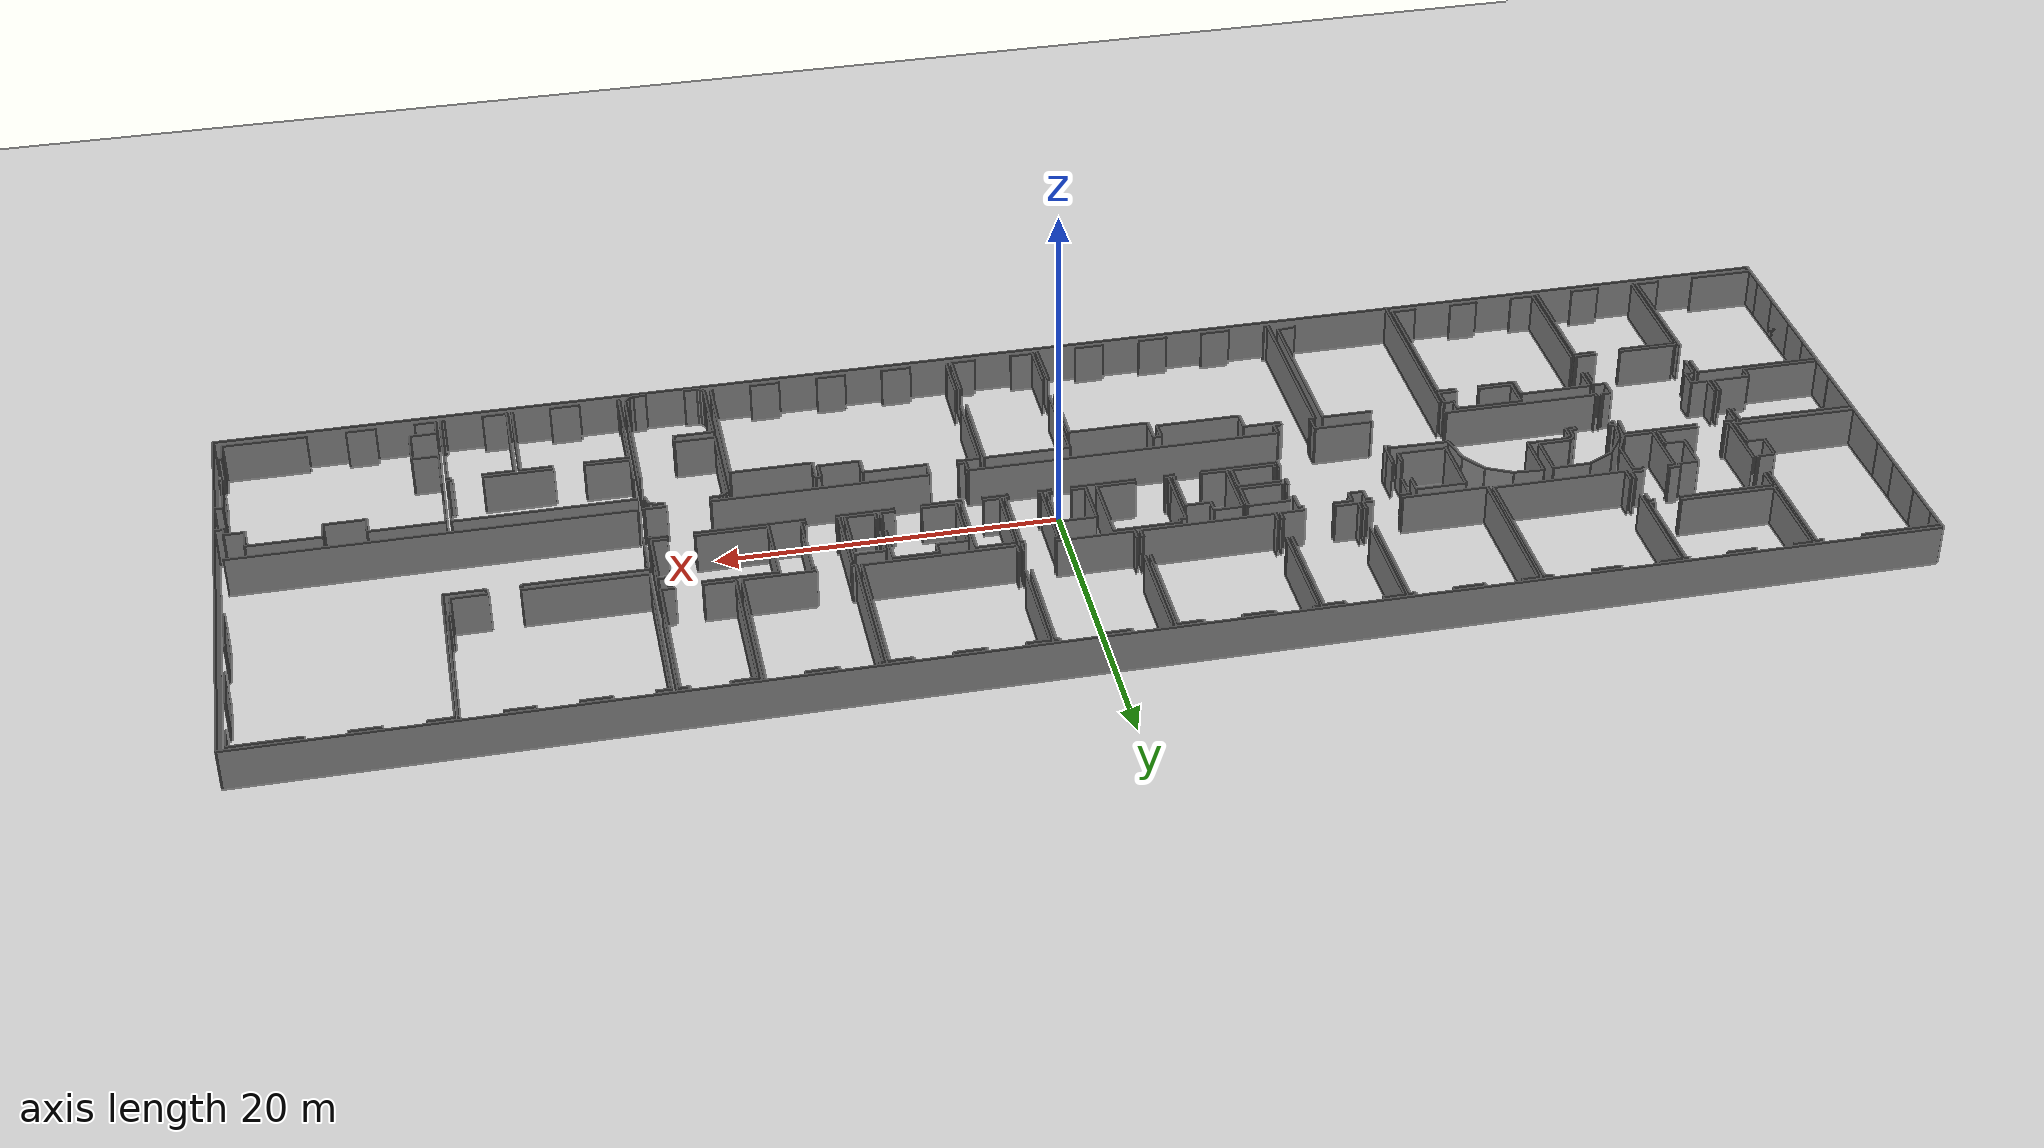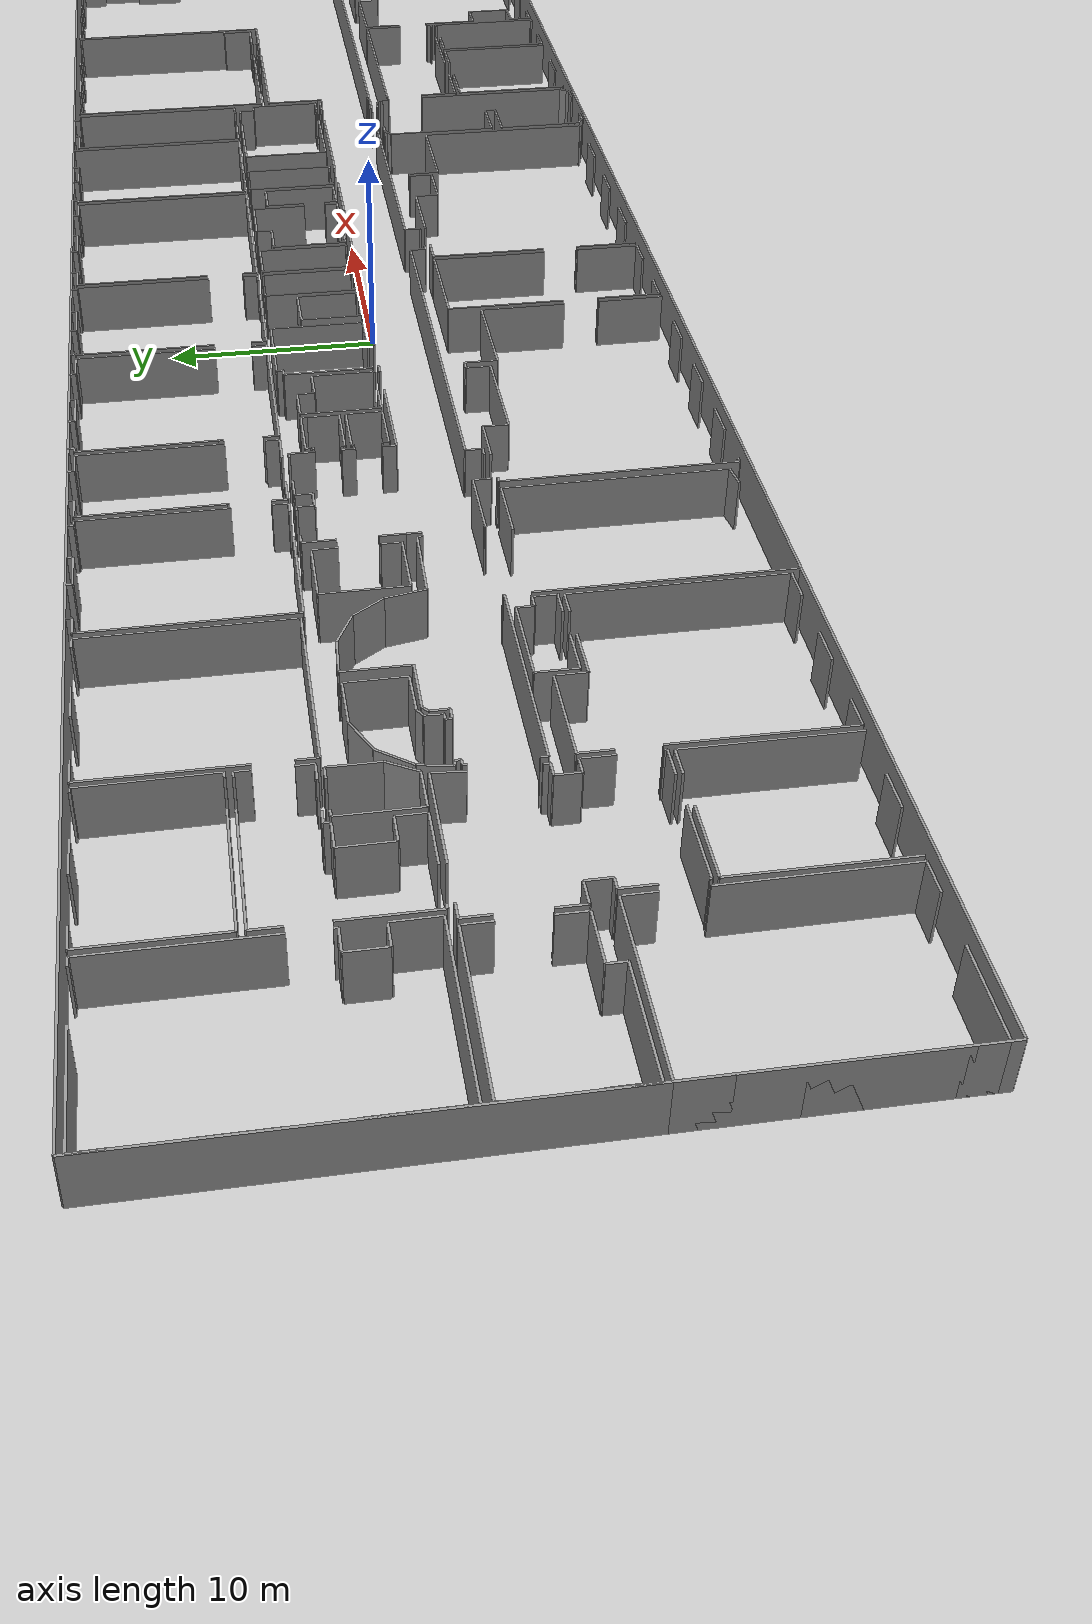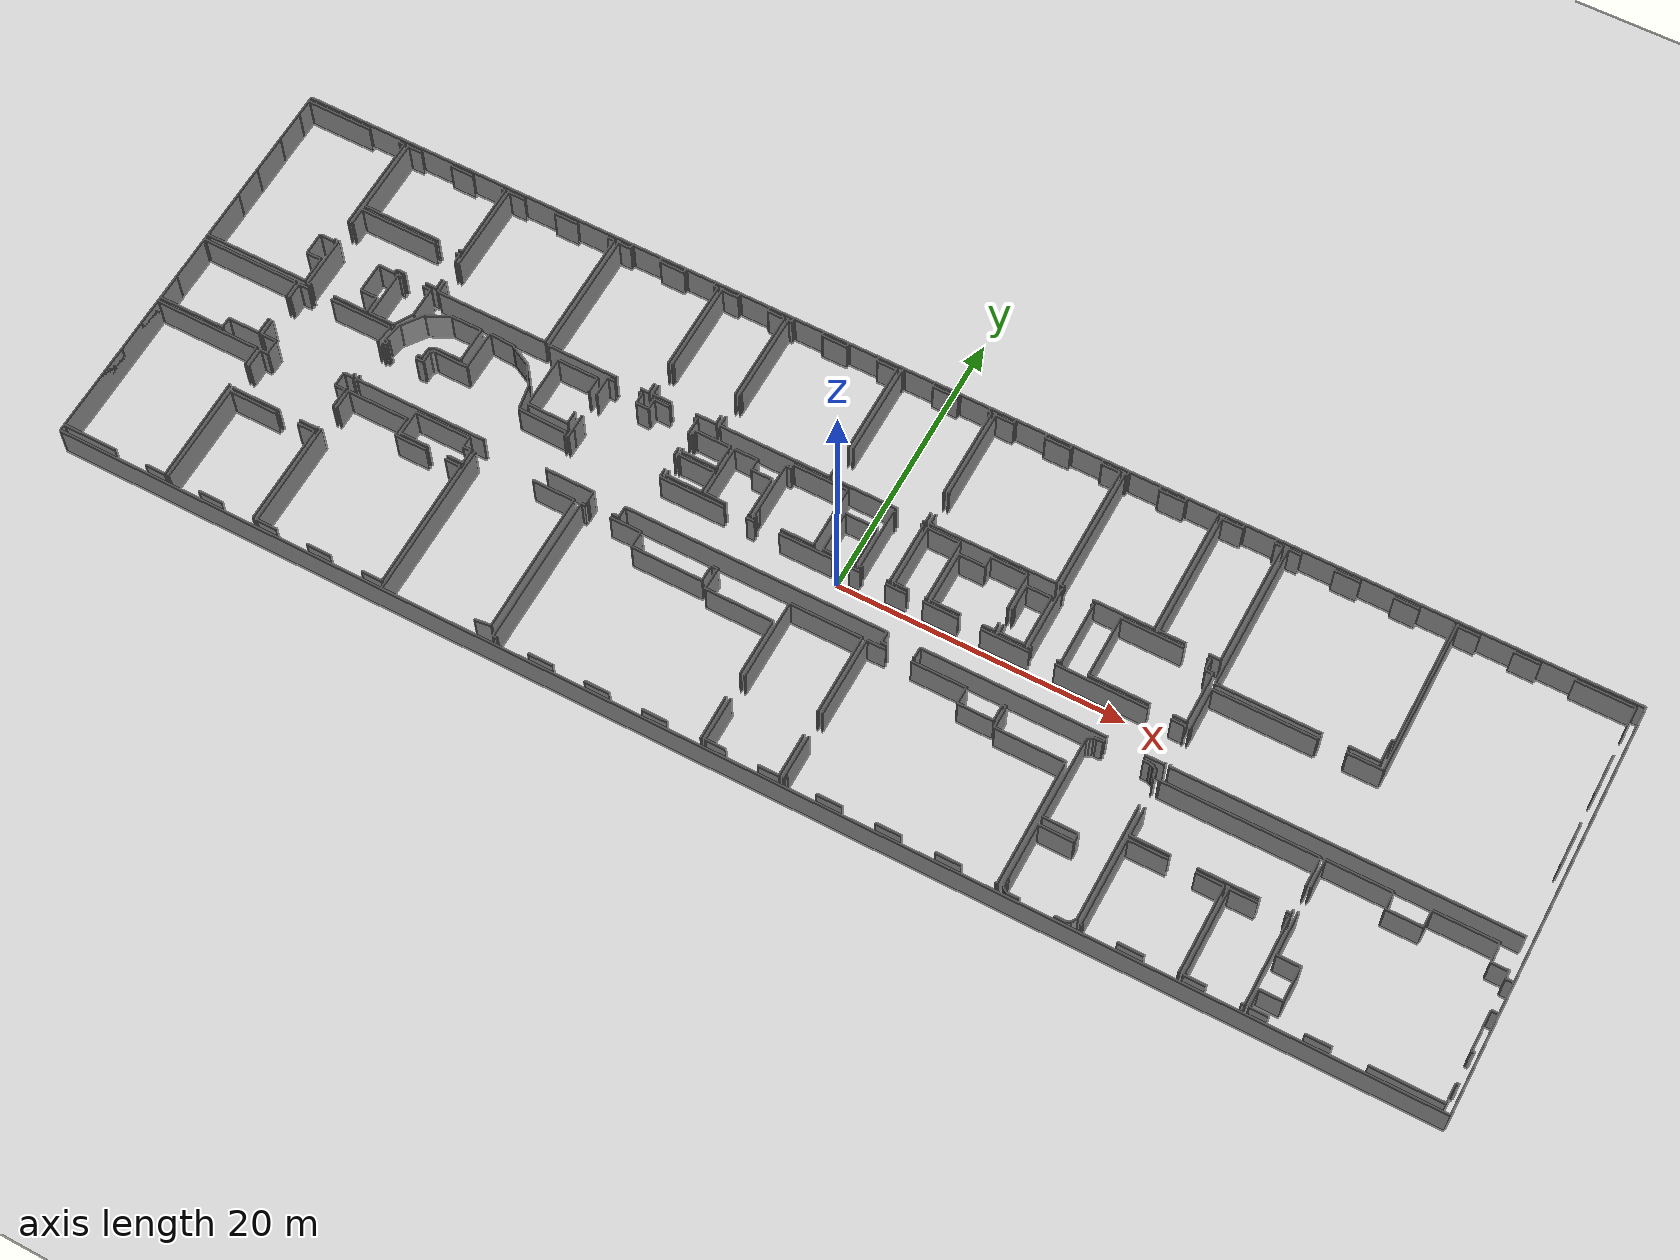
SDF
<sdf version="1.6">
  <world name="default">
    <light name="sun" type="directional">
      <cast_shadows>1</cast_shadows>
      <pose frame="">0 0 10 0 -0 0</pose>
      <diffuse>0.8 0.8 0.8 1</diffuse>
      <specular>0.1 0.1 0.1 1</specular>
      <attenuation>
        <range>1000</range>
        <constant>0.9</constant>
        <linear>0.01</linear>
        <quadratic>0.001</quadratic>
      </attenuation>
      <direction>-0.5 0.5 -1</direction>
    </light>
    <model name="ground_plane">
      <static>1</static>
      <link name="link">
        <collision name="collision">
          <geometry>
            <plane>
              <normal>0 0 1</normal>
              <size>100 100</size>
            </plane>
          </geometry>
          <surface>
            <friction>
              <ode>
                <mu>100</mu>
                <mu2>50</mu2>
              </ode>
              <torsional>
                <ode />
              </torsional>
            </friction>
            <contact>
              <ode />
            </contact>
            <bounce />
          </surface>
          <max_contacts>10</max_contacts>
        </collision>
        <visual name="visual">
          <cast_shadows>0</cast_shadows>
          <geometry>
            <plane>
              <normal>0 0 1</normal>
              <size>100 100</size>
            </plane>
          </geometry>
          <material>
            <script>
              <uri>file://media/materials/scripts/gazebo.material</uri>
              <name>Gazebo/Grey</name>
            </script>
          </material>
        </visual>
        <self_collide>0</self_collide>
        <kinematic>0</kinematic>
        <gravity>1</gravity>
      </link>
    </model>
    <gravity>0 0 -9.8</gravity>
    <magnetic_field>6e-06 2.3e-05 -4.2e-05</magnetic_field>
    <atmosphere type="adiabatic" />
    <physics default="0" name="default_physics" type="ode">
      <max_step_size>0.001</max_step_size>
      <real_time_factor>1</real_time_factor>
      <real_time_update_rate>1000</real_time_update_rate>
    </physics>
    <scene>
      <ambient>0.4 0.4 0.4 1</ambient>
      <background>0.7 0.7 0.7 1</background>
      <shadows>1</shadows>
    </scene>
    <spherical_coordinates>
      <surface_model>EARTH_WGS84</surface_model>
      <latitude_deg>0</latitude_deg>
      <longitude_deg>0</longitude_deg>
      <elevation>0</elevation>
      <heading_deg>0</heading_deg>
    </spherical_coordinates>
  <model name="0510032268_A_40_1_102">
		<static>1</static>
		<link name="Wall_0">
			<collision name="Wall_0_Collision">
				<geometry>
					<box>
						<size>7.50722080099 0.1 2.5</size>
					</box>
				</geometry>
				<pose frame="">3.75361040049 0 1.25 0 0 0</pose>
			</collision>
			<visual name="Wall_0_Visual">
				<pose frame="">3.75361040049 0 1.25 0 0 0</pose>
				<geometry>
					<box>
						<size>7.50722080099 0.1 2.5</size>
					</box>
				</geometry>
				<material>
					<script>
						<uri>file://media/materials/scripts/gazebo.material</uri>
						<name>Gazebo/Grey</name>
					</script>
					<ambient>1 1 1 1</ambient>
				</material>
			</visual>
			<pose frame="">7.51686969549 -12.5049672763 0 0 0 3.14159265359</pose>
		</link>
		<link name="Wall_1">
			<collision name="Wall_1_Collision">
				<geometry>
					<box>
						<size>3.57123359847 0.1 2.5</size>
					</box>
				</geometry>
				<pose frame="">1.78561679923 0 1.25 0 0 0</pose>
			</collision>
			<visual name="Wall_1_Visual">
				<pose frame="">1.78561679923 0 1.25 0 0 0</pose>
				<geometry>
					<box>
						<size>3.57123359847 0.1 2.5</size>
					</box>
				</geometry>
				<material>
					<script>
						<uri>file://media/materials/scripts/gazebo.material</uri>
						<name>Gazebo/Grey</name>
					</script>
					<ambient>1 1 1 1</ambient>
				</material>
			</visual>
			<pose frame="">0.0096488945033 -12.5049672763 0 0 0 1.57079632679</pose>
		</link>
		<link name="Wall_2">
			<collision name="Wall_2_Collision">
				<geometry>
					<box>
						<size>2.80478128114 0.1 2.5</size>
					</box>
				</geometry>
				<pose frame="">1.40239064057 0 1.25 0 0 0</pose>
			</collision>
			<visual name="Wall_2_Visual">
				<pose frame="">1.40239064057 0 1.25 0 0 0</pose>
				<geometry>
					<box>
						<size>2.80478128114 0.1 2.5</size>
					</box>
				</geometry>
				<material>
					<script>
						<uri>file://media/materials/scripts/gazebo.material</uri>
						<name>Gazebo/Grey</name>
					</script>
					<ambient>1 1 1 1</ambient>
				</material>
			</visual>
			<pose frame="">0.0096488945033 -6.70318857876 0 0 0 1.57079632679</pose>
		</link>
		<link name="Wall_3">
			<collision name="Wall_3_Collision">
				<geometry>
					<box>
						<size>1.26959138201 0.1 2.5</size>
					</box>
				</geometry>
				<pose frame="">0.634795691007 0 1.25 0 0 0</pose>
			</collision>
			<visual name="Wall_3_Visual">
				<pose frame="">0.634795691007 0 1.25 0 0 0</pose>
				<geometry>
					<box>
						<size>1.26959138201 0.1 2.5</size>
					</box>
				</geometry>
				<material>
					<script>
						<uri>file://media/materials/scripts/gazebo.material</uri>
						<name>Gazebo/Grey</name>
					</script>
					<ambient>1 1 1 1</ambient>
				</material>
			</visual>
			<pose frame="">0.0096488945033 -1.57734033301 0 0 0 1.57079632679</pose>
		</link>
		<link name="Wall_4">
			<collision name="Wall_4_Collision">
				<geometry>
					<box>
						<size>4.75195358374 0.1 2.5</size>
					</box>
				</geometry>
				<pose frame="">2.37597679187 0 1.25 0 0 0</pose>
			</collision>
			<visual name="Wall_4_Visual">
				<pose frame="">2.37597679187 0 1.25 0 0 0</pose>
				<geometry>
					<box>
						<size>4.75195358374 0.1 2.5</size>
					</box>
				</geometry>
				<material>
					<script>
						<uri>file://media/materials/scripts/gazebo.material</uri>
						<name>Gazebo/Grey</name>
					</script>
					<ambient>1 1 1 1</ambient>
				</material>
			</visual>
			<pose frame="">0.0096488945033 -0.307748951 0 0 0 0.0</pose>
		</link>
		<link name="Wall_5">
			<collision name="Wall_5_Collision">
				<geometry>
					<box>
						<size>0.412871117431 0.1 2.5</size>
					</box>
				</geometry>
				<pose frame="">0.206435558715 0 1.25 0 0 0</pose>
			</collision>
			<visual name="Wall_5_Visual">
				<pose frame="">0.206435558715 0 1.25 0 0 0</pose>
				<geometry>
					<box>
						<size>0.412871117431 0.1 2.5</size>
					</box>
				</geometry>
				<material>
					<script>
						<uri>file://media/materials/scripts/gazebo.material</uri>
						<name>Gazebo/Grey</name>
					</script>
					<ambient>1 1 1 1</ambient>
				</material>
			</visual>
			<pose frame="">7.07517885369 -0.307748951 0 0 0 0.0</pose>
		</link>
		<link name="Wall_6">
			<collision name="Wall_6_Collision">
				<geometry>
					<box>
						<size>6.98440306987 0.1 2.5</size>
					</box>
				</geometry>
				<pose frame="">3.49220153494 0 1.25 0 0 0</pose>
			</collision>
			<visual name="Wall_6_Visual">
				<pose frame="">3.49220153494 0 1.25 0 0 0</pose>
				<geometry>
					<box>
						<size>6.98440306987 0.1 2.5</size>
					</box>
				</geometry>
				<material>
					<script>
						<uri>file://media/materials/scripts/gazebo.material</uri>
						<name>Gazebo/Grey</name>
					</script>
					<ambient>1 1 1 1</ambient>
				</material>
			</visual>
			<pose frame="">7.48804997112 -0.307748951 0 0 0 -1.57079632679</pose>
		</link>
		<link name="Wall_7">
			<collision name="Wall_7_Collision">
				<geometry>
					<box>
						<size>0.170379163466 0.1 2.5</size>
					</box>
				</geometry>
				<pose frame="">0.0851895817331 0 1.25 0 0 0</pose>
			</collision>
			<visual name="Wall_7_Visual">
				<pose frame="">0.0851895817331 0 1.25 0 0 0</pose>
				<geometry>
					<box>
						<size>0.170379163466 0.1 2.5</size>
					</box>
				</geometry>
				<material>
					<script>
						<uri>file://media/materials/scripts/gazebo.material</uri>
						<name>Gazebo/Grey</name>
					</script>
					<ambient>1 1 1 1</ambient>
				</material>
			</visual>
			<pose frame="">7.48804997112 -8.84156134348 0 0 0 -1.57079632679</pose>
		</link>
		<link name="Wall_8">
			<collision name="Wall_8_Collision">
				<geometry>
					<box>
						<size>1.0458893805 0.1 2.5</size>
					</box>
				</geometry>
				<pose frame="">0.522944690251 0 1.25 0 0 0</pose>
			</collision>
			<visual name="Wall_8_Visual">
				<pose frame="">0.522944690251 0 1.25 0 0 0</pose>
				<geometry>
					<box>
						<size>1.0458893805 0.1 2.5</size>
					</box>
				</geometry>
				<material>
					<script>
						<uri>file://media/materials/scripts/gazebo.material</uri>
						<name>Gazebo/Grey</name>
					</script>
					<ambient>1 1 1 1</ambient>
				</material>
			</visual>
			<pose frame="">7.48804997112 -9.01194050695 0 0 0 3.14159265359</pose>
		</link>
		<link name="Wall_9">
			<collision name="Wall_9_Collision">
				<geometry>
					<box>
						<size>1.61022274981 0.1 2.5</size>
					</box>
				</geometry>
				<pose frame="">0.805111374904 0 1.25 0 0 0</pose>
			</collision>
			<visual name="Wall_9_Visual">
				<pose frame="">0.805111374904 0 1.25 0 0 0</pose>
				<geometry>
					<box>
						<size>1.61022274981 0.1 2.5</size>
					</box>
				</geometry>
				<material>
					<script>
						<uri>file://media/materials/scripts/gazebo.material</uri>
						<name>Gazebo/Grey</name>
					</script>
					<ambient>1 1 1 1</ambient>
				</material>
			</visual>
			<pose frame="">6.44216059061 -9.01194050695 0 0 0 -1.57079632679</pose>
		</link>
		<link name="Wall_10">
			<collision name="Wall_10_Collision">
				<geometry>
					<box>
						<size>1.05744266208 0.1 2.5</size>
					</box>
				</geometry>
				<pose frame="">0.52872133104 0 1.25 0 0 0</pose>
			</collision>
			<visual name="Wall_10_Visual">
				<pose frame="">0.52872133104 0 1.25 0 0 0</pose>
				<geometry>
					<box>
						<size>1.05744266208 0.1 2.5</size>
					</box>
				</geometry>
				<material>
					<script>
						<uri>file://media/materials/scripts/gazebo.material</uri>
						<name>Gazebo/Grey</name>
					</script>
					<ambient>1 1 1 1</ambient>
				</material>
			</visual>
			<pose frame="">6.44216059061 -10.6221632568 0 0 0 0.0</pose>
		</link>
		<link name="Wall_11">
			<collision name="Wall_11_Collision">
				<geometry>
					<box>
						<size>1.88288318968 0.1 2.5</size>
					</box>
				</geometry>
				<pose frame="">0.941441594842 0 1.25 0 0 0</pose>
			</collision>
			<visual name="Wall_11_Visual">
				<pose frame="">0.941441594842 0 1.25 0 0 0</pose>
				<geometry>
					<box>
						<size>1.88288318968 0.1 2.5</size>
					</box>
				</geometry>
				<material>
					<script>
						<uri>file://media/materials/scripts/gazebo.material</uri>
						<name>Gazebo/Grey</name>
					</script>
					<ambient>1 1 1 1</ambient>
				</material>
			</visual>
			<pose frame="">7.49960325269 -10.6221632568 0 0 0 -1.56162598373</pose>
		</link>
		<link name="Wall_12">
			<collision name="Wall_12_Collision">
				<geometry>
					<box>
						<size>0.304701931683 0.1 2.5</size>
					</box>
				</geometry>
				<pose frame="">0.152350965842 0 1.25 0 0 0</pose>
			</collision>
			<visual name="Wall_12_Visual">
				<pose frame="">0.152350965842 0 1.25 0 0 0</pose>
				<geometry>
					<box>
						<size>0.304701931683 0.1 2.5</size>
					</box>
				</geometry>
				<material>
					<script>
						<uri>file://media/materials/scripts/gazebo.material</uri>
						<name>Gazebo/Grey</name>
					</script>
					<ambient>1 1 1 1</ambient>
				</material>
			</visual>
			<pose frame="">15.3115259854 -5.71620823838 0 0 0 3.14159265359</pose>
		</link>
		<link name="Wall_13">
			<collision name="Wall_13_Collision">
				<geometry>
					<box>
						<size>5.64752334461 0.1 2.5</size>
					</box>
				</geometry>
				<pose frame="">2.82376167231 0 1.25 0 0 0</pose>
			</collision>
			<visual name="Wall_13_Visual">
				<pose frame="">2.82376167231 0 1.25 0 0 0</pose>
				<geometry>
					<box>
						<size>5.64752334461 0.1 2.5</size>
					</box>
				</geometry>
				<material>
					<script>
						<uri>file://media/materials/scripts/gazebo.material</uri>
						<name>Gazebo/Grey</name>
					</script>
					<ambient>1 1 1 1</ambient>
				</material>
			</visual>
			<pose frame="">13.4452266538 -5.71620823838 0 0 0 3.14159265359</pose>
		</link>
		<link name="Wall_14">
			<collision name="Wall_14_Collision">
				<geometry>
					<box>
						<size>5.42445613879 0.1 2.5</size>
					</box>
				</geometry>
				<pose frame="">2.7122280694 0 1.25 0 0 0</pose>
			</collision>
			<visual name="Wall_14_Visual">
				<pose frame="">2.7122280694 0 1.25 0 0 0</pose>
				<geometry>
					<box>
						<size>5.42445613879 0.1 2.5</size>
					</box>
				</geometry>
				<material>
					<script>
						<uri>file://media/materials/scripts/gazebo.material</uri>
						<name>Gazebo/Grey</name>
					</script>
					<ambient>1 1 1 1</ambient>
				</material>
			</visual>
			<pose frame="">7.79770330919 -5.71620823838 0 0 0 1.57079632679</pose>
		</link>
		<link name="Wall_15">
			<collision name="Wall_15_Collision">
				<geometry>
					<box>
						<size>1.01592702389 0.1 2.5</size>
					</box>
				</geometry>
				<pose frame="">0.507963511944 0 1.25 0 0 0</pose>
			</collision>
			<visual name="Wall_15_Visual">
				<pose frame="">0.507963511944 0 1.25 0 0 0</pose>
				<geometry>
					<box>
						<size>1.01592702389 0.1 2.5</size>
					</box>
				</geometry>
				<material>
					<script>
						<uri>file://media/materials/scripts/gazebo.material</uri>
						<name>Gazebo/Grey</name>
					</script>
					<ambient>1 1 1 1</ambient>
				</material>
			</visual>
			<pose frame="">7.79770330919 -0.291752099587 0 0 0 0.0</pose>
		</link>
		<link name="Wall_16">
			<collision name="Wall_16_Collision">
				<geometry>
					<box>
						<size>1.69858631 0.1 2.5</size>
					</box>
				</geometry>
				<pose frame="">0.849293154998 0 1.25 0 0 0</pose>
			</collision>
			<visual name="Wall_16_Visual">
				<pose frame="">0.849293154998 0 1.25 0 0 0</pose>
				<geometry>
					<box>
						<size>1.69858631 0.1 2.5</size>
					</box>
				</geometry>
				<material>
					<script>
						<uri>file://media/materials/scripts/gazebo.material</uri>
						<name>Gazebo/Grey</name>
					</script>
					<ambient>1 1 1 1</ambient>
				</material>
			</visual>
			<pose frame="">11.0856910703 -0.291752099587 0 0 0 0.0</pose>
		</link>
		<link name="Wall_17">
			<collision name="Wall_17_Collision">
				<geometry>
					<box>
						<size>0.248205115184 0.1 2.5</size>
					</box>
				</geometry>
				<pose frame="">0.124102557592 0 1.25 0 0 0</pose>
			</collision>
			<visual name="Wall_17_Visual">
				<pose frame="">0.124102557592 0 1.25 0 0 0</pose>
				<geometry>
					<box>
						<size>0.248205115184 0.1 2.5</size>
					</box>
				</geometry>
				<material>
					<script>
						<uri>file://media/materials/scripts/gazebo.material</uri>
						<name>Gazebo/Grey</name>
					</script>
					<ambient>1 1 1 1</ambient>
				</material>
			</visual>
			<pose frame="">15.0234557008 -0.291752099587 0 0 0 0.0</pose>
		</link>
		<link name="Wall_18">
			<collision name="Wall_18_Collision">
				<geometry>
					<box>
						<size>5.42460262447 0.1 2.5</size>
					</box>
				</geometry>
				<pose frame="">2.71230131223 0 1.25 0 0 0</pose>
			</collision>
			<visual name="Wall_18_Visual">
				<pose frame="">2.71230131223 0 1.25 0 0 0</pose>
				<geometry>
					<box>
						<size>5.42460262447 0.1 2.5</size>
					</box>
				</geometry>
				<material>
					<script>
						<uri>file://media/materials/scripts/gazebo.material</uri>
						<name>Gazebo/Grey</name>
					</script>
					<ambient>1 1 1 1</ambient>
				</material>
			</visual>
			<pose frame="">15.271660816 -0.291752099587 0 0 0 -1.56344730402</pose>
		</link>
		<link name="Wall_19">
			<collision name="Wall_19_Collision">
				<geometry>
					<box>
						<size>8.01759653655 0.1 2.5</size>
					</box>
				</geometry>
				<pose frame="">4.00879826828 0 1.25 0 0 0</pose>
			</collision>
			<visual name="Wall_19_Visual">
				<pose frame="">4.00879826828 0 1.25 0 0 0</pose>
				<geometry>
					<box>
						<size>8.01759653655 0.1 2.5</size>
					</box>
				</geometry>
				<material>
					<script>
						<uri>file://media/materials/scripts/gazebo.material</uri>
						<name>Gazebo/Grey</name>
					</script>
					<ambient>1 1 1 1</ambient>
				</material>
			</visual>
			<pose frame="">23.5752962909 -9.15299210949 0 0 0 3.14159265359</pose>
		</link>
		<link name="Wall_20">
			<collision name="Wall_20_Collision">
				<geometry>
					<box>
						<size>0.89645847484 0.1 2.5</size>
					</box>
				</geometry>
				<pose frame="">0.44822923742 0 1.25 0 0 0</pose>
			</collision>
			<visual name="Wall_20_Visual">
				<pose frame="">0.44822923742 0 1.25 0 0 0</pose>
				<geometry>
					<box>
						<size>0.89645847484 0.1 2.5</size>
					</box>
				</geometry>
				<material>
					<script>
						<uri>file://media/materials/scripts/gazebo.material</uri>
						<name>Gazebo/Grey</name>
					</script>
					<ambient>1 1 1 1</ambient>
				</material>
			</visual>
			<pose frame="">15.5576997543 -9.15299210949 0 0 0 1.57079632679</pose>
		</link>
		<link name="Wall_21">
			<collision name="Wall_21_Collision">
				<geometry>
					<box>
						<size>6.41892706832 0.1 2.5</size>
					</box>
				</geometry>
				<pose frame="">3.20946353416 0 1.25 0 0 0</pose>
			</collision>
			<visual name="Wall_21_Visual">
				<pose frame="">3.20946353416 0 1.25 0 0 0</pose>
				<geometry>
					<box>
						<size>6.41892706832 0.1 2.5</size>
					</box>
				</geometry>
				<material>
					<script>
						<uri>file://media/materials/scripts/gazebo.material</uri>
						<name>Gazebo/Grey</name>
					</script>
					<ambient>1 1 1 1</ambient>
				</material>
			</visual>
			<pose frame="">15.5576997543 -6.69493623477 0 0 0 1.57079632679</pose>
		</link>
		<link name="Wall_22">
			<collision name="Wall_22_Collision">
				<geometry>
					<box>
						<size>1.1857983508 0.1 2.5</size>
					</box>
				</geometry>
				<pose frame="">0.5928991754 0 1.25 0 0 0</pose>
			</collision>
			<visual name="Wall_22_Visual">
				<pose frame="">0.5928991754 0 1.25 0 0 0</pose>
				<geometry>
					<box>
						<size>1.1857983508 0.1 2.5</size>
					</box>
				</geometry>
				<material>
					<script>
						<uri>file://media/materials/scripts/gazebo.material</uri>
						<name>Gazebo/Grey</name>
					</script>
					<ambient>1 1 1 1</ambient>
				</material>
			</visual>
			<pose frame="">15.5576997543 -0.27600916645 0 0 0 0.0</pose>
		</link>
		<link name="Wall_23">
			<collision name="Wall_23_Collision">
				<geometry>
					<box>
						<size>1.72956433972 0.1 2.5</size>
					</box>
				</geometry>
				<pose frame="">0.864782169859 0 1.25 0 0 0</pose>
			</collision>
			<visual name="Wall_23_Visual">
				<pose frame="">0.864782169859 0 1.25 0 0 0</pose>
				<geometry>
					<box>
						<size>1.72956433972 0.1 2.5</size>
					</box>
				</geometry>
				<material>
					<script>
						<uri>file://media/materials/scripts/gazebo.material</uri>
						<name>Gazebo/Grey</name>
					</script>
					<ambient>1 1 1 1</ambient>
				</material>
			</visual>
			<pose frame="">19.0285086745 -0.27600916645 0 0 0 0.0</pose>
		</link>
		<link name="Wall_24">
			<collision name="Wall_24_Collision">
				<geometry>
					<box>
						<size>0.523833404219 0.1 2.5</size>
					</box>
				</geometry>
				<pose frame="">0.261916702109 0 1.25 0 0 0</pose>
			</collision>
			<visual name="Wall_24_Visual">
				<pose frame="">0.261916702109 0 1.25 0 0 0</pose>
				<geometry>
					<box>
						<size>0.523833404219 0.1 2.5</size>
					</box>
				</geometry>
				<material>
					<script>
						<uri>file://media/materials/scripts/gazebo.material</uri>
						<name>Gazebo/Grey</name>
					</script>
					<ambient>1 1 1 1</ambient>
				</material>
			</visual>
			<pose frame="">23.0367356266 -0.27600916645 0 0 0 0.0</pose>
		</link>
		<link name="Wall_25">
			<collision name="Wall_25_Collision">
				<geometry>
					<box>
						<size>8.87699515958 0.1 2.5</size>
					</box>
				</geometry>
				<pose frame="">4.43849757979 0 1.25 0 0 0</pose>
			</collision>
			<visual name="Wall_25_Visual">
				<pose frame="">4.43849757979 0 1.25 0 0 0</pose>
				<geometry>
					<box>
						<size>8.87699515958 0.1 2.5</size>
					</box>
				</geometry>
				<material>
					<script>
						<uri>file://media/materials/scripts/gazebo.material</uri>
						<name>Gazebo/Grey</name>
					</script>
					<ambient>1 1 1 1</ambient>
				</material>
			</visual>
			<pose frame="">23.5605690309 -0.27600916645 0 0 0 -1.56913728942</pose>
		</link>
		<link name="Wall_26">
			<collision name="Wall_26_Collision">
				<geometry>
					<box>
						<size>2.50591946982 0.1 2.5</size>
					</box>
				</geometry>
				<pose frame="">1.25295973491 0 1.25 0 0 0</pose>
			</collision>
			<visual name="Wall_26_Visual">
				<pose frame="">1.25295973491 0 1.25 0 0 0</pose>
				<geometry>
					<box>
						<size>2.50591946982 0.1 2.5</size>
					</box>
				</geometry>
				<material>
					<script>
						<uri>file://media/materials/scripts/gazebo.material</uri>
						<name>Gazebo/Grey</name>
					</script>
					<ambient>1 1 1 1</ambient>
				</material>
			</visual>
			<pose frame="">12.2808843974 -12.6414483498 0 0 0 3.14159265359</pose>
		</link>
		<link name="Wall_27">
			<collision name="Wall_27_Collision">
				<geometry>
					<box>
						<size>0.246935523802 0.1 2.5</size>
					</box>
				</geometry>
				<pose frame="">0.123467761901 0 1.25 0 0 0</pose>
			</collision>
			<visual name="Wall_27_Visual">
				<pose frame="">0.123467761901 0 1.25 0 0 0</pose>
				<geometry>
					<box>
						<size>0.246935523802 0.1 2.5</size>
					</box>
				</geometry>
				<material>
					<script>
						<uri>file://media/materials/scripts/gazebo.material</uri>
						<name>Gazebo/Grey</name>
					</script>
					<ambient>1 1 1 1</ambient>
				</material>
			</visual>
			<pose frame="">8.03194291917 -12.6414483498 0 0 0 3.14159265359</pose>
		</link>
		<link name="Wall_28">
			<collision name="Wall_28_Collision">
				<geometry>
					<box>
						<size>3.77690740235 0.1 2.5</size>
					</box>
				</geometry>
				<pose frame="">1.88845370118 0 1.25 0 0 0</pose>
			</collision>
			<visual name="Wall_28_Visual">
				<pose frame="">1.88845370118 0 1.25 0 0 0</pose>
				<geometry>
					<box>
						<size>3.77690740235 0.1 2.5</size>
					</box>
				</geometry>
				<material>
					<script>
						<uri>file://media/materials/scripts/gazebo.material</uri>
						<name>Gazebo/Grey</name>
					</script>
					<ambient>1 1 1 1</ambient>
				</material>
			</visual>
			<pose frame="">7.78500739537 -12.6414483498 0 0 0 1.57079632679</pose>
		</link>
		<link name="Wall_29">
			<collision name="Wall_29_Collision">
				<geometry>
					<box>
						<size>1.22680615244 0.1 2.5</size>
					</box>
				</geometry>
				<pose frame="">0.61340307622 0 1.25 0 0 0</pose>
			</collision>
			<visual name="Wall_29_Visual">
				<pose frame="">0.61340307622 0 1.25 0 0 0</pose>
				<geometry>
					<box>
						<size>1.22680615244 0.1 2.5</size>
					</box>
				</geometry>
				<material>
					<script>
						<uri>file://media/materials/scripts/gazebo.material</uri>
						<name>Gazebo/Grey</name>
					</script>
					<ambient>1 1 1 1</ambient>
				</material>
			</visual>
			<pose frame="">7.78500739537 -7.26041223632 0 0 0 1.57079632679</pose>
		</link>
		<link name="Wall_30">
			<collision name="Wall_30_Collision">
				<geometry>
					<box>
						<size>5.6089277666 0.1 2.5</size>
					</box>
				</geometry>
				<pose frame="">2.8044638833 0 1.25 0 0 0</pose>
			</collision>
			<visual name="Wall_30_Visual">
				<pose frame="">2.8044638833 0 1.25 0 0 0</pose>
				<geometry>
					<box>
						<size>5.6089277666 0.1 2.5</size>
					</box>
				</geometry>
				<material>
					<script>
						<uri>file://media/materials/scripts/gazebo.material</uri>
						<name>Gazebo/Grey</name>
					</script>
					<ambient>1 1 1 1</ambient>
				</material>
			</visual>
			<pose frame="">7.78500739537 -6.03360608388 0 0 0 0.0</pose>
		</link>
		<link name="Wall_31">
			<collision name="Wall_31_Collision">
				<geometry>
					<box>
						<size>0.31549345843 0.1 2.5</size>
					</box>
				</geometry>
				<pose frame="">0.157746729215 0 1.25 0 0 0</pose>
			</collision>
			<visual name="Wall_31_Visual">
				<pose frame="">0.157746729215 0 1.25 0 0 0</pose>
				<geometry>
					<box>
						<size>0.31549345843 0.1 2.5</size>
					</box>
				</geometry>
				<material>
					<script>
						<uri>file://media/materials/scripts/gazebo.material</uri>
						<name>Gazebo/Grey</name>
					</script>
					<ambient>1 1 1 1</ambient>
				</material>
			</visual>
			<pose frame="">14.9661971295 -6.03360608388 0 0 0 0.0</pose>
		</link>
		<link name="Wall_32">
			<collision name="Wall_32_Collision">
				<geometry>
					<box>
						<size>0.651300378973 0.1 2.5</size>
					</box>
				</geometry>
				<pose frame="">0.325650189487 0 1.25 0 0 0</pose>
			</collision>
			<visual name="Wall_32_Visual">
				<pose frame="">0.325650189487 0 1.25 0 0 0</pose>
				<geometry>
					<box>
						<size>0.651300378973 0.1 2.5</size>
					</box>
				</geometry>
				<material>
					<script>
						<uri>file://media/materials/scripts/gazebo.material</uri>
						<name>Gazebo/Grey</name>
					</script>
					<ambient>1 1 1 1</ambient>
				</material>
			</visual>
			<pose frame="">15.2816905879 -6.03360608388 0 0 0 -1.57079632679</pose>
		</link>
		<link name="Wall_33">
			<collision name="Wall_33_Collision">
				<geometry>
					<box>
						<size>0.729634167243 0.1 2.5</size>
					</box>
				</geometry>
				<pose frame="">0.364817083622 0 1.25 0 0 0</pose>
			</collision>
			<visual name="Wall_33_Visual">
				<pose frame="">0.364817083622 0 1.25 0 0 0</pose>
				<geometry>
					<box>
						<size>0.729634167243 0.1 2.5</size>
					</box>
				</geometry>
				<material>
					<script>
						<uri>file://media/materials/scripts/gazebo.material</uri>
						<name>Gazebo/Grey</name>
					</script>
					<ambient>1 1 1 1</ambient>
				</material>
			</visual>
			<pose frame="">15.2816905879 -8.23291923494 0 0 0 -1.57079632679</pose>
		</link>
		<link name="Wall_34">
			<collision name="Wall_34_Collision">
				<geometry>
					<box>
						<size>0.8145698307 0.1 2.5</size>
					</box>
				</geometry>
				<pose frame="">0.40728491535 0 1.25 0 0 0</pose>
			</collision>
			<visual name="Wall_34_Visual">
				<pose frame="">0.40728491535 0 1.25 0 0 0</pose>
				<geometry>
					<box>
						<size>0.8145698307 0.1 2.5</size>
					</box>
				</geometry>
				<material>
					<script>
						<uri>file://media/materials/scripts/gazebo.material</uri>
						<name>Gazebo/Grey</name>
					</script>
					<ambient>1 1 1 1</ambient>
				</material>
			</visual>
			<pose frame="">15.2816905879 -8.96255340219 0 0 0 3.14159265359</pose>
		</link>
		<link name="Wall_35">
			<collision name="Wall_35_Collision">
				<geometry>
					<box>
						<size>0.624258082536 0.1 2.5</size>
					</box>
				</geometry>
				<pose frame="">0.312129041268 0 1.25 0 0 0</pose>
			</collision>
			<visual name="Wall_35_Visual">
				<pose frame="">0.312129041268 0 1.25 0 0 0</pose>
				<geometry>
					<box>
						<size>0.624258082536 0.1 2.5</size>
					</box>
				</geometry>
				<material>
					<script>
						<uri>file://media/materials/scripts/gazebo.material</uri>
						<name>Gazebo/Grey</name>
					</script>
					<ambient>1 1 1 1</ambient>
				</material>
			</visual>
			<pose frame="">12.9076816627 -8.96255340219 0 0 0 3.14159265359</pose>
		</link>
		<link name="Wall_36">
			<collision name="Wall_36_Collision">
				<geometry>
					<box>
						<size>0.272200392304 0.1 2.5</size>
					</box>
				</geometry>
				<pose frame="">0.136100196152 0 1.25 0 0 0</pose>
			</collision>
			<visual name="Wall_36_Visual">
				<pose frame="">0.136100196152 0 1.25 0 0 0</pose>
				<geometry>
					<box>
						<size>0.272200392304 0.1 2.5</size>
					</box>
				</geometry>
				<material>
					<script>
						<uri>file://media/materials/scripts/gazebo.material</uri>
						<name>Gazebo/Grey</name>
					</script>
					<ambient>1 1 1 1</ambient>
				</material>
			</visual>
			<pose frame="">12.2834235801 -8.96255340219 0 0 0 -1.57079632679</pose>
		</link>
		<link name="Wall_37">
			<collision name="Wall_37_Collision">
				<geometry>
					<box>
						<size>1.20509613981 0.1 2.5</size>
					</box>
				</geometry>
				<pose frame="">0.602548069904 0 1.25 0 0 0</pose>
			</collision>
			<visual name="Wall_37_Visual">
				<pose frame="">0.602548069904 0 1.25 0 0 0</pose>
				<geometry>
					<box>
						<size>1.20509613981 0.1 2.5</size>
					</box>
				</geometry>
				<material>
					<script>
						<uri>file://media/materials/scripts/gazebo.material</uri>
						<name>Gazebo/Grey</name>
					</script>
					<ambient>1 1 1 1</ambient>
				</material>
			</visual>
			<pose frame="">12.2834235801 -9.23475379449 0 0 0 3.14159265359</pose>
		</link>
		<link name="Wall_38">
			<collision name="Wall_38_Collision">
				<geometry>
					<box>
						<size>2.18877554259 0.1 2.5</size>
					</box>
				</geometry>
				<pose frame="">1.0943877713 0 1.25 0 0 0</pose>
			</collision>
			<visual name="Wall_38_Visual">
				<pose frame="">1.0943877713 0 1.25 0 0 0</pose>
				<geometry>
					<box>
						<size>2.18877554259 0.1 2.5</size>
					</box>
				</geometry>
				<material>
					<script>
						<uri>file://media/materials/scripts/gazebo.material</uri>
						<name>Gazebo/Grey</name>
					</script>
					<ambient>1 1 1 1</ambient>
				</material>
			</visual>
			<pose frame="">11.0783274403 -9.23475379449 0 0 0 -1.57079632679</pose>
		</link>
		<link name="Wall_39">
			<collision name="Wall_39_Collision">
				<geometry>
					<box>
						<size>1.19646291841 0.1 2.5</size>
					</box>
				</geometry>
				<pose frame="">0.598231459205 0 1.25 0 0 0</pose>
			</collision>
			<visual name="Wall_39_Visual">
				<pose frame="">0.598231459205 0 1.25 0 0 0</pose>
				<geometry>
					<box>
						<size>1.19646291841 0.1 2.5</size>
					</box>
				</geometry>
				<material>
					<script>
						<uri>file://media/materials/scripts/gazebo.material</uri>
						<name>Gazebo/Grey</name>
					</script>
					<ambient>1 1 1 1</ambient>
				</material>
			</visual>
			<pose frame="">11.0783274403 -11.4235293371 0 0 0 0.0</pose>
		</link>
		<link name="Wall_40">
			<collision name="Wall_40_Collision">
				<geometry>
					<box>
						<size>1.21793425888 0.1 2.5</size>
					</box>
				</geometry>
				<pose frame="">0.608967129442 0 1.25 0 0 0</pose>
			</collision>
			<visual name="Wall_40_Visual">
				<pose frame="">0.608967129442 0 1.25 0 0 0</pose>
				<geometry>
					<box>
						<size>1.21793425888 0.1 2.5</size>
					</box>
				</geometry>
				<material>
					<script>
						<uri>file://media/materials/scripts/gazebo.material</uri>
						<name>Gazebo/Grey</name>
					</script>
					<ambient>1 1 1 1</ambient>
				</material>
			</visual>
			<pose frame="">12.2747903587 -11.4235293371 0 0 0 -1.56579272006</pose>
		</link>
		<link name="Wall_41">
			<collision name="Wall_41_Collision">
				<geometry>
					<box>
						<size>1.77971319931 0.1 2.5</size>
					</box>
				</geometry>
				<pose frame="">0.889856599653 0 1.25 0 0 0</pose>
			</collision>
			<visual name="Wall_41_Visual">
				<pose frame="">0.889856599653 0 1.25 0 0 0</pose>
				<geometry>
					<box>
						<size>1.77971319931 0.1 2.5</size>
					</box>
				</geometry>
				<material>
					<script>
						<uri>file://media/materials/scripts/gazebo.material</uri>
						<name>Gazebo/Grey</name>
					</script>
					<ambient>1 1 1 1</ambient>
				</material>
			</visual>
			<pose frame="">14.3522227371 -12.6432257778 0 0 0 3.14159265359</pose>
		</link>
		<link name="Wall_42">
			<collision name="Wall_42_Collision">
				<geometry>
					<box>
						<size>3.38206448255 0.1 2.5</size>
					</box>
				</geometry>
				<pose frame="">1.69103224127 0 1.25 0 0 0</pose>
			</collision>
			<visual name="Wall_42_Visual">
				<pose frame="">1.69103224127 0 1.25 0 0 0</pose>
				<geometry>
					<box>
						<size>3.38206448255 0.1 2.5</size>
					</box>
				</geometry>
				<material>
					<script>
						<uri>file://media/materials/scripts/gazebo.material</uri>
						<name>Gazebo/Grey</name>
					</script>
					<ambient>1 1 1 1</ambient>
				</material>
			</visual>
			<pose frame="">12.5725095378 -12.6432257778 0 0 0 1.57079632679</pose>
		</link>
		<link name="Wall_43">
			<collision name="Wall_43_Collision">
				<geometry>
					<box>
						<size>0.313589071357 0.1 2.5</size>
					</box>
				</geometry>
				<pose frame="">0.156794535679 0 1.25 0 0 0</pose>
			</collision>
			<visual name="Wall_43_Visual">
				<pose frame="">0.156794535679 0 1.25 0 0 0</pose>
				<geometry>
					<box>
						<size>0.313589071357 0.1 2.5</size>
					</box>
				</geometry>
				<material>
					<script>
						<uri>file://media/materials/scripts/gazebo.material</uri>
						<name>Gazebo/Grey</name>
					</script>
					<ambient>1 1 1 1</ambient>
				</material>
			</visual>
			<pose frame="">12.5725095378 -9.26116129524 0 0 0 0.0</pose>
		</link>
		<link name="Wall_44">
			<collision name="Wall_44_Collision">
				<geometry>
					<box>
						<size>0.592645257124 0.1 2.5</size>
					</box>
				</geometry>
				<pose frame="">0.296322628562 0 1.25 0 0 0</pose>
			</collision>
			<visual name="Wall_44_Visual">
				<pose frame="">0.296322628562 0 1.25 0 0 0</pose>
				<geometry>
					<box>
						<size>0.592645257124 0.1 2.5</size>
					</box>
				</geometry>
				<material>
					<script>
						<uri>file://media/materials/scripts/gazebo.material</uri>
						<name>Gazebo/Grey</name>
					</script>
					<ambient>1 1 1 1</ambient>
				</material>
			</visual>
			<pose frame="">14.4508699875 -9.26116129524 0 0 0 0.0</pose>
		</link>
		<link name="Wall_45">
			<collision name="Wall_45_Collision">
				<geometry>
					<box>
						<size>2.13684925507 0.1 2.5</size>
					</box>
				</geometry>
				<pose frame="">1.06842462753 0 1.25 0 0 0</pose>
			</collision>
			<visual name="Wall_45_Visual">
				<pose frame="">1.06842462753 0 1.25 0 0 0</pose>
				<geometry>
					<box>
						<size>2.13684925507 0.1 2.5</size>
					</box>
				</geometry>
				<material>
					<script>
						<uri>file://media/materials/scripts/gazebo.material</uri>
						<name>Gazebo/Grey</name>
					</script>
					<ambient>1 1 1 1</ambient>
				</material>
			</visual>
			<pose frame="">15.0435152446 -9.26116129524 0 0 0 -1.57079632679</pose>
		</link>
		<link name="Wall_46">
			<collision name="Wall_46_Collision">
				<geometry>
					<box>
						<size>1.42423533648 0.1 2.5</size>
					</box>
				</geometry>
				<pose frame="">0.71211766824 0 1.25 0 0 0</pose>
			</collision>
			<visual name="Wall_46_Visual">
				<pose frame="">0.71211766824 0 1.25 0 0 0</pose>
				<geometry>
					<box>
						<size>1.42423533648 0.1 2.5</size>
					</box>
				</geometry>
				<material>
					<script>
						<uri>file://media/materials/scripts/gazebo.material</uri>
						<name>Gazebo/Grey</name>
					</script>
					<ambient>1 1 1 1</ambient>
				</material>
			</visual>
			<pose frame="">15.0435152446 -11.3980105503 0 0 0 -2.07759179302</pose>
		</link>
		<link name="Wall_47">
			<collision name="Wall_47_Collision">
				<geometry>
					<box>
						<size>1.29396753655 0.1 2.5</size>
					</box>
				</geometry>
				<pose frame="">0.646983768274 0 1.25 0 0 0</pose>
			</collision>
			<visual name="Wall_47_Visual">
				<pose frame="">0.646983768274 0 1.25 0 0 0</pose>
				<geometry>
					<box>
						<size>1.29396753655 0.1 2.5</size>
					</box>
				</geometry>
				<material>
					<script>
						<uri>file://media/materials/scripts/gazebo.material</uri>
						<name>Gazebo/Grey</name>
					</script>
					<ambient>1 1 1 1</ambient>
				</material>
			</visual>
			<pose frame="">14.200506567 -21.5789908018 0 0 0 3.14159265359</pose>
		</link>
		<link name="Wall_48">
			<collision name="Wall_48_Collision">
				<geometry>
					<box>
						<size>3.49061454571 0.1 2.5</size>
					</box>
				</geometry>
				<pose frame="">1.74530727285 0 1.25 0 0 0</pose>
			</collision>
			<visual name="Wall_48_Visual">
				<pose frame="">1.74530727285 0 1.25 0 0 0</pose>
				<geometry>
					<box>
						<size>3.49061454571 0.1 2.5</size>
					</box>
				</geometry>
				<material>
					<script>
						<uri>file://media/materials/scripts/gazebo.material</uri>
						<name>Gazebo/Grey</name>
					</script>
					<ambient>1 1 1 1</ambient>
				</material>
			</visual>
			<pose frame="">11.3529400562 -21.5789908018 0 0 0 3.14159265359</pose>
		</link>
		<link name="Wall_49">
			<collision name="Wall_49_Collision">
				<geometry>
					<box>
						<size>0.0816347258635 0.1 2.5</size>
					</box>
				</geometry>
				<pose frame="">0.0408173629317 0 1.25 0 0 0</pose>
			</collision>
			<visual name="Wall_49_Visual">
				<pose frame="">0.0408173629317 0 1.25 0 0 0</pose>
				<geometry>
					<box>
						<size>0.0816347258635 0.1 2.5</size>
					</box>
				</geometry>
				<material>
					<script>
						<uri>file://media/materials/scripts/gazebo.material</uri>
						<name>Gazebo/Grey</name>
					</script>
					<ambient>1 1 1 1</ambient>
				</material>
			</visual>
			<pose frame="">7.86232551053 -21.5789908018 0 0 0 1.57079632679</pose>
		</link>
		<link name="Wall_50">
			<collision name="Wall_50_Collision">
				<geometry>
					<box>
						<size>1.40162888574 0.1 2.5</size>
					</box>
				</geometry>
				<pose frame="">0.700814442872 0 1.25 0 0 0</pose>
			</collision>
			<visual name="Wall_50_Visual">
				<pose frame="">0.700814442872 0 1.25 0 0 0</pose>
				<geometry>
					<box>
						<size>1.40162888574 0.1 2.5</size>
					</box>
				</geometry>
				<material>
					<script>
						<uri>file://media/materials/scripts/gazebo.material</uri>
						<name>Gazebo/Grey</name>
					</script>
					<ambient>1 1 1 1</ambient>
				</material>
			</visual>
			<pose frame="">7.86232551053 -19.7529375171 0 0 0 1.57079632679</pose>
		</link>
		<link name="Wall_51">
			<collision name="Wall_51_Collision">
				<geometry>
					<box>
						<size>0.508852225911 0.1 2.5</size>
					</box>
				</geometry>
				<pose frame="">0.254426112956 0 1.25 0 0 0</pose>
			</collision>
			<visual name="Wall_51_Visual">
				<pose frame="">0.254426112956 0 1.25 0 0 0</pose>
				<geometry>
					<box>
						<size>0.508852225911 0.1 2.5</size>
					</box>
				</geometry>
				<material>
					<script>
						<uri>file://media/materials/scripts/gazebo.material</uri>
						<name>Gazebo/Grey</name>
					</script>
					<ambient>1 1 1 1</ambient>
				</material>
			</visual>
			<pose frame="">7.86232551053 -18.3513086313 0 0 0 0.0</pose>
		</link>
		<link name="Wall_52">
			<collision name="Wall_52_Collision">
				<geometry>
					<box>
						<size>1.04639721706 0.1 2.5</size>
					</box>
				</geometry>
				<pose frame="">0.523198608528 0 1.25 0 0 0</pose>
			</collision>
			<visual name="Wall_52_Visual">
				<pose frame="">0.523198608528 0 1.25 0 0 0</pose>
				<geometry>
					<box>
						<size>1.04639721706 0.1 2.5</size>
					</box>
				</geometry>
				<material>
					<script>
						<uri>file://media/materials/scripts/gazebo.material</uri>
						<name>Gazebo/Grey</name>
					</script>
					<ambient>1 1 1 1</ambient>
				</material>
			</visual>
			<pose frame="">8.37117773645 -18.3513086313 0 0 0 1.57079632679</pose>
		</link>
		<link name="Wall_53">
			<collision name="Wall_53_Collision">
				<geometry>
					<box>
						<size>1.04639721706 0.1 2.5</size>
					</box>
				</geometry>
				<pose frame="">0.523198608528 0 1.25 0 0 0</pose>
			</collision>
			<visual name="Wall_53_Visual">
				<pose frame="">0.523198608528 0 1.25 0 0 0</pose>
				<geometry>
					<box>
						<size>1.04639721706 0.1 2.5</size>
					</box>
				</geometry>
				<material>
					<script>
						<uri>file://media/materials/scripts/gazebo.material</uri>
						<name>Gazebo/Grey</name>
					</script>
					<ambient>1 1 1 1</ambient>
				</material>
			</visual>
			<pose frame="">8.37117773645 -17.3049114143 0 0 0 3.14159265359</pose>
		</link>
		<link name="Wall_54">
			<collision name="Wall_54_Collision">
				<geometry>
					<box>
						<size>1.18084694441 0.1 2.5</size>
					</box>
				</geometry>
				<pose frame="">0.590423472205 0 1.25 0 0 0</pose>
			</collision>
			<visual name="Wall_54_Visual">
				<pose frame="">0.590423472205 0 1.25 0 0 0</pose>
				<geometry>
					<box>
						<size>1.18084694441 0.1 2.5</size>
					</box>
				</geometry>
				<material>
					<script>
						<uri>file://media/materials/scripts/gazebo.material</uri>
						<name>Gazebo/Grey</name>
					</script>
					<ambient>1 1 1 1</ambient>
				</material>
			</visual>
			<pose frame="">7.32478051939 -17.3049114143 0 0 0 1.57079632679</pose>
		</link>
		<link name="Wall_55">
			<collision name="Wall_55_Collision">
				<geometry>
					<box>
						<size>1.16561184783 0.1 2.5</size>
					</box>
				</geometry>
				<pose frame="">0.582805923913 0 1.25 0 0 0</pose>
			</collision>
			<visual name="Wall_55_Visual">
				<pose frame="">0.582805923913 0 1.25 0 0 0</pose>
				<geometry>
					<box>
						<size>1.16561184783 0.1 2.5</size>
					</box>
				</geometry>
				<material>
					<script>
						<uri>file://media/materials/scripts/gazebo.material</uri>
						<name>Gazebo/Grey</name>
					</script>
					<ambient>1 1 1 1</ambient>
				</material>
			</visual>
			<pose frame="">7.32478051939 -14.0878938114 0 0 0 1.57079632679</pose>
		</link>
		<link name="Wall_56">
			<collision name="Wall_56_Collision">
				<geometry>
					<box>
						<size>0.683040163523 0.1 2.5</size>
					</box>
				</geometry>
				<pose frame="">0.341520081762 0 1.25 0 0 0</pose>
			</collision>
			<visual name="Wall_56_Visual">
				<pose frame="">0.341520081762 0 1.25 0 0 0</pose>
				<geometry>
					<box>
						<size>0.683040163523 0.1 2.5</size>
					</box>
				</geometry>
				<material>
					<script>
						<uri>file://media/materials/scripts/gazebo.material</uri>
						<name>Gazebo/Grey</name>
					</script>
					<ambient>1 1 1 1</ambient>
				</material>
			</visual>
			<pose frame="">7.32478051939 -12.9222819636 0 0 0 0.0</pose>
		</link>
		<link name="Wall_57">
			<collision name="Wall_57_Collision">
				<geometry>
					<box>
						<size>4.46426417657 0.1 2.5</size>
					</box>
				</geometry>
				<pose frame="">2.23213208829 0 1.25 0 0 0</pose>
			</collision>
			<visual name="Wall_57_Visual">
				<pose frame="">2.23213208829 0 1.25 0 0 0</pose>
				<geometry>
					<box>
						<size>4.46426417657 0.1 2.5</size>
					</box>
				</geometry>
				<material>
					<script>
						<uri>file://media/materials/scripts/gazebo.material</uri>
						<name>Gazebo/Grey</name>
					</script>
					<ambient>1 1 1 1</ambient>
				</material>
			</visual>
			<pose frame="">9.77179094908 -12.9222819636 0 0 0 0.0</pose>
		</link>
		<link name="Wall_58">
			<collision name="Wall_58_Collision">
				<geometry>
					<box>
						<size>1.34798866629 0.1 2.5</size>
					</box>
				</geometry>
				<pose frame="">0.673994333147 0 1.25 0 0 0</pose>
			</collision>
			<visual name="Wall_58_Visual">
				<pose frame="">0.673994333147 0 1.25 0 0 0</pose>
				<geometry>
					<box>
						<size>1.34798866629 0.1 2.5</size>
					</box>
				</geometry>
				<material>
					<script>
						<uri>file://media/materials/scripts/gazebo.material</uri>
						<name>Gazebo/Grey</name>
					</script>
					<ambient>1 1 1 1</ambient>
				</material>
			</visual>
			<pose frame="">14.2360551257 -12.9222819636 0 0 0 -1.65708183347</pose>
		</link>
		<link name="Wall_59">
			<collision name="Wall_59_Collision">
				<geometry>
					<box>
						<size>0.268772495572 0.1 2.5</size>
					</box>
				</geometry>
				<pose frame="">0.134386247786 0 1.25 0 0 0</pose>
			</collision>
			<visual name="Wall_59_Visual">
				<pose frame="">0.134386247786 0 1.25 0 0 0</pose>
				<geometry>
					<box>
						<size>0.268772495572 0.1 2.5</size>
					</box>
				</geometry>
				<material>
					<script>
						<uri>file://media/materials/scripts/gazebo.material</uri>
						<name>Gazebo/Grey</name>
					</script>
					<ambient>1 1 1 1</ambient>
				</material>
			</visual>
			<pose frame="">14.1198875142 -17.0073191943 0 0 0 -1.57079632679</pose>
		</link>
		<link name="Wall_60">
			<collision name="Wall_60_Collision">
				<geometry>
					<box>
						<size>0.631875630828 0.1 2.5</size>
					</box>
				</geometry>
				<pose frame="">0.315937815414 0 1.25 0 0 0</pose>
			</collision>
			<visual name="Wall_60_Visual">
				<pose frame="">0.315937815414 0 1.25 0 0 0</pose>
				<geometry>
					<box>
						<size>0.631875630828 0.1 2.5</size>
					</box>
				</geometry>
				<material>
					<script>
						<uri>file://media/materials/scripts/gazebo.material</uri>
						<name>Gazebo/Grey</name>
					</script>
					<ambient>1 1 1 1</ambient>
				</material>
			</visual>
			<pose frame="">14.1198875142 -17.2760916899 0 0 0 3.14159265359</pose>
		</link>
		<link name="Wall_61">
			<collision name="Wall_61_Collision">
				<geometry>
					<box>
						<size>1.04639721706 0.1 2.5</size>
					</box>
				</geometry>
				<pose frame="">0.523198608528 0 1.25 0 0 0</pose>
			</collision>
			<visual name="Wall_61_Visual">
				<pose frame="">0.523198608528 0 1.25 0 0 0</pose>
				<geometry>
					<box>
						<size>1.04639721706 0.1 2.5</size>
					</box>
				</geometry>
				<material>
					<script>
						<uri>file://media/materials/scripts/gazebo.material</uri>
						<name>Gazebo/Grey</name>
					</script>
					<ambient>1 1 1 1</ambient>
				</material>
			</visual>
			<pose frame="">13.4880118834 -17.2760916899 0 0 0 -1.57079632679</pose>
		</link>
		<link name="Wall_62">
			<collision name="Wall_62_Collision">
				<geometry>
					<box>
						<size>0.71998527274 0.1 2.5</size>
					</box>
				</geometry>
				<pose frame="">0.35999263637 0 1.25 0 0 0</pose>
			</collision>
			<visual name="Wall_62_Visual">
				<pose frame="">0.35999263637 0 1.25 0 0 0</pose>
				<geometry>
					<box>
						<size>0.71998527274 0.1 2.5</size>
					</box>
				</geometry>
				<material>
					<script>
						<uri>file://media/materials/scripts/gazebo.material</uri>
						<name>Gazebo/Grey</name>
					</script>
					<ambient>1 1 1 1</ambient>
				</material>
			</visual>
			<pose frame="">13.4880118834 -18.3224889069 0 0 0 0.0</pose>
		</link>
		<link name="Wall_63">
			<collision name="Wall_63_Collision">
				<geometry>
					<box>
						<size>1.40162888574 0.1 2.5</size>
					</box>
				</geometry>
				<pose frame="">0.700814442872 0 1.25 0 0 0</pose>
			</collision>
			<visual name="Wall_63_Visual">
				<pose frame="">0.700814442872 0 1.25 0 0 0</pose>
				<geometry>
					<box>
						<size>1.40162888574 0.1 2.5</size>
					</box>
				</geometry>
				<material>
					<script>
						<uri>file://media/materials/scripts/gazebo.material</uri>
						<name>Gazebo/Grey</name>
					</script>
					<ambient>1 1 1 1</ambient>
				</material>
			</visual>
			<pose frame="">14.2079971561 -18.3224889069 0 0 0 -1.57079632679</pose>
		</link>
		<link name="Wall_64">
			<collision name="Wall_64_Collision">
				<geometry>
					<box>
						<size>0.117169047215 0.1 2.5</size>
					</box>
				</geometry>
				<pose frame="">0.0585845236076 0 1.25 0 0 0</pose>
			</collision>
			<visual name="Wall_64_Visual">
				<pose frame="">0.0585845236076 0 1.25 0 0 0</pose>
				<geometry>
					<box>
						<size>0.117169047215 0.1 2.5</size>
					</box>
				</geometry>
				<material>
					<script>
						<uri>file://media/materials/scripts/gazebo.material</uri>
						<name>Gazebo/Grey</name>
					</script>
					<ambient>1 1 1 1</ambient>
				</material>
			</visual>
			<pose frame="">14.2079971561 -21.4620614355 0 0 0 -1.63476971479</pose>
		</link>
		<link name="Wall_65">
			<collision name="Wall_65_Collision">
				<geometry>
					<box>
						<size>2.2742190426 0.1 2.5</size>
					</box>
				</geometry>
				<pose frame="">1.1371095213 0 1.25 0 0 0</pose>
			</collision>
			<visual name="Wall_65_Visual">
				<pose frame="">1.1371095213 0 1.25 0 0 0</pose>
				<geometry>
					<box>
						<size>2.2742190426 0.1 2.5</size>
					</box>
				</geometry>
				<material>
					<script>
						<uri>file://media/materials/scripts/gazebo.material</uri>
						<name>Gazebo/Grey</name>
					</script>
					<ambient>1 1 1 1</ambient>
				</material>
			</visual>
			<pose frame="">7.03493280688 -17.2871371349 0 0 0 3.14159265359</pose>
		</link>
		<link name="Wall_66">
			<collision name="Wall_66_Collision">
				<geometry>
					<box>
						<size>0.761754829208 0.1 2.5</size>
					</box>
				</geometry>
				<pose frame="">0.380877414604 0 1.25 0 0 0</pose>
			</collision>
			<visual name="Wall_66_Visual">
				<pose frame="">0.380877414604 0 1.25 0 0 0</pose>
				<geometry>
					<box>
						<size>0.761754829208 0.1 2.5</size>
					</box>
				</geometry>
				<material>
					<script>
						<uri>file://media/materials/scripts/gazebo.material</uri>
						<name>Gazebo/Grey</name>
					</script>
					<ambient>1 1 1 1</ambient>
				</material>
			</visual>
			<pose frame="">4.76071376427 -17.2871371349 0 0 0 -1.57079632679</pose>
		</link>
		<link name="Wall_67">
			<collision name="Wall_67_Collision">
				<geometry>
					<box>
						<size>4.7362106506 0.1 2.5</size>
					</box>
				</geometry>
				<pose frame="">2.3681053253 0 1.25 0 0 0</pose>
			</collision>
			<visual name="Wall_67_Visual">
				<pose frame="">2.3681053253 0 1.25 0 0 0</pose>
				<geometry>
					<box>
						<size>4.7362106506 0.1 2.5</size>
					</box>
				</geometry>
				<material>
					<script>
						<uri>file://media/materials/scripts/gazebo.material</uri>
						<name>Gazebo/Grey</name>
					</script>
					<ambient>1 1 1 1</ambient>
				</material>
			</visual>
			<pose frame="">4.76071376427 -18.0488919641 0 0 0 3.14159265359</pose>
		</link>
		<link name="Wall_68">
			<collision name="Wall_68_Collision">
				<geometry>
					<box>
						<size>1.80002666142 0.1 2.5</size>
					</box>
				</geometry>
				<pose frame="">0.90001333071 0 1.25 0 0 0</pose>
			</collision>
			<visual name="Wall_68_Visual">
				<pose frame="">0.90001333071 0 1.25 0 0 0</pose>
				<geometry>
					<box>
						<size>1.80002666142 0.1 2.5</size>
					</box>
				</geometry>
				<material>
					<script>
						<uri>file://media/materials/scripts/gazebo.material</uri>
						<name>Gazebo/Grey</name>
					</script>
					<ambient>1 1 1 1</ambient>
				</material>
			</visual>
			<pose frame="">0.0245031136729 -18.0488919641 0 0 0 1.57079632679</pose>
		</link>
		<link name="Wall_69">
			<collision name="Wall_69_Collision">
				<geometry>
					<box>
						<size>0.153493598085 0.1 2.5</size>
					</box>
				</geometry>
				<pose frame="">0.0767467990427 0 1.25 0 0 0</pose>
			</collision>
			<visual name="Wall_69_Visual">
				<pose frame="">0.0767467990427 0 1.25 0 0 0</pose>
				<geometry>
					<box>
						<size>0.153493598085 0.1 2.5</size>
					</box>
				</geometry>
				<material>
					<script>
						<uri>file://media/materials/scripts/gazebo.material</uri>
						<name>Gazebo/Grey</name>
					</script>
					<ambient>1 1 1 1</ambient>
				</material>
			</visual>
			<pose frame="">0.0245031136729 -13.0616830973 0 0 0 1.57079632679</pose>
		</link>
		<link name="Wall_70">
			<collision name="Wall_70_Collision">
				<geometry>
					<box>
						<size>7.02185601564 0.1 2.5</size>
					</box>
				</geometry>
				<pose frame="">3.51092800782 0 1.25 0 0 0</pose>
			</collision>
			<visual name="Wall_70_Visual">
				<pose frame="">3.51092800782 0 1.25 0 0 0</pose>
				<geometry>
					<box>
						<size>7.02185601564 0.1 2.5</size>
					</box>
				</geometry>
				<material>
					<script>
						<uri>file://media/materials/scripts/gazebo.material</uri>
						<name>Gazebo/Grey</name>
					</script>
					<ambient>1 1 1 1</ambient>
				</material>
			</visual>
			<pose frame="">0.0245031136729 -12.9081894992 0 0 0 0.0</pose>
		</link>
		<link name="Wall_71">
			<collision name="Wall_71_Collision">
				<geometry>
					<box>
						<size>1.18071998527 0.1 2.5</size>
					</box>
				</geometry>
				<pose frame="">0.590359992636 0 1.25 0 0 0</pose>
			</collision>
			<visual name="Wall_71_Visual">
				<pose frame="">0.590359992636 0 1.25 0 0 0</pose>
				<geometry>
					<box>
						<size>1.18071998527 0.1 2.5</size>
					</box>
				</geometry>
				<material>
					<script>
						<uri>file://media/materials/scripts/gazebo.material</uri>
						<name>Gazebo/Grey</name>
					</script>
					<ambient>1 1 1 1</ambient>
				</material>
			</visual>
			<pose frame="">7.04635912931 -12.9081894992 0 0 0 -1.57079632679</pose>
		</link>
		<link name="Wall_72">
			<collision name="Wall_72_Collision">
				<geometry>
					<box>
						<size>1.2111171215 0.1 2.5</size>
					</box>
				</geometry>
				<pose frame="">0.60555856075 0 1.25 0 0 0</pose>
			</collision>
			<visual name="Wall_72_Visual">
				<pose frame="">0.60555856075 0 1.25 0 0 0</pose>
				<geometry>
					<box>
						<size>1.2111171215 0.1 2.5</size>
					</box>
				</geometry>
				<material>
					<script>
						<uri>file://media/materials/scripts/gazebo.material</uri>
						<name>Gazebo/Grey</name>
					</script>
					<ambient>1 1 1 1</ambient>
				</material>
			</visual>
			<pose frame="">7.04635912931 -16.0760739156 0 0 0 -1.5802309981</pose>
		</link>
		<link name="Wall_73">
			<collision name="Wall_73_Collision">
				<geometry>
					<box>
						<size>1.43463826168 0.1 2.5</size>
					</box>
				</geometry>
				<pose frame="">0.717319130838 0 1.25 0 0 0</pose>
			</collision>
			<visual name="Wall_73_Visual">
				<pose frame="">0.717319130838 0 1.25 0 0 0</pose>
				<geometry>
					<box>
						<size>1.43463826168 0.1 2.5</size>
					</box>
				</geometry>
				<material>
					<script>
						<uri>file://media/materials/scripts/gazebo.material</uri>
						<name>Gazebo/Grey</name>
					</script>
					<ambient>1 1 1 1</ambient>
				</material>
			</visual>
			<pose frame="">7.60510629654 -28.9497305292 0 0 0 3.14159265359</pose>
		</link>
		<link name="Wall_74">
			<collision name="Wall_74_Collision">
				<geometry>
					<box>
						<size>3.86882581841 0.1 2.5</size>
					</box>
				</geometry>
				<pose frame="">1.93441290921 0 1.25 0 0 0</pose>
			</collision>
			<visual name="Wall_74_Visual">
				<pose frame="">1.93441290921 0 1.25 0 0 0</pose>
				<geometry>
					<box>
						<size>3.86882581841 0.1 2.5</size>
					</box>
				</geometry>
				<material>
					<script>
						<uri>file://media/materials/scripts/gazebo.material</uri>
						<name>Gazebo/Grey</name>
					</script>
					<ambient>1 1 1 1</ambient>
				</material>
			</visual>
			<pose frame="">3.86882581841 -28.9497305292 0 0 0 3.14159265359</pose>
		</link>
		<link name="Wall_75">
			<collision name="Wall_75_Collision">
				<geometry>
					<box>
						<size>1.39210695038 0.1 2.5</size>
					</box>
				</geometry>
				<pose frame="">0.696053475189 0 1.25 0 0 0</pose>
			</collision>
			<visual name="Wall_75_Visual">
				<pose frame="">0.696053475189 0 1.25 0 0 0</pose>
				<geometry>
					<box>
						<size>1.39210695038 0.1 2.5</size>
					</box>
				</geometry>
				<material>
					<script>
						<uri>file://media/materials/scripts/gazebo.material</uri>
						<name>Gazebo/Grey</name>
					</script>
					<ambient>1 1 1 1</ambient>
				</material>
			</visual>
			<pose frame="">0.0 -28.9497305292 0 0 0 1.57079632679</pose>
		</link>
		<link name="Wall_76">
			<collision name="Wall_76_Collision">
				<geometry>
					<box>
						<size>2.687978874 0.1 2.5</size>
					</box>
				</geometry>
				<pose frame="">1.343989437 0 1.25 0 0 0</pose>
			</collision>
			<visual name="Wall_76_Visual">
				<pose frame="">1.343989437 0 1.25 0 0 0</pose>
				<geometry>
					<box>
						<size>2.687978874 0.1 2.5</size>
					</box>
				</geometry>
				<material>
					<script>
						<uri>file://media/materials/scripts/gazebo.material</uri>
						<name>Gazebo/Grey</name>
					</script>
					<ambient>1 1 1 1</ambient>
				</material>
			</visual>
			<pose frame="">0.0 -25.243666326 0 0 0 1.57079632679</pose>
		</link>
		<link name="Wall_77">
			<collision name="Wall_77_Collision">
				<geometry>
					<box>
						<size>1.94501399724 0.1 2.5</size>
					</box>
				</geometry>
				<pose frame="">0.972506998622 0 1.25 0 0 0</pose>
			</collision>
			<visual name="Wall_77_Visual">
				<pose frame="">0.972506998622 0 1.25 0 0 0</pose>
				<geometry>
					<box>
						<size>1.94501399724 0.1 2.5</size>
					</box>
				</geometry>
				<material>
					<script>
						<uri>file://media/materials/scripts/gazebo.material</uri>
						<name>Gazebo/Grey</name>
					</script>
					<ambient>1 1 1 1</ambient>
				</material>
			</visual>
			<pose frame="">0.0 -20.2934025684 0 0 0 1.57079632679</pose>
		</link>
		<link name="Wall_78">
			<collision name="Wall_78_Collision">
				<geometry>
					<box>
						<size>7.54899035745 0.1 2.5</size>
					</box>
				</geometry>
				<pose frame="">3.77449517873 0 1.25 0 0 0</pose>
			</collision>
			<visual name="Wall_78_Visual">
				<pose frame="">3.77449517873 0 1.25 0 0 0</pose>
				<geometry>
					<box>
						<size>7.54899035745 0.1 2.5</size>
					</box>
				</geometry>
				<material>
					<script>
						<uri>file://media/materials/scripts/gazebo.material</uri>
						<name>Gazebo/Grey</name>
					</script>
					<ambient>1 1 1 1</ambient>
				</material>
			</visual>
			<pose frame="">0.0 -18.3483885711 0 0 0 0.0</pose>
		</link>
		<link name="Wall_79">
			<collision name="Wall_79_Collision">
				<geometry>
					<box>
						<size>1.35770102393 0.1 2.5</size>
					</box>
				</geometry>
				<pose frame="">0.678850511963 0 1.25 0 0 0</pose>
			</collision>
			<visual name="Wall_79_Visual">
				<pose frame="">0.678850511963 0 1.25 0 0 0</pose>
				<geometry>
					<box>
						<size>1.35770102393 0.1 2.5</size>
					</box>
				</geometry>
				<material>
					<script>
						<uri>file://media/materials/scripts/gazebo.material</uri>
						<name>Gazebo/Grey</name>
					</script>
					<ambient>1 1 1 1</ambient>
				</material>
			</visual>
			<pose frame="">7.54899035745 -18.3483885711 0 0 0 -1.57079632679</pose>
		</link>
		<link name="Wall_80">
			<collision name="Wall_80_Collision">
				<geometry>
					<box>
						<size>7.48965674775 0.1 2.5</size>
					</box>
				</geometry>
				<pose frame="">3.74482837387 0 1.25 0 0 0</pose>
			</collision>
			<visual name="Wall_80_Visual">
				<pose frame="">3.74482837387 0 1.25 0 0 0</pose>
				<geometry>
					<box>
						<size>7.48965674775 0.1 2.5</size>
					</box>
				</geometry>
				<material>
					<script>
						<uri>file://media/materials/scripts/gazebo.material</uri>
						<name>Gazebo/Grey</name>
					</script>
					<ambient>1 1 1 1</ambient>
				</material>
			</visual>
			<pose frame="">7.54899035745 -21.4602840076 0 0 0 -1.56330379863</pose>
		</link>
		<link name="Wall_81">
			<collision name="Wall_81_Collision">
				<geometry>
					<box>
						<size>1.73070697196 0.1 2.5</size>
					</box>
				</geometry>
				<pose frame="">0.865353485981 0 1.25 0 0 0</pose>
			</collision>
			<visual name="Wall_81_Visual">
				<pose frame="">0.865353485981 0 1.25 0 0 0</pose>
				<geometry>
					<box>
						<size>1.73070697196 0.1 2.5</size>
					</box>
				</geometry>
				<material>
					<script>
						<uri>file://media/materials/scripts/gazebo.material</uri>
						<name>Gazebo/Grey</name>
					</script>
					<ambient>1 1 1 1</ambient>
				</material>
			</visual>
			<pose frame="">11.8944207807 -28.9784232945 0 0 0 3.14159265359</pose>
		</link>
		<link name="Wall_82">
			<collision name="Wall_82_Collision">
				<geometry>
					<box>
						<size>7.13396093467 0.1 2.5</size>
					</box>
				</geometry>
				<pose frame="">3.56698046734 0 1.25 0 0 0</pose>
			</collision>
			<visual name="Wall_82_Visual">
				<pose frame="">3.56698046734 0 1.25 0 0 0</pose>
				<geometry>
					<box>
						<size>7.13396093467 0.1 2.5</size>
					</box>
				</geometry>
				<material>
					<script>
						<uri>file://media/materials/scripts/gazebo.material</uri>
						<name>Gazebo/Grey</name>
					</script>
					<ambient>1 1 1 1</ambient>
				</material>
			</visual>
			<pose frame="">7.86994305883 -28.9784232945 0 0 0 1.57079632679</pose>
		</link>
		<link name="Wall_83">
			<collision name="Wall_83_Collision">
				<geometry>
					<box>
						<size>3.42624626264 0.1 2.5</size>
					</box>
				</geometry>
				<pose frame="">1.71312313132 0 1.25 0 0 0</pose>
			</collision>
			<visual name="Wall_83_Visual">
				<pose frame="">1.71312313132 0 1.25 0 0 0</pose>
				<geometry>
					<box>
						<size>3.42624626264 0.1 2.5</size>
					</box>
				</geometry>
				<material>
					<script>
						<uri>file://media/materials/scripts/gazebo.material</uri>
						<name>Gazebo/Grey</name>
					</script>
					<ambient>1 1 1 1</ambient>
				</material>
			</visual>
			<pose frame="">7.86994305883 -21.8444623598 0 0 0 0.0</pose>
		</link>
		<link name="Wall_84">
			<collision name="Wall_84_Collision">
				<geometry>
					<box>
						<size>1.27720893031 0.1 2.5</size>
					</box>
				</geometry>
				<pose frame="">0.638604465153 0 1.25 0 0 0</pose>
			</collision>
			<visual name="Wall_84_Visual">
				<pose frame="">0.638604465153 0 1.25 0 0 0</pose>
				<geometry>
					<box>
						<size>1.27720893031 0.1 2.5</size>
					</box>
				</geometry>
				<material>
					<script>
						<uri>file://media/materials/scripts/gazebo.material</uri>
						<name>Gazebo/Grey</name>
					</script>
					<ambient>1 1 1 1</ambient>
				</material>
			</visual>
			<pose frame="">12.8981597273 -21.8444623598 0 0 0 0.0</pose>
		</link>
		<link name="Wall_85">
			<collision name="Wall_85_Collision">
				<geometry>
					<box>
						<size>7.13396195141 0.1 2.5</size>
					</box>
				</geometry>
				<pose frame="">3.56698097571 0 1.25 0 0 0</pose>
			</collision>
			<visual name="Wall_85_Visual">
				<pose frame="">3.56698097571 0 1.25 0 0 0</pose>
				<geometry>
					<box>
						<size>7.13396195141 0.1 2.5</size>
					</box>
				</geometry>
				<material>
					<script>
						<uri>file://media/materials/scripts/gazebo.material</uri>
						<name>Gazebo/Grey</name>
					</script>
					<ambient>1 1 1 1</ambient>
				</material>
			</visual>
			<pose frame="">14.1753686576 -21.8444623598 0 0 0 -1.57026243352</pose>
		</link>
		<link name="Wall_86">
			<collision name="Wall_86_Collision">
				<geometry>
					<box>
						<size>1.47272600314 0.1 2.5</size>
					</box>
				</geometry>
				<pose frame="">0.736363001568 0 1.25 0 0 0</pose>
			</collision>
			<visual name="Wall_86_Visual">
				<pose frame="">0.736363001568 0 1.25 0 0 0</pose>
				<geometry>
					<box>
						<size>1.47272600314 0.1 2.5</size>
					</box>
				</geometry>
				<material>
					<script>
						<uri>file://media/materials/scripts/gazebo.material</uri>
						<name>Gazebo/Grey</name>
					</script>
					<ambient>1 1 1 1</ambient>
				</material>
			</visual>
			<pose frame="">23.6273495376 -28.962426443 0 0 0 3.14159265359</pose>
		</link>
		<link name="Wall_87">
			<collision name="Wall_87_Collision">
				<geometry>
					<box>
						<size>1.7012524519 0.1 2.5</size>
					</box>
				</geometry>
				<pose frame="">0.850626225949 0 1.25 0 0 0</pose>
			</collision>
			<visual name="Wall_87_Visual">
				<pose frame="">0.850626225949 0 1.25 0 0 0</pose>
				<geometry>
					<box>
						<size>1.7012524519 0.1 2.5</size>
					</box>
				</geometry>
				<material>
					<script>
						<uri>file://media/materials/scripts/gazebo.material</uri>
						<name>Gazebo/Grey</name>
					</script>
					<ambient>1 1 1 1</ambient>
				</material>
			</visual>
			<pose frame="">19.8693590468 -28.962426443 0 0 0 3.14159265359</pose>
		</link>
		<link name="Wall_88">
			<collision name="Wall_88_Collision">
				<geometry>
					<box>
						<size>1.42752854994 0.1 2.5</size>
					</box>
				</geometry>
				<pose frame="">0.713764274968 0 1.25 0 0 0</pose>
			</collision>
			<visual name="Wall_88_Visual">
				<pose frame="">0.713764274968 0 1.25 0 0 0</pose>
				<geometry>
					<box>
						<size>1.42752854994 0.1 2.5</size>
					</box>
				</geometry>
				<material>
					<script>
						<uri>file://media/materials/scripts/gazebo.material</uri>
						<name>Gazebo/Grey</name>
					</script>
					<ambient>1 1 1 1</ambient>
				</material>
			</visual>
			<pose frame="">15.9034094877 -28.962426443 0 0 0 3.14159265359</pose>
		</link>
		<link name="Wall_89">
			<collision name="Wall_89_Collision">
				<geometry>
					<box>
						<size>7.46900610039 0.1 2.5</size>
					</box>
				</geometry>
				<pose frame="">3.73450305019 0 1.25 0 0 0</pose>
			</collision>
			<visual name="Wall_89_Visual">
				<pose frame="">3.73450305019 0 1.25 0 0 0</pose>
				<geometry>
					<box>
						<size>7.46900610039 0.1 2.5</size>
					</box>
				</geometry>
				<material>
					<script>
						<uri>file://media/materials/scripts/gazebo.material</uri>
						<name>Gazebo/Grey</name>
					</script>
					<ambient>1 1 1 1</ambient>
				</material>
			</visual>
			<pose frame="">14.4758809377 -28.962426443 0 0 0 1.57079632679</pose>
		</link>
		<link name="Wall_90">
			<collision name="Wall_90_Collision">
				<geometry>
					<box>
						<size>1.41318216732 0.1 2.5</size>
					</box>
				</geometry>
				<pose frame="">0.70659108366 0 1.25 0 0 0</pose>
			</collision>
			<visual name="Wall_90_Visual">
				<pose frame="">0.70659108366 0 1.25 0 0 0</pose>
				<geometry>
					<box>
						<size>1.41318216732 0.1 2.5</size>
					</box>
				</geometry>
				<material>
					<script>
						<uri>file://media/materials/scripts/gazebo.material</uri>
						<name>Gazebo/Grey</name>
					</script>
					<ambient>1 1 1 1</ambient>
				</material>
			</visual>
			<pose frame="">14.4758809377 -19.7049469628 0 0 0 1.57079632679</pose>
		</link>
		<link name="Wall_91">
			<collision name="Wall_91_Collision">
				<geometry>
					<box>
						<size>4.32752918473 0.1 2.5</size>
					</box>
				</geometry>
				<pose frame="">2.16376459237 0 1.25 0 0 0</pose>
			</collision>
			<visual name="Wall_91_Visual">
				<pose frame="">2.16376459237 0 1.25 0 0 0</pose>
				<geometry>
					<box>
						<size>4.32752918473 0.1 2.5</size>
					</box>
				</geometry>
				<material>
					<script>
						<uri>file://media/materials/scripts/gazebo.material</uri>
						<name>Gazebo/Grey</name>
					</script>
					<ambient>1 1 1 1</ambient>
				</material>
			</visual>
			<pose frame="">14.4758809377 -18.2917647955 0 0 0 0.0</pose>
		</link>
		<link name="Wall_92">
			<collision name="Wall_92_Collision">
				<geometry>
					<box>
						<size>1.34221200906 0.1 2.5</size>
					</box>
				</geometry>
				<pose frame="">0.671106004532 0 1.25 0 0 0</pose>
			</collision>
			<visual name="Wall_92_Visual">
				<pose frame="">0.671106004532 0 1.25 0 0 0</pose>
				<geometry>
					<box>
						<size>1.34221200906 0.1 2.5</size>
					</box>
				</geometry>
				<material>
					<script>
						<uri>file://media/materials/scripts/gazebo.material</uri>
						<name>Gazebo/Grey</name>
					</script>
					<ambient>1 1 1 1</ambient>
				</material>
			</visual>
			<pose frame="">18.8034101225 -18.2917647955 0 0 0 -1.57079632679</pose>
		</link>
		<link name="Wall_93">
			<collision name="Wall_93_Collision">
				<geometry>
					<box>
						<size>2.26723629 0.1 2.5</size>
					</box>
				</geometry>
				<pose frame="">1.133618145 0 1.25 0 0 0</pose>
			</collision>
			<visual name="Wall_93_Visual">
				<pose frame="">1.133618145 0 1.25 0 0 0</pose>
				<geometry>
					<box>
						<size>2.26723629 0.1 2.5</size>
					</box>
				</geometry>
				<material>
					<script>
						<uri>file://media/materials/scripts/gazebo.material</uri>
						<name>Gazebo/Grey</name>
					</script>
					<ambient>1 1 1 1</ambient>
				</material>
			</visual>
			<pose frame="">18.8034101225 -19.6339768046 0 0 0 0.0</pose>
		</link>
		<link name="Wall_94">
			<collision name="Wall_94_Collision">
				<geometry>
					<box>
						<size>1.11063854099 0.1 2.5</size>
					</box>
				</geometry>
				<pose frame="">0.555319270493 0 1.25 0 0 0</pose>
			</collision>
			<visual name="Wall_94_Visual">
				<pose frame="">0.555319270493 0 1.25 0 0 0</pose>
				<geometry>
					<box>
						<size>1.11063854099 0.1 2.5</size>
					</box>
				</geometry>
				<material>
					<script>
						<uri>file://media/materials/scripts/gazebo.material</uri>
						<name>Gazebo/Grey</name>
					</script>
					<ambient>1 1 1 1</ambient>
				</material>
			</visual>
			<pose frame="">22.482178111 -19.6339768046 0 0 0 0.0</pose>
		</link>
		<link name="Wall_95">
			<collision name="Wall_95_Collision">
				<geometry>
					<box>
						<size>9.32851355672 0.1 2.5</size>
					</box>
				</geometry>
				<pose frame="">4.66425677836 0 1.25 0 0 0</pose>
			</collision>
			<visual name="Wall_95_Visual">
				<pose frame="">4.66425677836 0 1.25 0 0 0</pose>
				<geometry>
					<box>
						<size>9.32851355672 0.1 2.5</size>
					</box>
				</geometry>
				<material>
					<script>
						<uri>file://media/materials/scripts/gazebo.material</uri>
						<name>Gazebo/Grey</name>
					</script>
					<ambient>1 1 1 1</ambient>
				</material>
			</visual>
			<pose frame="">23.592816652 -19.6339768046 0 0 0 -1.56709445465</pose>
		</link>
		<link name="Wall_96">
			<collision name="Wall_96_Collision">
				<geometry>
					<box>
						<size>0.248205115184 0.1 2.5</size>
					</box>
				</geometry>
				<pose frame="">0.124102557592 0 1.25 0 0 0</pose>
			</collision>
			<visual name="Wall_96_Visual">
				<pose frame="">0.124102557592 0 1.25 0 0 0</pose>
				<geometry>
					<box>
						<size>0.248205115184 0.1 2.5</size>
					</box>
				</geometry>
				<material>
					<script>
						<uri>file://media/materials/scripts/gazebo.material</uri>
						<name>Gazebo/Grey</name>
					</script>
					<ambient>1 1 1 1</ambient>
				</material>
			</visual>
			<pose frame="">28.203591674 -14.3506992275 0 0 0 -1.57079632679</pose>
		</link>
		<link name="Wall_97">
			<collision name="Wall_97_Collision">
				<geometry>
					<box>
						<size>0.0881096419118 0.1 2.5</size>
					</box>
				</geometry>
				<pose frame="">0.0440548209559 0 1.25 0 0 0</pose>
			</collision>
			<visual name="Wall_97_Visual">
				<pose frame="">0.0440548209559 0 1.25 0 0 0</pose>
				<geometry>
					<box>
						<size>0.0881096419118 0.1 2.5</size>
					</box>
				</geometry>
				<material>
					<script>
						<uri>file://media/materials/scripts/gazebo.material</uri>
						<name>Gazebo/Grey</name>
					</script>
					<ambient>1 1 1 1</ambient>
				</material>
			</visual>
			<pose frame="">23.8750468162 -17.187982048 0 0 0 -1.57079632679</pose>
		</link>
		<link name="Wall_98">
			<collision name="Wall_98_Collision">
				<geometry>
					<box>
						<size>9.40475208054 0.1 2.5</size>
					</box>
				</geometry>
				<pose frame="">4.70237604027 0 1.25 0 0 0</pose>
			</collision>
			<visual name="Wall_98_Visual">
				<pose frame="">4.70237604027 0 1.25 0 0 0</pose>
				<geometry>
					<box>
						<size>9.40475208054 0.1 2.5</size>
					</box>
				</geometry>
				<material>
					<script>
						<uri>file://media/materials/scripts/gazebo.material</uri>
						<name>Gazebo/Grey</name>
					</script>
					<ambient>1 1 1 1</ambient>
				</material>
			</visual>
			<pose frame="">23.8750468162 -17.2760916899 0 0 0 3.14159265359</pose>
		</link>
		<link name="Wall_99">
			<collision name="Wall_99_Collision">
				<geometry>
					<box>
						<size>0.303432340301 0.1 2.5</size>
					</box>
				</geometry>
				<pose frame="">0.151716170151 0 1.25 0 0 0</pose>
			</collision>
			<visual name="Wall_99_Visual">
				<pose frame="">0.151716170151 0 1.25 0 0 0</pose>
				<geometry>
					<box>
						<size>0.303432340301 0.1 2.5</size>
					</box>
				</geometry>
				<material>
					<script>
						<uri>file://media/materials/scripts/gazebo.material</uri>
						<name>Gazebo/Grey</name>
					</script>
					<ambient>1 1 1 1</ambient>
				</material>
			</visual>
			<pose frame="">14.4702947356 -17.2760916899 0 0 0 1.57079632679</pose>
		</link>
		<link name="Wall_100">
			<collision name="Wall_100_Collision">
				<geometry>
					<box>
						<size>0.172791387092 0.1 2.5</size>
					</box>
				</geometry>
				<pose frame="">0.086395693546 0 1.25 0 0 0</pose>
			</collision>
			<visual name="Wall_100_Visual">
				<pose frame="">0.086395693546 0 1.25 0 0 0</pose>
				<geometry>
					<box>
						<size>0.172791387092 0.1 2.5</size>
					</box>
				</geometry>
				<material>
					<script>
						<uri>file://media/materials/scripts/gazebo.material</uri>
						<name>Gazebo/Grey</name>
					</script>
					<ambient>1 1 1 1</ambient>
				</material>
			</visual>
			<pose frame="">14.4702947356 -14.3289892148 0 0 0 1.57079632679</pose>
		</link>
		<link name="Wall_101">
			<collision name="Wall_101_Collision">
				<geometry>
					<box>
						<size>0.264455884873 0.1 2.5</size>
					</box>
				</geometry>
				<pose frame="">0.132227942437 0 1.25 0 0 0</pose>
			</collision>
			<visual name="Wall_101_Visual">
				<pose frame="">0.132227942437 0 1.25 0 0 0</pose>
				<geometry>
					<box>
						<size>0.264455884873 0.1 2.5</size>
					</box>
				</geometry>
				<material>
					<script>
						<uri>file://media/materials/scripts/gazebo.material</uri>
						<name>Gazebo/Grey</name>
					</script>
					<ambient>1 1 1 1</ambient>
				</material>
			</visual>
			<pose frame="">14.4702947356 -14.1561978277 0 0 0 0.0</pose>
		</link>
		<link name="Wall_102">
			<collision name="Wall_102_Collision">
				<geometry>
					<box>
						<size>0.257219213996 0.1 2.5</size>
					</box>
				</geometry>
				<pose frame="">0.128609606998 0 1.25 0 0 0</pose>
			</collision>
			<visual name="Wall_102_Visual">
				<pose frame="">0.128609606998 0 1.25 0 0 0</pose>
				<geometry>
					<box>
						<size>0.257219213996 0.1 2.5</size>
					</box>
				</geometry>
				<material>
					<script>
						<uri>file://media/materials/scripts/gazebo.material</uri>
						<name>Gazebo/Grey</name>
					</script>
					<ambient>1 1 1 1</ambient>
				</material>
			</visual>
			<pose frame="">14.7347506205 -14.1561978277 0 0 0 1.57079632679</pose>
		</link>
		<link name="Wall_103">
			<collision name="Wall_103_Collision">
				<geometry>
					<box>
						<size>0.283880633018 0.1 2.5</size>
					</box>
				</geometry>
				<pose frame="">0.141940316509 0 1.25 0 0 0</pose>
			</collision>
			<visual name="Wall_103_Visual">
				<pose frame="">0.141940316509 0 1.25 0 0 0</pose>
				<geometry>
					<box>
						<size>0.283880633018 0.1 2.5</size>
					</box>
				</geometry>
				<material>
					<script>
						<uri>file://media/materials/scripts/gazebo.material</uri>
						<name>Gazebo/Grey</name>
					</script>
					<ambient>1 1 1 1</ambient>
				</material>
			</visual>
			<pose frame="">14.7347506205 -13.8989786137 0 0 0 3.14159265359</pose>
		</link>
		<link name="Wall_104">
			<collision name="Wall_104_Collision">
				<geometry>
					<box>
						<size>1.40958289278 0.1 2.5</size>
					</box>
				</geometry>
				<pose frame="">0.704791446388 0 1.25 0 0 0</pose>
			</collision>
			<visual name="Wall_104_Visual">
				<pose frame="">0.704791446388 0 1.25 0 0 0</pose>
				<geometry>
					<box>
						<size>1.40958289278 0.1 2.5</size>
					</box>
				</geometry>
				<material>
					<script>
						<uri>file://media/materials/scripts/gazebo.material</uri>
						<name>Gazebo/Grey</name>
					</script>
					<ambient>1 1 1 1</ambient>
				</material>
			</visual>
			<pose frame="">14.4508699875 -13.8989786137 0 0 0 1.38618978135</pose>
		</link>
		<link name="Wall_105">
			<collision name="Wall_105_Collision">
				<geometry>
					<box>
						<size>1.72159726495 0.1 2.5</size>
					</box>
				</geometry>
				<pose frame="">0.860798632477 0 1.25 0 0 0</pose>
			</collision>
			<visual name="Wall_105_Visual">
				<pose frame="">0.860798632477 0 1.25 0 0 0</pose>
				<geometry>
					<box>
						<size>1.72159726495 0.1 2.5</size>
					</box>
				</geometry>
				<material>
					<script>
						<uri>file://media/materials/scripts/gazebo.material</uri>
						<name>Gazebo/Grey</name>
					</script>
					<ambient>1 1 1 1</ambient>
				</material>
			</visual>
			<pose frame="">14.7096127111 -12.5133465794 0 0 0 0.943800091569</pose>
		</link>
		<link name="Wall_106">
			<collision name="Wall_106_Collision">
				<geometry>
					<box>
						<size>1.73608395643 0.1 2.5</size>
					</box>
				</geometry>
				<pose frame="">0.868041978216 0 1.25 0 0 0</pose>
			</collision>
			<visual name="Wall_106_Visual">
				<pose frame="">0.868041978216 0 1.25 0 0 0</pose>
				<geometry>
					<box>
						<size>1.73608395643 0.1 2.5</size>
					</box>
				</geometry>
				<material>
					<script>
						<uri>file://media/materials/scripts/gazebo.material</uri>
						<name>Gazebo/Grey</name>
					</script>
					<ambient>1 1 1 1</ambient>
				</material>
			</visual>
			<pose frame="">15.7196996147 -11.1192082828 0 0 0 0.452854896431</pose>
		</link>
		<link name="Wall_107">
			<collision name="Wall_107_Collision">
				<geometry>
					<box>
						<size>2.23720974324 0.1 2.5</size>
					</box>
				</geometry>
				<pose frame="">1.11860487162 0 1.25 0 0 0</pose>
			</collision>
			<visual name="Wall_107_Visual">
				<pose frame="">1.11860487162 0 1.25 0 0 0</pose>
				<geometry>
					<box>
						<size>2.23720974324 0.1 2.5</size>
					</box>
				</geometry>
				<material>
					<script>
						<uri>file://media/materials/scripts/gazebo.material</uri>
						<name>Gazebo/Grey</name>
					</script>
					<ambient>1 1 1 1</ambient>
				</material>
			</visual>
			<pose frame="">17.280789178 -10.359611759 0 0 0 0.00749092168315</pose>
		</link>
		<link name="Wall_108">
			<collision name="Wall_108_Collision">
				<geometry>
					<box>
						<size>2.55443160396 0.1 2.5</size>
					</box>
				</geometry>
				<pose frame="">1.27721580198 0 1.25 0 0 0</pose>
			</collision>
			<visual name="Wall_108_Visual">
				<pose frame="">1.27721580198 0 1.25 0 0 0</pose>
				<geometry>
					<box>
						<size>2.55443160396 0.1 2.5</size>
					</box>
				</geometry>
				<material>
					<script>
						<uri>file://media/materials/scripts/gazebo.material</uri>
						<name>Gazebo/Grey</name>
					</script>
					<ambient>1 1 1 1</ambient>
				</material>
			</visual>
			<pose frame="">19.5179361522 -10.3428531527 0 0 0 -1.56751602047</pose>
		</link>
		<link name="Wall_109">
			<collision name="Wall_109_Collision">
				<geometry>
					<box>
						<size>1.89506619879 0.1 2.5</size>
					</box>
				</geometry>
				<pose frame="">0.947533099395 0 1.25 0 0 0</pose>
			</collision>
			<visual name="Wall_109_Visual">
				<pose frame="">0.947533099395 0 1.25 0 0 0</pose>
				<geometry>
					<box>
						<size>1.89506619879 0.1 2.5</size>
					</box>
				</geometry>
				<material>
					<script>
						<uri>file://media/materials/scripts/gazebo.material</uri>
						<name>Gazebo/Grey</name>
					</script>
					<ambient>1 1 1 1</ambient>
				</material>
			</visual>
			<pose frame="">19.5263154554 -12.8972710133 0 0 0 -3.13274925556</pose>
		</link>
		<link name="Wall_110">
			<collision name="Wall_110_Collision">
				<geometry>
					<box>
						<size>0.423795498622 0.1 2.5</size>
					</box>
				</geometry>
				<pose frame="">0.211897749311 0 1.25 0 0 0</pose>
			</collision>
			<visual name="Wall_110_Visual">
				<pose frame="">0.211897749311 0 1.25 0 0 0</pose>
				<geometry>
					<box>
						<size>0.423795498622 0.1 2.5</size>
					</box>
				</geometry>
				<material>
					<script>
						<uri>file://media/materials/scripts/gazebo.material</uri>
						<name>Gazebo/Grey</name>
					</script>
					<ambient>1 1 1 1</ambient>
				</material>
			</visual>
			<pose frame="">17.6313233586 -12.9140296196 0 0 0 -2.58092925938</pose>
		</link>
		<link name="Wall_111">
			<collision name="Wall_111_Collision">
				<geometry>
					<box>
						<size>0.76000817541 0.1 2.5</size>
					</box>
				</geometry>
				<pose frame="">0.380004087705 0 1.25 0 0 0</pose>
			</collision>
			<visual name="Wall_111_Visual">
				<pose frame="">0.380004087705 0 1.25 0 0 0</pose>
				<geometry>
					<box>
						<size>0.76000817541 0.1 2.5</size>
					</box>
				</geometry>
				<material>
					<script>
						<uri>file://media/materials/scripts/gazebo.material</uri>
						<name>Gazebo/Grey</name>
					</script>
					<ambient>1 1 1 1</ambient>
				</material>
			</visual>
			<pose frame="">17.2724098749 -13.1393820899 0 0 0 -1.6037110607</pose>
		</link>
		<link name="Wall_112">
			<collision name="Wall_112_Collision">
				<geometry>
					<box>
						<size>0.308891583244 0.1 2.5</size>
					</box>
				</geometry>
				<pose frame="">0.154445791622 0 1.25 0 0 0</pose>
			</collision>
			<visual name="Wall_112_Visual">
				<pose frame="">0.154445791622 0 1.25 0 0 0</pose>
				<geometry>
					<box>
						<size>0.308891583244 0.1 2.5</size>
					</box>
				</geometry>
				<material>
					<script>
						<uri>file://media/materials/scripts/gazebo.material</uri>
						<name>Gazebo/Grey</name>
					</script>
					<ambient>1 1 1 1</ambient>
				</material>
			</visual>
			<pose frame="">17.2473989247 -13.8989786137 0 0 0 3.14159265359</pose>
		</link>
		<link name="Wall_113">
			<collision name="Wall_113_Collision">
				<geometry>
					<box>
						<size>0.259005261317 0.1 2.5</size>
					</box>
				</geometry>
				<pose frame="">0.129502630659 0 1.25 0 0 0</pose>
			</collision>
			<visual name="Wall_113_Visual">
				<pose frame="">0.129502630659 0 1.25 0 0 0</pose>
				<geometry>
					<box>
						<size>0.259005261317 0.1 2.5</size>
					</box>
				</geometry>
				<material>
					<script>
						<uri>file://media/materials/scripts/gazebo.material</uri>
						<name>Gazebo/Grey</name>
					</script>
					<ambient>1 1 1 1</ambient>
				</material>
			</visual>
			<pose frame="">16.9385073414 -13.8989786137 0 0 0 -1.53843881615</pose>
		</link>
		<link name="Wall_114">
			<collision name="Wall_114_Collision">
				<geometry>
					<box>
						<size>0.542623356673 0.1 2.5</size>
					</box>
				</geometry>
				<pose frame="">0.271311678336 0 1.25 0 0 0</pose>
			</collision>
			<visual name="Wall_114_Visual">
				<pose frame="">0.271311678336 0 1.25 0 0 0</pose>
				<geometry>
					<box>
						<size>0.542623356673 0.1 2.5</size>
					</box>
				</geometry>
				<material>
					<script>
						<uri>file://media/materials/scripts/gazebo.material</uri>
						<name>Gazebo/Grey</name>
					</script>
					<ambient>1 1 1 1</ambient>
				</material>
			</visual>
			<pose frame="">16.9468866445 -14.1578482965 0 0 0 0.0</pose>
		</link>
		<link name="Wall_115">
			<collision name="Wall_115_Collision">
				<geometry>
					<box>
						<size>0.801668225137 0.1 2.5</size>
					</box>
				</geometry>
				<pose frame="">0.400834112569 0 1.25 0 0 0</pose>
			</collision>
			<visual name="Wall_115_Visual">
				<pose frame="">0.400834112569 0 1.25 0 0 0</pose>
				<geometry>
					<box>
						<size>0.801668225137 0.1 2.5</size>
					</box>
				</geometry>
				<material>
					<script>
						<uri>file://media/materials/scripts/gazebo.material</uri>
						<name>Gazebo/Grey</name>
					</script>
					<ambient>1 1 1 1</ambient>
				</material>
			</visual>
			<pose frame="">17.4895100012 -14.1578482965 0 0 0 1.59170251536</pose>
		</link>
		<link name="Wall_116">
			<collision name="Wall_116_Collision">
				<geometry>
					<box>
						<size>0.343216037712 0.1 2.5</size>
					</box>
				</geometry>
				<pose frame="">0.171608018856 0 1.25 0 0 0</pose>
			</collision>
			<visual name="Wall_116_Visual">
				<pose frame="">0.171608018856 0 1.25 0 0 0</pose>
				<geometry>
					<box>
						<size>0.343216037712 0.1 2.5</size>
					</box>
				</geometry>
				<material>
					<script>
						<uri>file://media/materials/scripts/gazebo.material</uri>
						<name>Gazebo/Grey</name>
					</script>
					<ambient>1 1 1 1</ambient>
				</material>
			</visual>
			<pose frame="">17.472751395 -13.3563552571 0 0 0 0.716289726003</pose>
		</link>
		<link name="Wall_117">
			<collision name="Wall_117_Collision">
				<geometry>
					<box>
						<size>2.41253575138 0.1 2.5</size>
					</box>
				</geometry>
				<pose frame="">1.20626787569 0 1.25 0 0 0</pose>
			</collision>
			<visual name="Wall_117_Visual">
				<pose frame="">1.20626787569 0 1.25 0 0 0</pose>
				<geometry>
					<box>
						<size>2.41253575138 0.1 2.5</size>
					</box>
				</geometry>
				<material>
					<script>
						<uri>file://media/materials/scripts/gazebo.material</uri>
						<name>Gazebo/Grey</name>
					</script>
					<ambient>1 1 1 1</ambient>
				</material>
			</visual>
			<pose frame="">17.7316210778 -13.1310027868 0 0 0 -0.00694652546088</pose>
		</link>
		<link name="Wall_118">
			<collision name="Wall_118_Collision">
				<geometry>
					<box>
						<size>2.85494206765 0.1 2.5</size>
					</box>
				</geometry>
				<pose frame="">1.42747103383 0 1.25 0 0 0</pose>
			</collision>
			<visual name="Wall_118_Visual">
				<pose frame="">1.42747103383 0 1.25 0 0 0</pose>
				<geometry>
					<box>
						<size>2.85494206765 0.1 2.5</size>
					</box>
				</geometry>
				<material>
					<script>
						<uri>file://media/materials/scripts/gazebo.material</uri>
						<name>Gazebo/Grey</name>
					</script>
					<ambient>1 1 1 1</ambient>
				</material>
			</visual>
			<pose frame="">20.1440986219 -13.147761393 0 0 0 1.56790577586</pose>
		</link>
		<link name="Wall_119">
			<collision name="Wall_119_Collision">
				<geometry>
					<box>
						<size>1.78924825575 0.1 2.5</size>
					</box>
				</geometry>
				<pose frame="">0.894624127873 0 1.25 0 0 0</pose>
			</collision>
			<visual name="Wall_119_Visual">
				<pose frame="">0.894624127873 0 1.25 0 0 0</pose>
				<geometry>
					<box>
						<size>1.78924825575 0.1 2.5</size>
					</box>
				</geometry>
				<material>
					<script>
						<uri>file://media/materials/scripts/gazebo.material</uri>
						<name>Gazebo/Grey</name>
					</script>
					<ambient>1 1 1 1</ambient>
				</material>
			</visual>
			<pose frame="">20.1523509658 -10.2928312523 0 0 0 -0.0560141172236</pose>
		</link>
		<link name="Wall_120">
			<collision name="Wall_120_Collision">
				<geometry>
					<box>
						<size>1.66882417031 0.1 2.5</size>
					</box>
				</geometry>
				<pose frame="">0.834412085157 0 1.25 0 0 0</pose>
			</collision>
			<visual name="Wall_120_Visual">
				<pose frame="">0.834412085157 0 1.25 0 0 0</pose>
				<geometry>
					<box>
						<size>1.66882417031 0.1 2.5</size>
					</box>
				</geometry>
				<material>
					<script>
						<uri>file://media/materials/scripts/gazebo.material</uri>
						<name>Gazebo/Grey</name>
					</script>
					<ambient>1 1 1 1</ambient>
				</material>
			</visual>
			<pose frame="">21.9387929995 -10.3930020123 0 0 0 -0.47256166638</pose>
		</link>
		<link name="Wall_121">
			<collision name="Wall_121_Collision">
				<geometry>
					<box>
						<size>1.64161559582 0.1 2.5</size>
					</box>
				</geometry>
				<pose frame="">0.820807797912 0 1.25 0 0 0</pose>
			</collision>
			<visual name="Wall_121_Visual">
				<pose frame="">0.820807797912 0 1.25 0 0 0</pose>
				<geometry>
					<box>
						<size>1.64161559582 0.1 2.5</size>
					</box>
				</geometry>
				<material>
					<script>
						<uri>file://media/materials/scripts/gazebo.material</uri>
						<name>Gazebo/Grey</name>
					</script>
					<ambient>1 1 1 1</ambient>
				</material>
			</visual>
			<pose frame="">23.424722753 -11.1525985362 0 0 0 -0.97715242745</pose>
		</link>
		<link name="Wall_122">
			<collision name="Wall_122_Collision">
				<geometry>
					<box>
						<size>1.78289394022 0.1 2.5</size>
					</box>
				</geometry>
				<pose frame="">0.891446970112 0 1.25 0 0 0</pose>
			</collision>
			<visual name="Wall_122_Visual">
				<pose frame="">0.891446970112 0 1.25 0 0 0</pose>
				<geometry>
					<box>
						<size>1.78289394022 0.1 2.5</size>
					</box>
				</geometry>
				<material>
					<script>
						<uri>file://media/materials/scripts/gazebo.material</uri>
						<name>Gazebo/Grey</name>
					</script>
					<ambient>1 1 1 1</ambient>
				</material>
			</visual>
			<pose frame="">24.3430181996 -12.5133465794 0 0 0 -1.38718500258</pose>
		</link>
		<link name="Wall_123">
			<collision name="Wall_123_Collision">
				<geometry>
					<box>
						<size>3.5360582979 0.1 2.5</size>
					</box>
				</geometry>
				<pose frame="">1.76802914895 0 1.25 0 0 0</pose>
			</collision>
			<visual name="Wall_123_Visual">
				<pose frame="">1.76802914895 0 1.25 0 0 0</pose>
				<geometry>
					<box>
						<size>3.5360582979 0.1 2.5</size>
					</box>
				</geometry>
				<material>
					<script>
						<uri>file://media/materials/scripts/gazebo.material</uri>
						<name>Gazebo/Grey</name>
					</script>
					<ambient>1 1 1 1</ambient>
				</material>
			</visual>
			<pose frame="">24.6685414299 -14.2662714005 0 0 0 -0.02387852336</pose>
		</link>
		<link name="Wall_124">
			<collision name="Wall_124_Collision">
				<geometry>
					<box>
						<size>1.13069808482 0.1 2.5</size>
					</box>
				</geometry>
				<pose frame="">0.565349042411 0 1.25 0 0 0</pose>
			</collision>
			<visual name="Wall_124_Visual">
				<pose frame="">0.565349042411 0 1.25 0 0 0</pose>
				<geometry>
					<box>
						<size>1.13069808482 0.1 2.5</size>
					</box>
				</geometry>
				<material>
					<script>
						<uri>file://media/materials/scripts/gazebo.material</uri>
						<name>Gazebo/Grey</name>
					</script>
					<ambient>1 1 1 1</ambient>
				</material>
			</visual>
			<pose frame="">23.6201128667 -19.3712983476 0 0 0 3.14159265359</pose>
		</link>
		<link name="Wall_125">
			<collision name="Wall_125_Collision">
				<geometry>
					<box>
						<size>2.02550609086 0.1 2.5</size>
					</box>
				</geometry>
				<pose frame="">1.01275304543 0 1.25 0 0 0</pose>
			</collision>
			<visual name="Wall_125_Visual">
				<pose frame="">1.01275304543 0 1.25 0 0 0</pose>
				<geometry>
					<box>
						<size>2.02550609086 0.1 2.5</size>
					</box>
				</geometry>
				<material>
					<script>
						<uri>file://media/materials/scripts/gazebo.material</uri>
						<name>Gazebo/Grey</name>
					</script>
					<ambient>1 1 1 1</ambient>
				</material>
			</visual>
			<pose frame="">21.0910868337 -19.3712983476 0 0 0 3.14159265359</pose>
		</link>
		<link name="Wall_126">
			<collision name="Wall_126_Collision">
				<geometry>
					<box>
						<size>1.78796554329 0.1 2.5</size>
					</box>
				</geometry>
				<pose frame="">0.893982771645 0 1.25 0 0 0</pose>
			</collision>
			<visual name="Wall_126_Visual">
				<pose frame="">0.893982771645 0 1.25 0 0 0</pose>
				<geometry>
					<box>
						<size>1.78796554329 0.1 2.5</size>
					</box>
				</geometry>
				<material>
					<script>
						<uri>file://media/materials/scripts/gazebo.material</uri>
						<name>Gazebo/Grey</name>
					</script>
					<ambient>1 1 1 1</ambient>
				</material>
			</visual>
			<pose frame="">19.0655807428 -19.3712983476 0 0 0 1.57079632679</pose>
		</link>
		<link name="Wall_127">
			<collision name="Wall_127_Collision">
				<geometry>
					<box>
						<size>3.94550913788 0.1 2.5</size>
					</box>
				</geometry>
				<pose frame="">1.97275456894 0 1.25 0 0 0</pose>
			</collision>
			<visual name="Wall_127_Visual">
				<pose frame="">1.97275456894 0 1.25 0 0 0</pose>
				<geometry>
					<box>
						<size>3.94550913788 0.1 2.5</size>
					</box>
				</geometry>
				<material>
					<script>
						<uri>file://media/materials/scripts/gazebo.material</uri>
						<name>Gazebo/Grey</name>
					</script>
					<ambient>1 1 1 1</ambient>
				</material>
			</visual>
			<pose frame="">19.0655807428 -17.5833328043 0 0 0 0.0</pose>
		</link>
		<link name="Wall_128">
			<collision name="Wall_128_Collision">
				<geometry>
					<box>
						<size>0.748804997112 0.1 2.5</size>
					</box>
				</geometry>
				<pose frame="">0.374402498556 0 1.25 0 0 0</pose>
			</collision>
			<visual name="Wall_128_Visual">
				<pose frame="">0.374402498556 0 1.25 0 0 0</pose>
				<geometry>
					<box>
						<size>0.748804997112 0.1 2.5</size>
					</box>
				</geometry>
				<material>
					<script>
						<uri>file://media/materials/scripts/gazebo.material</uri>
						<name>Gazebo/Grey</name>
					</script>
					<ambient>1 1 1 1</ambient>
				</material>
			</visual>
			<pose frame="">23.0110898807 -17.5833328043 0 0 0 -1.57079632679</pose>
		</link>
		<link name="Wall_129">
			<collision name="Wall_129_Collision">
				<geometry>
					<box>
						<size>0.595184439888 0.1 2.5</size>
					</box>
				</geometry>
				<pose frame="">0.297592219944 0 1.25 0 0 0</pose>
			</collision>
			<visual name="Wall_129_Visual">
				<pose frame="">0.297592219944 0 1.25 0 0 0</pose>
				<geometry>
					<box>
						<size>0.595184439888 0.1 2.5</size>
					</box>
				</geometry>
				<material>
					<script>
						<uri>file://media/materials/scripts/gazebo.material</uri>
						<name>Gazebo/Grey</name>
					</script>
					<ambient>1 1 1 1</ambient>
				</material>
			</visual>
			<pose frame="">23.0110898807 -18.3321378014 0 0 0 0.0</pose>
		</link>
		<link name="Wall_130">
			<collision name="Wall_130_Collision">
				<geometry>
					<box>
						<size>1.03925268635 0.1 2.5</size>
					</box>
				</geometry>
				<pose frame="">0.519626343176 0 1.25 0 0 0</pose>
			</collision>
			<visual name="Wall_130_Visual">
				<pose frame="">0.519626343176 0 1.25 0 0 0</pose>
				<geometry>
					<box>
						<size>1.03925268635 0.1 2.5</size>
					</box>
				</geometry>
				<material>
					<script>
						<uri>file://media/materials/scripts/gazebo.material</uri>
						<name>Gazebo/Grey</name>
					</script>
					<ambient>1 1 1 1</ambient>
				</material>
			</visual>
			<pose frame="">23.6062743206 -18.3321378014 0 0 0 -1.55748007057</pose>
		</link>
		<link name="Wall_131">
			<collision name="Wall_131_Collision">
				<geometry>
					<box>
						<size>1.11500196164 0.1 2.5</size>
					</box>
				</geometry>
				<pose frame="">0.557500980822 0 1.25 0 0 0</pose>
			</collision>
			<visual name="Wall_131_Visual">
				<pose frame="">0.557500980822 0 1.25 0 0 0</pose>
				<geometry>
					<box>
						<size>1.11500196164 0.1 2.5</size>
					</box>
				</geometry>
				<material>
					<script>
						<uri>file://media/materials/scripts/gazebo.material</uri>
						<name>Gazebo/Grey</name>
					</script>
					<ambient>1 1 1 1</ambient>
				</material>
			</visual>
			<pose frame="">31.1560264329 -28.403806235 0 0 0 -3.00452647928</pose>
		</link>
		<link name="Wall_132">
			<collision name="Wall_132_Collision">
				<geometry>
					<box>
						<size>11.0754073801 0.1 2.5</size>
					</box>
				</geometry>
				<pose frame="">5.53770369007 0 1.25 0 0 0</pose>
			</collision>
			<visual name="Wall_132_Visual">
				<pose frame="">5.53770369007 0 1.25 0 0 0</pose>
				<geometry>
					<box>
						<size>11.0754073801 0.1 2.5</size>
					</box>
				</geometry>
				<material>
					<script>
						<uri>file://media/materials/scripts/gazebo.material</uri>
						<name>Gazebo/Grey</name>
					</script>
					<ambient>1 1 1 1</ambient>
				</material>
			</visual>
			<pose frame="">23.8939637278 -29.4321752544 0 0 0 1.57079632679</pose>
		</link>
		<link name="Wall_133">
			<collision name="Wall_133_Collision">
				<geometry>
					<box>
						<size>2.98849115412 0.1 2.5</size>
					</box>
				</geometry>
				<pose frame="">1.49424557706 0 1.25 0 0 0</pose>
			</collision>
			<visual name="Wall_133_Visual">
				<pose frame="">1.49424557706 0 1.25 0 0 0</pose>
				<geometry>
					<box>
						<size>2.98849115412 0.1 2.5</size>
					</box>
				</geometry>
				<material>
					<script>
						<uri>file://media/materials/scripts/gazebo.material</uri>
						<name>Gazebo/Grey</name>
					</script>
					<ambient>1 1 1 1</ambient>
				</material>
			</visual>
			<pose frame="">28.1496340403 -18.3567678743 0 0 0 0.0</pose>
		</link>
		<link name="Wall_134">
			<collision name="Wall_134_Collision">
				<geometry>
					<box>
						<size>10.0470543084 0.1 2.5</size>
					</box>
				</geometry>
				<pose frame="">5.0235271542 0 1.25 0 0 0</pose>
			</collision>
			<visual name="Wall_134_Visual">
				<pose frame="">5.0235271542 0 1.25 0 0 0</pose>
				<geometry>
					<box>
						<size>10.0470543084 0.1 2.5</size>
					</box>
				</geometry>
				<material>
					<script>
						<uri>file://media/materials/scripts/gazebo.material</uri>
						<name>Gazebo/Grey</name>
					</script>
					<ambient>1 1 1 1</ambient>
				</material>
			</visual>
			<pose frame="">31.1381251944 -18.3567678743 0 0 0 -1.56901458586</pose>
		</link>
		<link name="Wall_135">
			<collision name="Wall_135_Collision">
				<geometry>
					<box>
						<size>1.12701626981 0.1 2.5</size>
					</box>
				</geometry>
				<pose frame="">0.563508134907 0 1.25 0 0 0</pose>
			</collision>
			<visual name="Wall_135_Visual">
				<pose frame="">0.563508134907 0 1.25 0 0 0</pose>
				<geometry>
					<box>
						<size>1.12701626981 0.1 2.5</size>
					</box>
				</geometry>
				<material>
					<script>
						<uri>file://media/materials/scripts/gazebo.material</uri>
						<name>Gazebo/Grey</name>
					</script>
					<ambient>1 1 1 1</ambient>
				</material>
			</visual>
			<pose frame="">28.4667779675 -13.91573722 0 0 0 1.57079632679</pose>
		</link>
		<link name="Wall_136">
			<collision name="Wall_136_Collision">
				<geometry>
					<box>
						<size>1.45939529362 0.1 2.5</size>
					</box>
				</geometry>
				<pose frame="">0.729697646812 0 1.25 0 0 0</pose>
			</collision>
			<visual name="Wall_136_Visual">
				<pose frame="">0.729697646812 0 1.25 0 0 0</pose>
				<geometry>
					<box>
						<size>1.45939529362 0.1 2.5</size>
					</box>
				</geometry>
				<material>
					<script>
						<uri>file://media/materials/scripts/gazebo.material</uri>
						<name>Gazebo/Grey</name>
					</script>
					<ambient>1 1 1 1</ambient>
				</material>
			</visual>
			<pose frame="">28.4667779675 -11.0407475354 0 0 0 1.57079632679</pose>
		</link>
		<link name="Wall_137">
			<collision name="Wall_137_Collision">
				<geometry>
					<box>
						<size>0.51177228609 0.1 2.5</size>
					</box>
				</geometry>
				<pose frame="">0.255886143045 0 1.25 0 0 0</pose>
			</collision>
			<visual name="Wall_137_Visual">
				<pose frame="">0.255886143045 0 1.25 0 0 0</pose>
				<geometry>
					<box>
						<size>0.51177228609 0.1 2.5</size>
					</box>
				</geometry>
				<material>
					<script>
						<uri>file://media/materials/scripts/gazebo.material</uri>
						<name>Gazebo/Grey</name>
					</script>
					<ambient>1 1 1 1</ambient>
				</material>
			</visual>
			<pose frame="">28.4667779675 -9.58135224178 0 0 0 0.0</pose>
		</link>
		<link name="Wall_138">
			<collision name="Wall_138_Collision">
				<geometry>
					<box>
						<size>0.257219213996 0.1 2.5</size>
					</box>
				</geometry>
				<pose frame="">0.128609606998 0 1.25 0 0 0</pose>
			</collision>
			<visual name="Wall_138_Visual">
				<pose frame="">0.128609606998 0 1.25 0 0 0</pose>
				<geometry>
					<box>
						<size>0.257219213996 0.1 2.5</size>
					</box>
				</geometry>
				<material>
					<script>
						<uri>file://media/materials/scripts/gazebo.material</uri>
						<name>Gazebo/Grey</name>
					</script>
					<ambient>1 1 1 1</ambient>
				</material>
			</visual>
			<pose frame="">30.7540738013 -9.58135224178 0 0 0 0.0</pose>
		</link>
		<link name="Wall_139">
			<collision name="Wall_139_Collision">
				<geometry>
					<box>
						<size>0.776609048378 0.1 2.5</size>
					</box>
				</geometry>
				<pose frame="">0.388304524189 0 1.25 0 0 0</pose>
			</collision>
			<visual name="Wall_139_Visual">
				<pose frame="">0.388304524189 0 1.25 0 0 0</pose>
				<geometry>
					<box>
						<size>0.776609048378 0.1 2.5</size>
					</box>
				</geometry>
				<material>
					<script>
						<uri>file://media/materials/scripts/gazebo.material</uri>
						<name>Gazebo/Grey</name>
					</script>
					<ambient>1 1 1 1</ambient>
				</material>
			</visual>
			<pose frame="">31.0112930153 -9.58135224178 0 0 0 -1.57079632679</pose>
		</link>
		<link name="Wall_140">
			<collision name="Wall_140_Collision">
				<geometry>
					<box>
						<size>0.875764135313 0.1 2.5</size>
					</box>
				</geometry>
				<pose frame="">0.437882067657 0 1.25 0 0 0</pose>
			</collision>
			<visual name="Wall_140_Visual">
				<pose frame="">0.437882067657 0 1.25 0 0 0</pose>
				<geometry>
					<box>
						<size>0.875764135313 0.1 2.5</size>
					</box>
				</geometry>
				<material>
					<script>
						<uri>file://media/materials/scripts/gazebo.material</uri>
						<name>Gazebo/Grey</name>
					</script>
					<ambient>1 1 1 1</ambient>
				</material>
			</visual>
			<pose frame="">31.0112930153 -10.3579612902 0 0 0 0.0</pose>
		</link>
		<link name="Wall_141">
			<collision name="Wall_141_Collision">
				<geometry>
					<box>
						<size>0.77153068285 0.1 2.5</size>
					</box>
				</geometry>
				<pose frame="">0.385765341425 0 1.25 0 0 0</pose>
			</collision>
			<visual name="Wall_141_Visual">
				<pose frame="">0.385765341425 0 1.25 0 0 0</pose>
				<geometry>
					<box>
						<size>0.77153068285 0.1 2.5</size>
					</box>
				</geometry>
				<material>
					<script>
						<uri>file://media/materials/scripts/gazebo.material</uri>
						<name>Gazebo/Grey</name>
					</script>
					<ambient>1 1 1 1</ambient>
				</material>
			</visual>
			<pose frame="">31.8870571507 -10.3579612902 0 0 0 1.57079632679</pose>
		</link>
		<link name="Wall_142">
			<collision name="Wall_142_Collision">
				<geometry>
					<box>
						<size>1.10378274752 0.1 2.5</size>
					</box>
				</geometry>
				<pose frame="">0.551891373761 0 1.25 0 0 0</pose>
			</collision>
			<visual name="Wall_142_Visual">
				<pose frame="">0.551891373761 0 1.25 0 0 0</pose>
				<geometry>
					<box>
						<size>1.10378274752 0.1 2.5</size>
					</box>
				</geometry>
				<material>
					<script>
						<uri>file://media/materials/scripts/gazebo.material</uri>
						<name>Gazebo/Grey</name>
					</script>
					<ambient>1 1 1 1</ambient>
				</material>
			</visual>
			<pose frame="">31.8870571507 -9.58643060731 0 0 0 0.0</pose>
		</link>
		<link name="Wall_143">
			<collision name="Wall_143_Collision">
				<geometry>
					<box>
						<size>0.252521725883 0.1 2.5</size>
					</box>
				</geometry>
				<pose frame="">0.126260862941 0 1.25 0 0 0</pose>
			</collision>
			<visual name="Wall_143_Visual">
				<pose frame="">0.126260862941 0 1.25 0 0 0</pose>
				<geometry>
					<box>
						<size>0.252521725883 0.1 2.5</size>
					</box>
				</geometry>
				<material>
					<script>
						<uri>file://media/materials/scripts/gazebo.material</uri>
						<name>Gazebo/Grey</name>
					</script>
					<ambient>1 1 1 1</ambient>
				</material>
			</visual>
			<pose frame="">34.7638242632 -9.58643060731 0 0 0 0.0</pose>
		</link>
		<link name="Wall_144">
			<collision name="Wall_144_Collision">
				<geometry>
					<box>
						<size>1.14872628245 0.1 2.5</size>
					</box>
				</geometry>
				<pose frame="">0.574363141223 0 1.25 0 0 0</pose>
			</collision>
			<visual name="Wall_144_Visual">
				<pose frame="">0.574363141223 0 1.25 0 0 0</pose>
				<geometry>
					<box>
						<size>1.14872628245 0.1 2.5</size>
					</box>
				</geometry>
				<material>
					<script>
						<uri>file://media/materials/scripts/gazebo.material</uri>
						<name>Gazebo/Grey</name>
					</script>
					<ambient>1 1 1 1</ambient>
				</material>
			</visual>
			<pose frame="">35.016345989 -9.58643060731 0 0 0 -1.57079632679</pose>
		</link>
		<link name="Wall_145">
			<collision name="Wall_145_Collision">
				<geometry>
					<box>
						<size>0.617021411659 0.1 2.5</size>
					</box>
				</geometry>
				<pose frame="">0.308510705829 0 1.25 0 0 0</pose>
			</collision>
			<visual name="Wall_145_Visual">
				<pose frame="">0.308510705829 0 1.25 0 0 0</pose>
				<geometry>
					<box>
						<size>0.617021411659 0.1 2.5</size>
					</box>
				</geometry>
				<material>
					<script>
						<uri>file://media/materials/scripts/gazebo.material</uri>
						<name>Gazebo/Grey</name>
					</script>
					<ambient>1 1 1 1</ambient>
				</material>
			</visual>
			<pose frame="">35.016345989 -11.9163847116 0 0 0 -1.57079632679</pose>
		</link>
		<link name="Wall_146">
			<collision name="Wall_146_Collision">
				<geometry>
					<box>
						<size>0.612196964407 0.1 2.5</size>
					</box>
				</geometry>
				<pose frame="">0.306098482204 0 1.25 0 0 0</pose>
			</collision>
			<visual name="Wall_146_Visual">
				<pose frame="">0.306098482204 0 1.25 0 0 0</pose>
				<geometry>
					<box>
						<size>0.612196964407 0.1 2.5</size>
					</box>
				</geometry>
				<material>
					<script>
						<uri>file://media/materials/scripts/gazebo.material</uri>
						<name>Gazebo/Grey</name>
					</script>
					<ambient>1 1 1 1</ambient>
				</material>
			</visual>
			<pose frame="">35.016345989 -13.7208549428 0 0 0 -1.57079632679</pose>
		</link>
		<link name="Wall_147">
			<collision name="Wall_147_Collision">
				<geometry>
					<box>
						<size>4.60861671671 0.1 2.5</size>
					</box>
				</geometry>
				<pose frame="">2.30430835835 0 1.25 0 0 0</pose>
			</collision>
			<visual name="Wall_147_Visual">
				<pose frame="">2.30430835835 0 1.25 0 0 0</pose>
				<geometry>
					<box>
						<size>4.60861671671 0.1 2.5</size>
					</box>
				</geometry>
				<material>
					<script>
						<uri>file://media/materials/scripts/gazebo.material</uri>
						<name>Gazebo/Grey</name>
					</script>
					<ambient>1 1 1 1</ambient>
				</material>
			</visual>
			<pose frame="">35.016345989 -14.3330519072 0 0 0 0.0</pose>
		</link>
		<link name="Wall_148">
			<collision name="Wall_148_Collision">
				<geometry>
					<box>
						<size>0.570935244492 0.1 2.5</size>
					</box>
				</geometry>
				<pose frame="">0.285467622246 0 1.25 0 0 0</pose>
			</collision>
			<visual name="Wall_148_Visual">
				<pose frame="">0.285467622246 0 1.25 0 0 0</pose>
				<geometry>
					<box>
						<size>0.570935244492 0.1 2.5</size>
					</box>
				</geometry>
				<material>
					<script>
						<uri>file://media/materials/scripts/gazebo.material</uri>
						<name>Gazebo/Grey</name>
					</script>
					<ambient>1 1 1 1</ambient>
				</material>
			</visual>
			<pose frame="">41.2171572579 -14.3330519072 0 0 0 0.0</pose>
		</link>
		<link name="Wall_149">
			<collision name="Wall_149_Collision">
				<geometry>
					<box>
						<size>3.76091055094 0.1 2.5</size>
					</box>
				</geometry>
				<pose frame="">1.88045527547 0 1.25 0 0 0</pose>
			</collision>
			<visual name="Wall_149_Visual">
				<pose frame="">1.88045527547 0 1.25 0 0 0</pose>
				<geometry>
					<box>
						<size>3.76091055094 0.1 2.5</size>
					</box>
				</geometry>
				<material>
					<script>
						<uri>file://media/materials/scripts/gazebo.material</uri>
						<name>Gazebo/Grey</name>
					</script>
					<ambient>1 1 1 1</ambient>
				</material>
			</visual>
			<pose frame="">43.5557445836 -14.3330519072 0 0 0 0.0</pose>
		</link>
		<link name="Wall_150">
			<collision name="Wall_150_Collision">
				<geometry>
					<box>
						<size>0.739790898299 0.1 2.5</size>
					</box>
				</geometry>
				<pose frame="">0.36989544915 0 1.25 0 0 0</pose>
			</collision>
			<visual name="Wall_150_Visual">
				<pose frame="">0.36989544915 0 1.25 0 0 0</pose>
				<geometry>
					<box>
						<size>0.739790898299 0.1 2.5</size>
					</box>
				</geometry>
				<material>
					<script>
						<uri>file://media/materials/scripts/gazebo.material</uri>
						<name>Gazebo/Grey</name>
					</script>
					<ambient>1 1 1 1</ambient>
				</material>
			</visual>
			<pose frame="">48.5146415626 -14.3330519072 0 0 0 0.0</pose>
		</link>
		<link name="Wall_151">
			<collision name="Wall_151_Collision">
				<geometry>
					<box>
						<size>1.44428715618 0.1 2.5</size>
					</box>
				</geometry>
				<pose frame="">0.722143578089 0 1.25 0 0 0</pose>
			</collision>
			<visual name="Wall_151_Visual">
				<pose frame="">0.722143578089 0 1.25 0 0 0</pose>
				<geometry>
					<box>
						<size>1.44428715618 0.1 2.5</size>
					</box>
				</geometry>
				<material>
					<script>
						<uri>file://media/materials/scripts/gazebo.material</uri>
						<name>Gazebo/Grey</name>
					</script>
					<ambient>1 1 1 1</ambient>
				</material>
			</visual>
			<pose frame="">51.044937187 -14.3330519072 0 0 0 0.0</pose>
		</link>
		<link name="Wall_152">
			<collision name="Wall_152_Collision">
				<geometry>
					<box>
						<size>2.43190229225 0.1 2.5</size>
					</box>
				</geometry>
				<pose frame="">1.21595114612 0 1.25 0 0 0</pose>
			</collision>
			<visual name="Wall_152_Visual">
				<pose frame="">1.21595114612 0 1.25 0 0 0</pose>
				<geometry>
					<box>
						<size>2.43190229225 0.1 2.5</size>
					</box>
				</geometry>
				<material>
					<script>
						<uri>file://media/materials/scripts/gazebo.material</uri>
						<name>Gazebo/Grey</name>
					</script>
					<ambient>1 1 1 1</ambient>
				</material>
			</visual>
			<pose frame="">53.6487421523 -14.3330519072 0 0 0 0.0</pose>
		</link>
		<link name="Wall_153">
			<collision name="Wall_153_Collision">
				<geometry>
					<box>
						<size>3.33813662073 0.1 2.5</size>
					</box>
				</geometry>
				<pose frame="">1.66906831036 0 1.25 0 0 0</pose>
			</collision>
			<visual name="Wall_153_Visual">
				<pose frame="">1.66906831036 0 1.25 0 0 0</pose>
				<geometry>
					<box>
						<size>3.33813662073 0.1 2.5</size>
					</box>
				</geometry>
				<material>
					<script>
						<uri>file://media/materials/scripts/gazebo.material</uri>
						<name>Gazebo/Grey</name>
					</script>
					<ambient>1 1 1 1</ambient>
				</material>
			</visual>
			<pose frame="">57.6432575176 -14.3330519072 0 0 0 0.0</pose>
		</link>
		<link name="Wall_154">
			<collision name="Wall_154_Collision">
				<geometry>
					<box>
						<size>6.30847261809 0.1 2.5</size>
					</box>
				</geometry>
				<pose frame="">3.15423630904 0 1.25 0 0 0</pose>
			</collision>
			<visual name="Wall_154_Visual">
				<pose frame="">3.15423630904 0 1.25 0 0 0</pose>
				<geometry>
					<box>
						<size>6.30847261809 0.1 2.5</size>
					</box>
				</geometry>
				<material>
					<script>
						<uri>file://media/materials/scripts/gazebo.material</uri>
						<name>Gazebo/Grey</name>
					</script>
					<ambient>1 1 1 1</ambient>
				</material>
			</visual>
			<pose frame="">62.7405399572 -14.3330519072 0 0 0 0.0</pose>
		</link>
		<link name="Wall_155">
			<collision name="Wall_155_Collision">
				<geometry>
					<box>
						<size>0.985329871581 0.1 2.5</size>
					</box>
				</geometry>
				<pose frame="">0.49266493579 0 1.25 0 0 0</pose>
			</collision>
			<visual name="Wall_155_Visual">
				<pose frame="">0.49266493579 0 1.25 0 0 0</pose>
				<geometry>
					<box>
						<size>0.985329871581 0.1 2.5</size>
					</box>
				</geometry>
				<material>
					<script>
						<uri>file://media/materials/scripts/gazebo.material</uri>
						<name>Gazebo/Grey</name>
					</script>
					<ambient>1 1 1 1</ambient>
				</material>
			</visual>
			<pose frame="">70.5871225346 -14.3330519072 0 0 0 0.0</pose>
		</link>
		<link name="Wall_156">
			<collision name="Wall_156_Collision">
				<geometry>
					<box>
						<size>0.14892306911 0.1 2.5</size>
					</box>
				</geometry>
				<pose frame="">0.0744615345551 0 1.25 0 0 0</pose>
			</collision>
			<visual name="Wall_156_Visual">
				<pose frame="">0.0744615345551 0 1.25 0 0 0</pose>
				<geometry>
					<box>
						<size>0.14892306911 0.1 2.5</size>
					</box>
				</geometry>
				<material>
					<script>
						<uri>file://media/materials/scripts/gazebo.material</uri>
						<name>Gazebo/Grey</name>
					</script>
					<ambient>1 1 1 1</ambient>
				</material>
			</visual>
			<pose frame="">71.5724524062 -14.3330519072 0 0 0 -1.57079632679</pose>
		</link>
		<link name="Wall_157">
			<collision name="Wall_157_Collision">
				<geometry>
					<box>
						<size>0.108803981439 0.1 2.5</size>
					</box>
				</geometry>
				<pose frame="">0.0544019907193 0 1.25 0 0 0</pose>
			</collision>
			<visual name="Wall_157_Visual">
				<pose frame="">0.0544019907193 0 1.25 0 0 0</pose>
				<geometry>
					<box>
						<size>0.108803981439 0.1 2.5</size>
					</box>
				</geometry>
				<material>
					<script>
						<uri>file://media/materials/scripts/gazebo.material</uri>
						<name>Gazebo/Grey</name>
					</script>
					<ambient>1 1 1 1</ambient>
				</material>
			</visual>
			<pose frame="">71.5724524062 -17.1615745472 0 0 0 -1.57079632679</pose>
		</link>
		<link name="Wall_158">
			<collision name="Wall_158_Collision">
				<geometry>
					<box>
						<size>1.32646907593 0.1 2.5</size>
					</box>
				</geometry>
				<pose frame="">0.663234537964 0 1.25 0 0 0</pose>
			</collision>
			<visual name="Wall_158_Visual">
				<pose frame="">0.663234537964 0 1.25 0 0 0</pose>
				<geometry>
					<box>
						<size>1.32646907593 0.1 2.5</size>
					</box>
				</geometry>
				<material>
					<script>
						<uri>file://media/materials/scripts/gazebo.material</uri>
						<name>Gazebo/Grey</name>
					</script>
					<ambient>1 1 1 1</ambient>
				</material>
			</visual>
			<pose frame="">71.5724524062 -17.2703785287 0 0 0 3.14159265359</pose>
		</link>
		<link name="Wall_159">
			<collision name="Wall_159_Collision">
				<geometry>
					<box>
						<size>12.7053087964 0.1 2.5</size>
					</box>
				</geometry>
				<pose frame="">6.35265439818 0 1.25 0 0 0</pose>
			</collision>
			<visual name="Wall_159_Visual">
				<pose frame="">6.35265439818 0 1.25 0 0 0</pose>
				<geometry>
					<box>
						<size>12.7053087964 0.1 2.5</size>
					</box>
				</geometry>
				<material>
					<script>
						<uri>file://media/materials/scripts/gazebo.material</uri>
						<name>Gazebo/Grey</name>
					</script>
					<ambient>1 1 1 1</ambient>
				</material>
			</visual>
			<pose frame="">67.7137833188 -17.2703785287 0 0 0 3.14159265359</pose>
		</link>
		<link name="Wall_160">
			<collision name="Wall_160_Collision">
				<geometry>
					<box>
						<size>0.784861392361 0.1 2.5</size>
					</box>
				</geometry>
				<pose frame="">0.39243069618 0 1.25 0 0 0</pose>
			</collision>
			<visual name="Wall_160_Visual">
				<pose frame="">0.39243069618 0 1.25 0 0 0</pose>
				<geometry>
					<box>
						<size>0.784861392361 0.1 2.5</size>
					</box>
				</geometry>
				<material>
					<script>
						<uri>file://media/materials/scripts/gazebo.material</uri>
						<name>Gazebo/Grey</name>
					</script>
					<ambient>1 1 1 1</ambient>
				</material>
			</visual>
			<pose frame="">55.0084745225 -17.2703785287 0 0 0 -1.57079632679</pose>
		</link>
		<link name="Wall_161">
			<collision name="Wall_161_Collision">
				<geometry>
					<box>
						<size>0.0886174784645 0.1 2.5</size>
					</box>
				</geometry>
				<pose frame="">0.0443087392323 0 1.25 0 0 0</pose>
			</collision>
			<visual name="Wall_161_Visual">
				<pose frame="">0.0443087392323 0 1.25 0 0 0</pose>
				<geometry>
					<box>
						<size>0.0886174784645 0.1 2.5</size>
					</box>
				</geometry>
				<material>
					<script>
						<uri>file://media/materials/scripts/gazebo.material</uri>
						<name>Gazebo/Grey</name>
					</script>
					<ambient>1 1 1 1</ambient>
				</material>
			</visual>
			<pose frame="">55.0084745225 -18.055239921 0 0 0 3.14159265359</pose>
		</link>
		<link name="Wall_162">
			<collision name="Wall_162_Collision">
				<geometry>
					<box>
						<size>0.422646971072 0.1 2.5</size>
					</box>
				</geometry>
				<pose frame="">0.211323485536 0 1.25 0 0 0</pose>
			</collision>
			<visual name="Wall_162_Visual">
				<pose frame="">0.211323485536 0 1.25 0 0 0</pose>
				<geometry>
					<box>
						<size>0.422646971072 0.1 2.5</size>
					</box>
				</geometry>
				<material>
					<script>
						<uri>file://media/materials/scripts/gazebo.material</uri>
						<name>Gazebo/Grey</name>
					</script>
					<ambient>1 1 1 1</ambient>
				</material>
			</visual>
			<pose frame="">53.1717566701 -18.055239921 0 0 0 3.14159265359</pose>
		</link>
		<link name="Wall_163">
			<collision name="Wall_163_Collision">
				<geometry>
					<box>
						<size>0.7806717408 0.1 2.5</size>
					</box>
				</geometry>
				<pose frame="">0.3903358704 0 1.25 0 0 0</pose>
			</collision>
			<visual name="Wall_163_Visual">
				<pose frame="">0.3903358704 0 1.25 0 0 0</pose>
				<geometry>
					<box>
						<size>0.7806717408 0.1 2.5</size>
					</box>
				</geometry>
				<material>
					<script>
						<uri>file://media/materials/scripts/gazebo.material</uri>
						<name>Gazebo/Grey</name>
					</script>
					<ambient>1 1 1 1</ambient>
				</material>
			</visual>
			<pose frame="">52.749109699 -18.055239921 0 0 0 1.57079632679</pose>
		</link>
		<link name="Wall_164">
			<collision name="Wall_164_Collision">
				<geometry>
					<box>
						<size>18.5437786848 0.1 2.5</size>
					</box>
				</geometry>
				<pose frame="">9.27188934242 0 1.25 0 0 0</pose>
			</collision>
			<visual name="Wall_164_Visual">
				<pose frame="">9.27188934242 0 1.25 0 0 0</pose>
				<geometry>
					<box>
						<size>18.5437786848 0.1 2.5</size>
					</box>
				</geometry>
				<material>
					<script>
						<uri>file://media/materials/scripts/gazebo.material</uri>
						<name>Gazebo/Grey</name>
					</script>
					<ambient>1 1 1 1</ambient>
				</material>
			</visual>
			<pose frame="">52.749109699 -17.2745681802 0 0 0 3.14159265359</pose>
		</link>
		<link name="Wall_165">
			<collision name="Wall_165_Collision">
				<geometry>
					<box>
						<size>0.787146656848 0.1 2.5</size>
					</box>
				</geometry>
				<pose frame="">0.393573328424 0 1.25 0 0 0</pose>
			</collision>
			<visual name="Wall_165_Visual">
				<pose frame="">0.393573328424 0 1.25 0 0 0</pose>
				<geometry>
					<box>
						<size>0.787146656848 0.1 2.5</size>
					</box>
				</geometry>
				<material>
					<script>
						<uri>file://media/materials/scripts/gazebo.material</uri>
						<name>Gazebo/Grey</name>
					</script>
					<ambient>1 1 1 1</ambient>
				</material>
			</visual>
			<pose frame="">34.2053310142 -17.2745681802 0 0 0 -1.57079632679</pose>
		</link>
		<link name="Wall_166">
			<collision name="Wall_166_Collision">
				<geometry>
					<box>
						<size>0.486380458449 0.1 2.5</size>
					</box>
				</geometry>
				<pose frame="">0.243190229225 0 1.25 0 0 0</pose>
			</collision>
			<visual name="Wall_166_Visual">
				<pose frame="">0.243190229225 0 1.25 0 0 0</pose>
				<geometry>
					<box>
						<size>0.486380458449 0.1 2.5</size>
					</box>
				</geometry>
				<material>
					<script>
						<uri>file://media/materials/scripts/gazebo.material</uri>
						<name>Gazebo/Grey</name>
					</script>
					<ambient>1 1 1 1</ambient>
				</material>
			</visual>
			<pose frame="">34.2053310142 -18.0617148371 0 0 0 3.14159265359</pose>
		</link>
		<link name="Wall_167">
			<collision name="Wall_167_Collision">
				<geometry>
					<box>
						<size>0.076302442059 0.1 2.5</size>
					</box>
				</geometry>
				<pose frame="">0.0381512210295 0 1.25 0 0 0</pose>
			</collision>
			<visual name="Wall_167_Visual">
				<pose frame="">0.0381512210295 0 1.25 0 0 0</pose>
				<geometry>
					<box>
						<size>0.076302442059 0.1 2.5</size>
					</box>
				</geometry>
				<material>
					<script>
						<uri>file://media/materials/scripts/gazebo.material</uri>
						<name>Gazebo/Grey</name>
					</script>
					<ambient>1 1 1 1</ambient>
				</material>
			</visual>
			<pose frame="">31.9862122376 -18.0617148371 0 0 0 3.14159265359</pose>
		</link>
		<link name="Wall_168">
			<collision name="Wall_168_Collision">
				<geometry>
					<box>
						<size>0.802000876018 0.1 2.5</size>
					</box>
				</geometry>
				<pose frame="">0.401000438009 0 1.25 0 0 0</pose>
			</collision>
			<visual name="Wall_168_Visual">
				<pose frame="">0.401000438009 0 1.25 0 0 0</pose>
				<geometry>
					<box>
						<size>0.802000876018 0.1 2.5</size>
					</box>
				</geometry>
				<material>
					<script>
						<uri>file://media/materials/scripts/gazebo.material</uri>
						<name>Gazebo/Grey</name>
					</script>
					<ambient>1 1 1 1</ambient>
				</material>
			</visual>
			<pose frame="">31.9099097955 -18.0617148371 0 0 0 1.57079632679</pose>
		</link>
		<link name="Wall_169">
			<collision name="Wall_169_Collision">
				<geometry>
					<box>
						<size>3.45227288597 0.1 2.5</size>
					</box>
				</geometry>
				<pose frame="">1.72613644299 0 1.25 0 0 0</pose>
			</collision>
			<visual name="Wall_169_Visual">
				<pose frame="">1.72613644299 0 1.25 0 0 0</pose>
				<geometry>
					<box>
						<size>3.45227288597 0.1 2.5</size>
					</box>
				</geometry>
				<material>
					<script>
						<uri>file://media/materials/scripts/gazebo.material</uri>
						<name>Gazebo/Grey</name>
					</script>
					<ambient>1 1 1 1</ambient>
				</material>
			</visual>
			<pose frame="">31.9099097955 -17.2597139611 0 0 0 3.14159265359</pose>
		</link>
		<link name="Wall_170">
			<collision name="Wall_170_Collision">
				<geometry>
					<box>
						<size>0.0685579346287 0.1 2.5</size>
					</box>
				</geometry>
				<pose frame="">0.0342789673144 0 1.25 0 0 0</pose>
			</collision>
			<visual name="Wall_170_Visual">
				<pose frame="">0.0342789673144 0 1.25 0 0 0</pose>
				<geometry>
					<box>
						<size>0.0685579346287 0.1 2.5</size>
					</box>
				</geometry>
				<material>
					<script>
						<uri>file://media/materials/scripts/gazebo.material</uri>
						<name>Gazebo/Grey</name>
					</script>
					<ambient>1 1 1 1</ambient>
				</material>
			</visual>
			<pose frame="">28.4576369096 -17.2597139611 0 0 0 1.57079632679</pose>
		</link>
		<link name="Wall_171">
			<collision name="Wall_171_Collision">
				<geometry>
					<box>
						<size>0.666471206952 0.1 2.5</size>
					</box>
				</geometry>
				<pose frame="">0.333235603476 0 1.25 0 0 0</pose>
			</collision>
			<visual name="Wall_171_Visual">
				<pose frame="">0.333235603476 0 1.25 0 0 0</pose>
				<geometry>
					<box>
						<size>0.666471206952 0.1 2.5</size>
					</box>
				</geometry>
				<material>
					<script>
						<uri>file://media/materials/scripts/gazebo.material</uri>
						<name>Gazebo/Grey</name>
					</script>
					<ambient>1 1 1 1</ambient>
				</material>
			</visual>
			<pose frame="">28.4576369096 -14.5821457364 0 0 0 1.55708028853</pose>
		</link>
		<link name="Wall_172">
			<collision name="Wall_172_Collision">
				<geometry>
					<box>
						<size>3.74199363935 0.1 2.5</size>
					</box>
				</geometry>
				<pose frame="">1.87099681967 0 1.25 0 0 0</pose>
			</collision>
			<visual name="Wall_172_Visual">
				<pose frame="">1.87099681967 0 1.25 0 0 0</pose>
				<geometry>
					<box>
						<size>3.74199363935 0.1 2.5</size>
					</box>
				</geometry>
				<material>
					<script>
						<uri>file://media/materials/scripts/gazebo.material</uri>
						<name>Gazebo/Grey</name>
					</script>
					<ambient>1 1 1 1</ambient>
				</material>
			</visual>
			<pose frame="">24.989240213 -13.6801010595 0 0 0 1.57079632679</pose>
		</link>
		<link name="Wall_173">
			<collision name="Wall_173_Collision">
				<geometry>
					<box>
						<size>2.9305977871 0.1 2.5</size>
					</box>
				</geometry>
				<pose frame="">1.46529889355 0 1.25 0 0 0</pose>
			</collision>
			<visual name="Wall_173_Visual">
				<pose frame="">1.46529889355 0 1.25 0 0 0</pose>
				<geometry>
					<box>
						<size>2.9305977871 0.1 2.5</size>
					</box>
				</geometry>
				<material>
					<script>
						<uri>file://media/materials/scripts/gazebo.material</uri>
						<name>Gazebo/Grey</name>
					</script>
					<ambient>1 1 1 1</ambient>
				</material>
			</visual>
			<pose frame="">24.989240213 -9.93810742013 0 0 0 0.0</pose>
		</link>
		<link name="Wall_174">
			<collision name="Wall_174_Collision">
				<geometry>
					<box>
						<size>1.11140029581 0.1 2.5</size>
					</box>
				</geometry>
				<pose frame="">0.555700147907 0 1.25 0 0 0</pose>
			</collision>
			<visual name="Wall_174_Visual">
				<pose frame="">0.555700147907 0 1.25 0 0 0</pose>
				<geometry>
					<box>
						<size>1.11140029581 0.1 2.5</size>
					</box>
				</geometry>
				<material>
					<script>
						<uri>file://media/materials/scripts/gazebo.material</uri>
						<name>Gazebo/Grey</name>
					</script>
					<ambient>1 1 1 1</ambient>
				</material>
			</visual>
			<pose frame="">27.9198380001 -9.93810742013 0 0 0 -1.57079632679</pose>
		</link>
		<link name="Wall_175">
			<collision name="Wall_175_Collision">
				<geometry>
					<box>
						<size>0.876525890142 0.1 2.5</size>
					</box>
				</geometry>
				<pose frame="">0.438262945071 0 1.25 0 0 0</pose>
			</collision>
			<visual name="Wall_175_Visual">
				<pose frame="">0.438262945071 0 1.25 0 0 0</pose>
				<geometry>
					<box>
						<size>0.876525890142 0.1 2.5</size>
					</box>
				</geometry>
				<material>
					<script>
						<uri>file://media/materials/scripts/gazebo.material</uri>
						<name>Gazebo/Grey</name>
					</script>
					<ambient>1 1 1 1</ambient>
				</material>
			</visual>
			<pose frame="">27.9198380001 -12.8138588595 0 0 0 -1.57079632679</pose>
		</link>
		<link name="Wall_176">
			<collision name="Wall_176_Collision">
				<geometry>
					<box>
						<size>2.93061583017 0.1 2.5</size>
					</box>
				</geometry>
				<pose frame="">1.46530791509 0 1.25 0 0 0</pose>
			</collision>
			<visual name="Wall_176_Visual">
				<pose frame="">1.46530791509 0 1.25 0 0 0</pose>
				<geometry>
					<box>
						<size>2.93061583017 0.1 2.5</size>
					</box>
				</geometry>
				<material>
					<script>
						<uri>file://media/materials/scripts/gazebo.material</uri>
						<name>Gazebo/Grey</name>
					</script>
					<ambient>1 1 1 1</ambient>
				</material>
			</visual>
			<pose frame="">27.9198380001 -13.6903847497 0 0 0 3.13808359205</pose>
		</link>
		<link name="Wall_177">
			<collision name="Wall_177_Collision">
				<geometry>
					<box>
						<size>8.97778849877 0.1 2.5</size>
					</box>
				</geometry>
				<pose frame="">4.48889424939 0 1.25 0 0 0</pose>
			</collision>
			<visual name="Wall_177_Visual">
				<pose frame="">4.48889424939 0 1.25 0 0 0</pose>
				<geometry>
					<box>
						<size>8.97778849877 0.1 2.5</size>
					</box>
				</geometry>
				<material>
					<script>
						<uri>file://media/materials/scripts/gazebo.material</uri>
						<name>Gazebo/Grey</name>
					</script>
					<ambient>1 1 1 1</ambient>
				</material>
			</visual>
			<pose frame="">23.8962489923 -9.27474592302 0 0 0 1.57079632679</pose>
		</link>
		<link name="Wall_178">
			<collision name="Wall_178_Collision">
				<geometry>
					<box>
						<size>0.906869124172 0.1 2.5</size>
					</box>
				</geometry>
				<pose frame="">0.453434562086 0 1.25 0 0 0</pose>
			</collision>
			<visual name="Wall_178_Visual">
				<pose frame="">0.453434562086 0 1.25 0 0 0</pose>
				<geometry>
					<box>
						<size>0.906869124172 0.1 2.5</size>
					</box>
				</geometry>
				<material>
					<script>
						<uri>file://media/materials/scripts/gazebo.material</uri>
						<name>Gazebo/Grey</name>
					</script>
					<ambient>1 1 1 1</ambient>
				</material>
			</visual>
			<pose frame="">23.8962489923 -0.296957424253 0 0 0 0.0</pose>
		</link>
		<link name="Wall_179">
			<collision name="Wall_179_Collision">
				<geometry>
					<box>
						<size>0.295941751147 0.1 2.5</size>
					</box>
				</geometry>
				<pose frame="">0.147970875574 0 1.25 0 0 0</pose>
			</collision>
			<visual name="Wall_179_Visual">
				<pose frame="">0.147970875574 0 1.25 0 0 0</pose>
				<geometry>
					<box>
						<size>0.295941751147 0.1 2.5</size>
					</box>
				</geometry>
				<material>
					<script>
						<uri>file://media/materials/scripts/gazebo.material</uri>
						<name>Gazebo/Grey</name>
					</script>
					<ambient>1 1 1 1</ambient>
				</material>
			</visual>
			<pose frame="">24.8031181164 -0.296957424253 0 0 0 1.57079632679</pose>
		</link>
		<link name="Wall_180">
			<collision name="Wall_180_Collision">
				<geometry>
					<box>
						<size>0.287181570612 0.1 2.5</size>
					</box>
				</geometry>
				<pose frame="">0.143590785306 0 1.25 0 0 0</pose>
			</collision>
			<visual name="Wall_180_Visual">
				<pose frame="">0.143590785306 0 1.25 0 0 0</pose>
				<geometry>
					<box>
						<size>0.287181570612 0.1 2.5</size>
					</box>
				</geometry>
				<material>
					<script>
						<uri>file://media/materials/scripts/gazebo.material</uri>
						<name>Gazebo/Grey</name>
					</script>
					<ambient>1 1 1 1</ambient>
				</material>
			</visual>
			<pose frame="">27.0044626137 -0.00101567310561 0 0 0 -1.57079632679</pose>
		</link>
		<link name="Wall_181">
			<collision name="Wall_181_Collision">
				<geometry>
					<box>
						<size>1.79367870451 0.1 2.5</size>
					</box>
				</geometry>
				<pose frame="">0.896839352254 0 1.25 0 0 0</pose>
			</collision>
			<visual name="Wall_181_Visual">
				<pose frame="">0.896839352254 0 1.25 0 0 0</pose>
				<geometry>
					<box>
						<size>1.79367870451 0.1 2.5</size>
					</box>
				</geometry>
				<material>
					<script>
						<uri>file://media/materials/scripts/gazebo.material</uri>
						<name>Gazebo/Grey</name>
					</script>
					<ambient>1 1 1 1</ambient>
				</material>
			</visual>
			<pose frame="">27.0044626137 -0.288197243717 0 0 0 0.0</pose>
		</link>
		<link name="Wall_182">
			<collision name="Wall_182_Collision">
				<geometry>
					<box>
						<size>0.285023265262 0.1 2.5</size>
					</box>
				</geometry>
				<pose frame="">0.142511632631 0 1.25 0 0 0</pose>
			</collision>
			<visual name="Wall_182_Visual">
				<pose frame="">0.142511632631 0 1.25 0 0 0</pose>
				<geometry>
					<box>
						<size>0.285023265262 0.1 2.5</size>
					</box>
				</geometry>
				<material>
					<script>
						<uri>file://media/materials/scripts/gazebo.material</uri>
						<name>Gazebo/Grey</name>
					</script>
					<ambient>1 1 1 1</ambient>
				</material>
			</visual>
			<pose frame="">28.7981413182 -0.288197243717 0 0 0 1.57079632679</pose>
		</link>
		<link name="Wall_183">
			<collision name="Wall_183_Collision">
				<geometry>
					<box>
						<size>0.29225993614 0.1 2.5</size>
					</box>
				</geometry>
				<pose frame="">0.14612996807 0 1.25 0 0 0</pose>
			</collision>
			<visual name="Wall_183_Visual">
				<pose frame="">0.14612996807 0 1.25 0 0 0</pose>
				<geometry>
					<box>
						<size>0.29225993614 0.1 2.5</size>
					</box>
				</geometry>
				<material>
					<script>
						<uri>file://media/materials/scripts/gazebo.material</uri>
						<name>Gazebo/Grey</name>
					</script>
					<ambient>1 1 1 1</ambient>
				</material>
			</visual>
			<pose frame="">31.0068494455 -0.00317397845503 0 0 0 -1.57079632679</pose>
		</link>
		<link name="Wall_184">
			<collision name="Wall_184_Collision">
				<geometry>
					<box>
						<size>0.310415092902 0.1 2.5</size>
					</box>
				</geometry>
				<pose frame="">0.155207546451 0 1.25 0 0 0</pose>
			</collision>
			<visual name="Wall_184_Visual">
				<pose frame="">0.155207546451 0 1.25 0 0 0</pose>
				<geometry>
					<box>
						<size>0.310415092902 0.1 2.5</size>
					</box>
				</geometry>
				<material>
					<script>
						<uri>file://media/materials/scripts/gazebo.material</uri>
						<name>Gazebo/Grey</name>
					</script>
					<ambient>1 1 1 1</ambient>
				</material>
			</visual>
			<pose frame="">31.0068494455 -0.295433914595 0 0 0 0.0</pose>
		</link>
		<link name="Wall_185">
			<collision name="Wall_185_Collision">
				<geometry>
					<box>
						<size>6.55147240861 0.1 2.5</size>
					</box>
				</geometry>
				<pose frame="">3.2757362043 0 1.25 0 0 0</pose>
			</collision>
			<visual name="Wall_185_Visual">
				<pose frame="">3.2757362043 0 1.25 0 0 0</pose>
				<geometry>
					<box>
						<size>6.55147240861 0.1 2.5</size>
					</box>
				</geometry>
				<material>
					<script>
						<uri>file://media/materials/scripts/gazebo.material</uri>
						<name>Gazebo/Grey</name>
					</script>
					<ambient>1 1 1 1</ambient>
				</material>
			</visual>
			<pose frame="">31.3172645384 -0.295433914595 0 0 0 -1.57079632679</pose>
		</link>
		<link name="Wall_186">
			<collision name="Wall_186_Collision">
				<geometry>
					<box>
						<size>0.713256438415 0.1 2.5</size>
					</box>
				</geometry>
				<pose frame="">0.356628219208 0 1.25 0 0 0</pose>
			</collision>
			<visual name="Wall_186_Visual">
				<pose frame="">0.356628219208 0 1.25 0 0 0</pose>
				<geometry>
					<box>
						<size>0.713256438415 0.1 2.5</size>
					</box>
				</geometry>
				<material>
					<script>
						<uri>file://media/materials/scripts/gazebo.material</uri>
						<name>Gazebo/Grey</name>
					</script>
					<ambient>1 1 1 1</ambient>
				</material>
			</visual>
			<pose frame="">31.3172645384 -8.57647066292 0 0 0 -1.57079632679</pose>
		</link>
		<link name="Wall_187">
			<collision name="Wall_187_Collision">
				<geometry>
					<box>
						<size>0.598739295758 0.1 2.5</size>
					</box>
				</geometry>
				<pose frame="">0.299369647879 0 1.25 0 0 0</pose>
			</collision>
			<visual name="Wall_187_Visual">
				<pose frame="">0.299369647879 0 1.25 0 0 0</pose>
				<geometry>
					<box>
						<size>0.598739295758 0.1 2.5</size>
					</box>
				</geometry>
				<material>
					<script>
						<uri>file://media/materials/scripts/gazebo.material</uri>
						<name>Gazebo/Grey</name>
					</script>
					<ambient>1 1 1 1</ambient>
				</material>
			</visual>
			<pose frame="">31.3172645384 -9.28972710133 0 0 0 3.14159265359</pose>
		</link>
		<link name="Wall_188">
			<collision name="Wall_188_Collision">
				<geometry>
					<box>
						<size>5.05718554181 0.1 2.5</size>
					</box>
				</geometry>
				<pose frame="">2.5285927709 0 1.25 0 0 0</pose>
			</collision>
			<visual name="Wall_188_Visual">
				<pose frame="">2.5285927709 0 1.25 0 0 0</pose>
				<geometry>
					<box>
						<size>5.05718554181 0.1 2.5</size>
					</box>
				</geometry>
				<material>
					<script>
						<uri>file://media/materials/scripts/gazebo.material</uri>
						<name>Gazebo/Grey</name>
					</script>
					<ambient>1 1 1 1</ambient>
				</material>
			</visual>
			<pose frame="">28.9534123442 -9.28972710133 0 0 0 3.13863029437</pose>
		</link>
		<link name="Wall_189">
			<collision name="Wall_189_Collision">
				<geometry>
					<box>
						<size>6.40673899106 0.1 2.5</size>
					</box>
				</geometry>
				<pose frame="">3.20336949553 0 1.25 0 0 0</pose>
			</collision>
			<visual name="Wall_189_Visual">
				<pose frame="">3.20336949553 0 1.25 0 0 0</pose>
				<geometry>
					<box>
						<size>6.40673899106 0.1 2.5</size>
					</box>
				</geometry>
				<material>
					<script>
						<uri>file://media/materials/scripts/gazebo.material</uri>
						<name>Gazebo/Grey</name>
					</script>
					<ambient>1 1 1 1</ambient>
				</material>
			</visual>
			<pose frame="">31.6139680444 -6.70217290565 0 0 0 1.57079632679</pose>
		</link>
		<link name="Wall_190">
			<collision name="Wall_190_Collision">
				<geometry>
					<box>
						<size>1.18287829062 0.1 2.5</size>
					</box>
				</geometry>
				<pose frame="">0.591439145311 0 1.25 0 0 0</pose>
			</collision>
			<visual name="Wall_190_Visual">
				<pose frame="">0.591439145311 0 1.25 0 0 0</pose>
				<geometry>
					<box>
						<size>1.18287829062 0.1 2.5</size>
					</box>
				</geometry>
				<material>
					<script>
						<uri>file://media/materials/scripts/gazebo.material</uri>
						<name>Gazebo/Grey</name>
					</script>
					<ambient>1 1 1 1</ambient>
				</material>
			</visual>
			<pose frame="">31.6139680444 -0.295433914595 0 0 0 0.0</pose>
		</link>
		<link name="Wall_191">
			<collision name="Wall_191_Collision">
				<geometry>
					<box>
						<size>0.281468409392 0.1 2.5</size>
					</box>
				</geometry>
				<pose frame="">0.140734204696 0 1.25 0 0 0</pose>
			</collision>
			<visual name="Wall_191_Visual">
				<pose frame="">0.140734204696 0 1.25 0 0 0</pose>
				<geometry>
					<box>
						<size>0.281468409392 0.1 2.5</size>
					</box>
				</geometry>
				<material>
					<script>
						<uri>file://media/materials/scripts/gazebo.material</uri>
						<name>Gazebo/Grey</name>
					</script>
					<ambient>1 1 1 1</ambient>
				</material>
			</visual>
			<pose frame="">32.796846335 -0.295433914595 0 0 0 1.57079632679</pose>
		</link>
		<link name="Wall_192">
			<collision name="Wall_192_Collision">
				<geometry>
					<box>
						<size>0.285023265262 0.1 2.5</size>
					</box>
				</geometry>
				<pose frame="">0.142511632631 0 1.25 0 0 0</pose>
			</collision>
			<visual name="Wall_192_Visual">
				<pose frame="">0.142511632631 0 1.25 0 0 0</pose>
				<geometry>
					<box>
						<size>0.285023265262 0.1 2.5</size>
					</box>
				</geometry>
				<material>
					<script>
						<uri>file://media/materials/scripts/gazebo.material</uri>
						<name>Gazebo/Grey</name>
					</script>
					<ambient>1 1 1 1</ambient>
				</material>
			</visual>
			<pose frame="">35.0127911332 -0.0139655052021 0 0 0 -1.57079632679</pose>
		</link>
		<link name="Wall_193">
			<collision name="Wall_193_Collision">
				<geometry>
					<box>
						<size>1.20179520221 0.1 2.5</size>
					</box>
				</geometry>
				<pose frame="">0.600897601107 0 1.25 0 0 0</pose>
			</collision>
			<visual name="Wall_193_Visual">
				<pose frame="">0.600897601107 0 1.25 0 0 0</pose>
				<geometry>
					<box>
						<size>1.20179520221 0.1 2.5</size>
					</box>
				</geometry>
				<material>
					<script>
						<uri>file://media/materials/scripts/gazebo.material</uri>
						<name>Gazebo/Grey</name>
					</script>
					<ambient>1 1 1 1</ambient>
				</material>
			</visual>
			<pose frame="">35.0127911332 -0.298988770464 0 0 0 0.0</pose>
		</link>
		<link name="Wall_194">
			<collision name="Wall_194_Collision">
				<geometry>
					<box>
						<size>6.54766363446 0.1 2.5</size>
					</box>
				</geometry>
				<pose frame="">3.27383181723 0 1.25 0 0 0</pose>
			</collision>
			<visual name="Wall_194_Visual">
				<pose frame="">3.27383181723 0 1.25 0 0 0</pose>
				<geometry>
					<box>
						<size>6.54766363446 0.1 2.5</size>
					</box>
				</geometry>
				<material>
					<script>
						<uri>file://media/materials/scripts/gazebo.material</uri>
						<name>Gazebo/Grey</name>
					</script>
					<ambient>1 1 1 1</ambient>
				</material>
			</visual>
			<pose frame="">36.2145863354 -0.298988770464 0 0 0 -1.57079632679</pose>
		</link>
		<link name="Wall_195">
			<collision name="Wall_195_Collision">
				<geometry>
					<box>
						<size>0.643809789819 0.1 2.5</size>
					</box>
				</geometry>
				<pose frame="">0.32190489491 0 1.25 0 0 0</pose>
			</collision>
			<visual name="Wall_195_Visual">
				<pose frame="">0.32190489491 0 1.25 0 0 0</pose>
				<geometry>
					<box>
						<size>0.643809789819 0.1 2.5</size>
					</box>
				</geometry>
				<material>
					<script>
						<uri>file://media/materials/scripts/gazebo.material</uri>
						<name>Gazebo/Grey</name>
					</script>
					<ambient>1 1 1 1</ambient>
				</material>
			</visual>
			<pose frame="">36.2145863354 -8.62700039992 0 0 0 -1.57079632679</pose>
		</link>
		<link name="Wall_196">
			<collision name="Wall_196_Collision">
				<geometry>
					<box>
						<size>1.4752651859 0.1 2.5</size>
					</box>
				</geometry>
				<pose frame="">0.73763259295 0 1.25 0 0 0</pose>
			</collision>
			<visual name="Wall_196_Visual">
				<pose frame="">0.73763259295 0 1.25 0 0 0</pose>
				<geometry>
					<box>
						<size>1.4752651859 0.1 2.5</size>
					</box>
				</geometry>
				<material>
					<script>
						<uri>file://media/materials/scripts/gazebo.material</uri>
						<name>Gazebo/Grey</name>
					</script>
					<ambient>1 1 1 1</ambient>
				</material>
			</visual>
			<pose frame="">36.2145863354 -9.27081018974 0 0 0 3.14159265359</pose>
		</link>
		<link name="Wall_197">
			<collision name="Wall_197_Collision">
				<geometry>
					<box>
						<size>1.35719318737 0.1 2.5</size>
					</box>
				</geometry>
				<pose frame="">0.678596593686 0 1.25 0 0 0</pose>
			</collision>
			<visual name="Wall_197_Visual">
				<pose frame="">0.678596593686 0 1.25 0 0 0</pose>
				<geometry>
					<box>
						<size>1.35719318737 0.1 2.5</size>
					</box>
				</geometry>
				<material>
					<script>
						<uri>file://media/materials/scripts/gazebo.material</uri>
						<name>Gazebo/Grey</name>
					</script>
					<ambient>1 1 1 1</ambient>
				</material>
			</visual>
			<pose frame="">32.9593540319 -9.27081018974 0 0 0 3.14159265359</pose>
		</link>
		<link name="Wall_198">
			<collision name="Wall_198_Collision">
				<geometry>
					<box>
						<size>0.712494683586 0.1 2.5</size>
					</box>
				</geometry>
				<pose frame="">0.356247341793 0 1.25 0 0 0</pose>
			</collision>
			<visual name="Wall_198_Visual">
				<pose frame="">0.356247341793 0 1.25 0 0 0</pose>
				<geometry>
					<box>
						<size>0.712494683586 0.1 2.5</size>
					</box>
				</geometry>
				<material>
					<script>
						<uri>file://media/materials/scripts/gazebo.material</uri>
						<name>Gazebo/Grey</name>
					</script>
					<ambient>1 1 1 1</ambient>
				</material>
			</visual>
			<pose frame="">31.6021608445 -9.27081018974 0 0 0 1.57079632679</pose>
		</link>
		<link name="Wall_199">
			<collision name="Wall_199_Collision">
				<geometry>
					<box>
						<size>0.101242489911 0.1 2.5</size>
					</box>
				</geometry>
				<pose frame="">0.0506212449554 0 1.25 0 0 0</pose>
			</collision>
			<visual name="Wall_199_Visual">
				<pose frame="">0.0506212449554 0 1.25 0 0 0</pose>
				<geometry>
					<box>
						<size>0.101242489911 0.1 2.5</size>
					</box>
				</geometry>
				<material>
					<script>
						<uri>file://media/materials/scripts/gazebo.material</uri>
						<name>Gazebo/Grey</name>
					</script>
					<ambient>1 1 1 1</ambient>
				</material>
			</visual>
			<pose frame="">31.6021608445 -6.80272454311 0 0 0 1.45390736244</pose>
		</link>
		<link name="Wall_200">
			<collision name="Wall_200_Collision">
				<geometry>
					<box>
						<size>0.0906488246758 0.1 2.5</size>
					</box>
				</geometry>
				<pose frame="">0.0453244123379 0 1.25 0 0 0</pose>
			</collision>
			<visual name="Wall_200_Visual">
				<pose frame="">0.0453244123379 0 1.25 0 0 0</pose>
				<geometry>
					<box>
						<size>0.0906488246758 0.1 2.5</size>
					</box>
				</geometry>
				<material>
					<script>
						<uri>file://media/materials/scripts/gazebo.material</uri>
						<name>Gazebo/Grey</name>
					</script>
					<ambient>1 1 1 1</ambient>
				</material>
			</visual>
			<pose frame="">35.2747078353 -10.716113019 0 0 0 1.57079632679</pose>
		</link>
		<link name="Wall_201">
			<collision name="Wall_201_Collision">
				<geometry>
					<box>
						<size>0.0525610832154 0.1 2.5</size>
					</box>
				</geometry>
				<pose frame="">0.0262805416077 0 1.25 0 0 0</pose>
			</collision>
			<visual name="Wall_201_Visual">
				<pose frame="">0.0262805416077 0 1.25 0 0 0</pose>
				<geometry>
					<box>
						<size>0.0525610832154 0.1 2.5</size>
					</box>
				</geometry>
				<material>
					<script>
						<uri>file://media/materials/scripts/gazebo.material</uri>
						<name>Gazebo/Grey</name>
					</script>
					<ambient>1 1 1 1</ambient>
				</material>
			</visual>
			<pose frame="">35.2747078353 -10.6254641943 0 0 0 0.0</pose>
		</link>
		<link name="Wall_202">
			<collision name="Wall_202_Collision">
				<geometry>
					<box>
						<size>0.276770921279 0.1 2.5</size>
					</box>
				</geometry>
				<pose frame="">0.138385460639 0 1.25 0 0 0</pose>
			</collision>
			<visual name="Wall_202_Visual">
				<pose frame="">0.138385460639 0 1.25 0 0 0</pose>
				<geometry>
					<box>
						<size>0.276770921279 0.1 2.5</size>
					</box>
				</geometry>
				<material>
					<script>
						<uri>file://media/materials/scripts/gazebo.material</uri>
						<name>Gazebo/Grey</name>
					</script>
					<ambient>1 1 1 1</ambient>
				</material>
			</visual>
			<pose frame="">35.3272689185 -10.6254641943 0 0 0 1.57079632679</pose>
		</link>
		<link name="Wall_203">
			<collision name="Wall_203_Collision">
				<geometry>
					<box>
						<size>2.50338028705 0.1 2.5</size>
					</box>
				</geometry>
				<pose frame="">1.25169014353 0 1.25 0 0 0</pose>
			</collision>
			<visual name="Wall_203_Visual">
				<pose frame="">1.25169014353 0 1.25 0 0 0</pose>
				<geometry>
					<box>
						<size>2.50338028705 0.1 2.5</size>
					</box>
				</geometry>
				<material>
					<script>
						<uri>file://media/materials/scripts/gazebo.material</uri>
						<name>Gazebo/Grey</name>
					</script>
					<ambient>1 1 1 1</ambient>
				</material>
			</visual>
			<pose frame="">35.3272689185 -10.3486932731 0 0 0 0.0</pose>
		</link>
		<link name="Wall_204">
			<collision name="Wall_204_Collision">
				<geometry>
					<box>
						<size>0.284388469571 0.1 2.5</size>
					</box>
				</geometry>
				<pose frame="">0.142194234786 0 1.25 0 0 0</pose>
			</collision>
			<visual name="Wall_204_Visual">
				<pose frame="">0.142194234786 0 1.25 0 0 0</pose>
				<geometry>
					<box>
						<size>0.284388469571 0.1 2.5</size>
					</box>
				</geometry>
				<material>
					<script>
						<uri>file://media/materials/scripts/gazebo.material</uri>
						<name>Gazebo/Grey</name>
					</script>
					<ambient>1 1 1 1</ambient>
				</material>
			</visual>
			<pose frame="">37.8306492056 -10.3486932731 0 0 0 -1.57079632679</pose>
		</link>
		<link name="Wall_205">
			<collision name="Wall_205_Collision">
				<geometry>
					<box>
						<size>1.44911160343 0.1 2.5</size>
					</box>
				</geometry>
				<pose frame="">0.724555801715 0 1.25 0 0 0</pose>
			</collision>
			<visual name="Wall_205_Visual">
				<pose frame="">0.724555801715 0 1.25 0 0 0</pose>
				<geometry>
					<box>
						<size>1.44911160343 0.1 2.5</size>
					</box>
				</geometry>
				<material>
					<script>
						<uri>file://media/materials/scripts/gazebo.material</uri>
						<name>Gazebo/Grey</name>
					</script>
					<ambient>1 1 1 1</ambient>
				</material>
			</visual>
			<pose frame="">37.8306492056 -10.6330817426 0 0 0 -1.57079632679</pose>
		</link>
		<link name="Wall_206">
			<collision name="Wall_206_Collision">
				<geometry>
					<box>
						<size>2.51937713847 0.1 2.5</size>
					</box>
				</geometry>
				<pose frame="">1.25968856923 0 1.25 0 0 0</pose>
			</collision>
			<visual name="Wall_206_Visual">
				<pose frame="">1.25968856923 0 1.25 0 0 0</pose>
				<geometry>
					<box>
						<size>2.51937713847 0.1 2.5</size>
					</box>
				</geometry>
				<material>
					<script>
						<uri>file://media/materials/scripts/gazebo.material</uri>
						<name>Gazebo/Grey</name>
					</script>
					<ambient>1 1 1 1</ambient>
				</material>
			</visual>
			<pose frame="">37.8306492056 -12.0821933461 0 0 0 3.14159265359</pose>
		</link>
		<link name="Wall_207">
			<collision name="Wall_207_Collision">
				<geometry>
					<box>
						<size>0.0878557236354 0.1 2.5</size>
					</box>
				</geometry>
				<pose frame="">0.0439278618177 0 1.25 0 0 0</pose>
			</collision>
			<visual name="Wall_207_Visual">
				<pose frame="">0.0439278618177 0 1.25 0 0 0</pose>
				<geometry>
					<box>
						<size>0.0878557236354 0.1 2.5</size>
					</box>
				</geometry>
				<material>
					<script>
						<uri>file://media/materials/scripts/gazebo.material</uri>
						<name>Gazebo/Grey</name>
					</script>
					<ambient>1 1 1 1</ambient>
				</material>
			</visual>
			<pose frame="">35.3112720671 -12.0821933461 0 0 0 1.57079632679</pose>
		</link>
		<link name="Wall_208">
			<collision name="Wall_208_Collision">
				<geometry>
					<box>
						<size>0.038468618875 0.1 2.5</size>
					</box>
				</geometry>
				<pose frame="">0.0192343094375 0 1.25 0 0 0</pose>
			</collision>
			<visual name="Wall_208_Visual">
				<pose frame="">0.0192343094375 0 1.25 0 0 0</pose>
				<geometry>
					<box>
						<size>0.038468618875 0.1 2.5</size>
					</box>
				</geometry>
				<material>
					<script>
						<uri>file://media/materials/scripts/gazebo.material</uri>
						<name>Gazebo/Grey</name>
					</script>
					<ambient>1 1 1 1</ambient>
				</material>
			</visual>
			<pose frame="">35.3112720671 -11.9943376224 0 0 0 3.14159265359</pose>
		</link>
		<link name="Wall_209">
			<collision name="Wall_209_Collision">
				<geometry>
					<box>
						<size>0.0987742095207 0.1 2.5</size>
					</box>
				</geometry>
				<pose frame="">0.0493871047603 0 1.25 0 0 0</pose>
			</collision>
			<visual name="Wall_209_Visual">
				<pose frame="">0.0493871047603 0 1.25 0 0 0</pose>
				<geometry>
					<box>
						<size>0.0987742095207 0.1 2.5</size>
					</box>
				</geometry>
				<material>
					<script>
						<uri>file://media/materials/scripts/gazebo.material</uri>
						<name>Gazebo/Grey</name>
					</script>
					<ambient>1 1 1 1</ambient>
				</material>
			</visual>
			<pose frame="">35.2728034482 -11.9943376224 0 0 0 1.57079632679</pose>
		</link>
		<link name="Wall_210">
			<collision name="Wall_210_Collision">
				<geometry>
					<box>
						<size>0.0050688346491 0.1 2.5</size>
					</box>
				</geometry>
				<pose frame="">0.00253441732455 0 1.25 0 0 0</pose>
			</collision>
			<visual name="Wall_210_Visual">
				<pose frame="">0.00253441732455 0 1.25 0 0 0</pose>
				<geometry>
					<box>
						<size>0.0050688346491 0.1 2.5</size>
					</box>
				</geometry>
				<material>
					<script>
						<uri>file://media/materials/scripts/gazebo.material</uri>
						<name>Gazebo/Grey</name>
					</script>
					<ambient>1 1 1 1</ambient>
				</material>
			</visual>
			<pose frame="">35.2728034482 -10.7114155309 0 0 0 -1.18563882043</pose>
		</link>
		<link name="Wall_211">
			<collision name="Wall_211_Collision">
				<geometry>
					<box>
						<size>2.52635989107 0.1 2.5</size>
					</box>
				</geometry>
				<pose frame="">1.26317994553 0 1.25 0 0 0</pose>
			</collision>
			<visual name="Wall_211_Visual">
				<pose frame="">1.26317994553 0 1.25 0 0 0</pose>
				<geometry>
					<box>
						<size>2.52635989107 0.1 2.5</size>
					</box>
				</geometry>
				<material>
					<script>
						<uri>file://media/materials/scripts/gazebo.material</uri>
						<name>Gazebo/Grey</name>
					</script>
					<ambient>1 1 1 1</ambient>
				</material>
			</visual>
			<pose frame="">35.3209209616 -12.3790238112 0 0 0 0.0</pose>
		</link>
		<link name="Wall_212">
			<collision name="Wall_212_Collision">
				<geometry>
					<box>
						<size>1.66379950613 0.1 2.5</size>
					</box>
				</geometry>
				<pose frame="">0.831899753064 0 1.25 0 0 0</pose>
			</collision>
			<visual name="Wall_212_Visual">
				<pose frame="">0.831899753064 0 1.25 0 0 0</pose>
				<geometry>
					<box>
						<size>1.66379950613 0.1 2.5</size>
					</box>
				</geometry>
				<material>
					<script>
						<uri>file://media/materials/scripts/gazebo.material</uri>
						<name>Gazebo/Grey</name>
					</script>
					<ambient>1 1 1 1</ambient>
				</material>
			</visual>
			<pose frame="">37.8472808527 -12.3790238112 0 0 0 -1.57079632679</pose>
		</link>
		<link name="Wall_213">
			<collision name="Wall_213_Collision">
				<geometry>
					<box>
						<size>2.51950409761 0.1 2.5</size>
					</box>
				</geometry>
				<pose frame="">1.2597520488 0 1.25 0 0 0</pose>
			</collision>
			<visual name="Wall_213_Visual">
				<pose frame="">1.2597520488 0 1.25 0 0 0</pose>
				<geometry>
					<box>
						<size>2.51950409761 0.1 2.5</size>
					</box>
				</geometry>
				<material>
					<script>
						<uri>file://media/materials/scripts/gazebo.material</uri>
						<name>Gazebo/Grey</name>
					</script>
					<ambient>1 1 1 1</ambient>
				</material>
			</visual>
			<pose frame="">37.8472808527 -14.0428233173 0 0 0 3.14159265359</pose>
		</link>
		<link name="Wall_214">
			<collision name="Wall_214_Collision">
				<geometry>
					<box>
						<size>0.242745872241 0.1 2.5</size>
					</box>
				</geometry>
				<pose frame="">0.121372936121 0 1.25 0 0 0</pose>
			</collision>
			<visual name="Wall_214_Visual">
				<pose frame="">0.121372936121 0 1.25 0 0 0</pose>
				<geometry>
					<box>
						<size>0.242745872241 0.1 2.5</size>
					</box>
				</geometry>
				<material>
					<script>
						<uri>file://media/materials/scripts/gazebo.material</uri>
						<name>Gazebo/Grey</name>
					</script>
					<ambient>1 1 1 1</ambient>
				</material>
			</visual>
			<pose frame="">35.3277767551 -14.0428233173 0 0 0 1.57079632679</pose>
		</link>
		<link name="Wall_215">
			<collision name="Wall_215_Collision">
				<geometry>
					<box>
						<size>0.0493871047603 0.1 2.5</size>
					</box>
				</geometry>
				<pose frame="">0.0246935523802 0 1.25 0 0 0</pose>
			</collision>
			<visual name="Wall_215_Visual">
				<pose frame="">0.0246935523802 0 1.25 0 0 0</pose>
				<geometry>
					<box>
						<size>0.0493871047603 0.1 2.5</size>
					</box>
				</geometry>
				<material>
					<script>
						<uri>file://media/materials/scripts/gazebo.material</uri>
						<name>Gazebo/Grey</name>
					</script>
					<ambient>1 1 1 1</ambient>
				</material>
			</visual>
			<pose frame="">35.3277767551 -13.8000774451 0 0 0 3.14159265359</pose>
		</link>
		<link name="Wall_216">
			<collision name="Wall_216_Collision">
				<geometry>
					<box>
						<size>0.104233452463 0.1 2.5</size>
					</box>
				</geometry>
				<pose frame="">0.0521167262317 0 1.25 0 0 0</pose>
			</collision>
			<visual name="Wall_216_Visual">
				<pose frame="">0.0521167262317 0 1.25 0 0 0</pose>
				<geometry>
					<box>
						<size>0.104233452463 0.1 2.5</size>
					</box>
				</geometry>
				<material>
					<script>
						<uri>file://media/materials/scripts/gazebo.material</uri>
						<name>Gazebo/Grey</name>
					</script>
					<ambient>1 1 1 1</ambient>
				</material>
			</visual>
			<pose frame="">35.2783896503 -13.8000774451 0 0 0 1.57079632679</pose>
		</link>
		<link name="Wall_217">
			<collision name="Wall_217_Collision">
				<geometry>
					<box>
						<size>0.122642527503 0.1 2.5</size>
					</box>
				</geometry>
				<pose frame="">0.0613212637513 0 1.25 0 0 0</pose>
			</collision>
			<visual name="Wall_217_Visual">
				<pose frame="">0.0613212637513 0 1.25 0 0 0</pose>
				<geometry>
					<box>
						<size>0.122642527503 0.1 2.5</size>
					</box>
				</geometry>
				<material>
					<script>
						<uri>file://media/materials/scripts/gazebo.material</uri>
						<name>Gazebo/Grey</name>
					</script>
					<ambient>1 1 1 1</ambient>
				</material>
			</visual>
			<pose frame="">35.2783896503 -12.5153779256 0 0 0 1.57079632679</pose>
		</link>
		<link name="Wall_218">
			<collision name="Wall_218_Collision">
				<geometry>
					<box>
						<size>0.0446869114697 0.1 2.5</size>
					</box>
				</geometry>
				<pose frame="">0.0223434557349 0 1.25 0 0 0</pose>
			</collision>
			<visual name="Wall_218_Visual">
				<pose frame="">0.0223434557349 0 1.25 0 0 0</pose>
				<geometry>
					<box>
						<size>0.0446869114697 0.1 2.5</size>
					</box>
				</geometry>
				<material>
					<script>
						<uri>file://media/materials/scripts/gazebo.material</uri>
						<name>Gazebo/Grey</name>
					</script>
					<ambient>1 1 1 1</ambient>
				</material>
			</visual>
			<pose frame="">35.2783896503 -12.3927353981 0 0 0 0.311867677604</pose>
		</link>
		<link name="Wall_219">
			<collision name="Wall_219_Collision">
				<geometry>
					<box>
						<size>1.74467247716 0.1 2.5</size>
					</box>
				</geometry>
				<pose frame="">0.872336238582 0 1.25 0 0 0</pose>
			</collision>
			<visual name="Wall_219_Visual">
				<pose frame="">0.872336238582 0 1.25 0 0 0</pose>
				<geometry>
					<box>
						<size>1.74467247716 0.1 2.5</size>
					</box>
				</geometry>
				<material>
					<script>
						<uri>file://media/materials/scripts/gazebo.material</uri>
						<name>Gazebo/Grey</name>
					</script>
					<ambient>1 1 1 1</ambient>
				</material>
			</visual>
			<pose frame="">43.8768242441 -28.9878182707 0 0 0 3.14159265359</pose>
		</link>
		<link name="Wall_220">
			<collision name="Wall_220_Collision">
				<geometry>
					<box>
						<size>1.74467247716 0.1 2.5</size>
					</box>
				</geometry>
				<pose frame="">0.872336238582 0 1.25 0 0 0</pose>
			</collision>
			<visual name="Wall_220_Visual">
				<pose frame="">0.872336238582 0 1.25 0 0 0</pose>
				<geometry>
					<box>
						<size>1.74467247716 0.1 2.5</size>
					</box>
				</geometry>
				<material>
					<script>
						<uri>file://media/materials/scripts/gazebo.material</uri>
						<name>Gazebo/Grey</name>
					</script>
					<ambient>1 1 1 1</ambient>
				</material>
			</visual>
			<pose frame="">39.8614875802 -28.9878182707 0 0 0 3.14159265359</pose>
		</link>
		<link name="Wall_221">
			<collision name="Wall_221_Collision">
				<geometry>
					<box>
						<size>1.75305178028 0.1 2.5</size>
					</box>
				</geometry>
				<pose frame="">0.876525890142 0 1.25 0 0 0</pose>
			</collision>
			<visual name="Wall_221_Visual">
				<pose frame="">0.876525890142 0 1.25 0 0 0</pose>
				<geometry>
					<box>
						<size>1.75305178028 0.1 2.5</size>
					</box>
				</geometry>
				<material>
					<script>
						<uri>file://media/materials/scripts/gazebo.material</uri>
						<name>Gazebo/Grey</name>
					</script>
					<ambient>1 1 1 1</ambient>
				</material>
			</visual>
			<pose frame="">35.8962997759 -28.9878182707 0 0 0 3.14159265359</pose>
		</link>
		<link name="Wall_222">
			<collision name="Wall_222_Collision">
				<geometry>
					<box>
						<size>0.258869682793 0.1 2.5</size>
					</box>
				</geometry>
				<pose frame="">0.129434841396 0 1.25 0 0 0</pose>
			</collision>
			<visual name="Wall_222_Visual">
				<pose frame="">0.129434841396 0 1.25 0 0 0</pose>
				<geometry>
					<box>
						<size>0.258869682793 0.1 2.5</size>
					</box>
				</geometry>
				<material>
					<script>
						<uri>file://media/materials/scripts/gazebo.material</uri>
						<name>Gazebo/Grey</name>
					</script>
					<ambient>1 1 1 1</ambient>
				</material>
			</visual>
			<pose frame="">31.9061010214 -28.9878182707 0 0 0 3.14159265359</pose>
		</link>
		<link name="Wall_223">
			<collision name="Wall_223_Collision">
				<geometry>
					<box>
						<size>10.6401914544 0.1 2.5</size>
					</box>
				</geometry>
				<pose frame="">5.32009572719 0 1.25 0 0 0</pose>
			</collision>
			<visual name="Wall_223_Visual">
				<pose frame="">5.32009572719 0 1.25 0 0 0</pose>
				<geometry>
					<box>
						<size>10.6401914544 0.1 2.5</size>
					</box>
				</geometry>
				<material>
					<script>
						<uri>file://media/materials/scripts/gazebo.material</uri>
						<name>Gazebo/Grey</name>
					</script>
					<ambient>1 1 1 1</ambient>
				</material>
			</visual>
			<pose frame="">31.6472313386 -28.9878182707 0 0 0 1.57079632679</pose>
		</link>
		<link name="Wall_224">
			<collision name="Wall_224_Collision">
				<geometry>
					<box>
						<size>0.308510705829 0.1 2.5</size>
					</box>
				</geometry>
				<pose frame="">0.154255352915 0 1.25 0 0 0</pose>
			</collision>
			<visual name="Wall_224_Visual">
				<pose frame="">0.154255352915 0 1.25 0 0 0</pose>
				<geometry>
					<box>
						<size>0.308510705829 0.1 2.5</size>
					</box>
				</geometry>
				<material>
					<script>
						<uri>file://media/materials/scripts/gazebo.material</uri>
						<name>Gazebo/Grey</name>
					</script>
					<ambient>1 1 1 1</ambient>
				</material>
			</visual>
			<pose frame="">31.6472313386 -18.3476268163 0 0 0 0.0</pose>
		</link>
		<link name="Wall_225">
			<collision name="Wall_225_Collision">
				<geometry>
					<box>
						<size>2.22115012283 0.1 2.5</size>
					</box>
				</geometry>
				<pose frame="">1.11057506142 0 1.25 0 0 0</pose>
			</collision>
			<visual name="Wall_225_Visual">
				<pose frame="">1.11057506142 0 1.25 0 0 0</pose>
				<geometry>
					<box>
						<size>2.22115012283 0.1 2.5</size>
					</box>
				</geometry>
				<material>
					<script>
						<uri>file://media/materials/scripts/gazebo.material</uri>
						<name>Gazebo/Grey</name>
					</script>
					<ambient>1 1 1 1</ambient>
				</material>
			</visual>
			<pose frame="">33.7407875275 -18.3476268163 0 0 0 0.0</pose>
		</link>
		<link name="Wall_226">
			<collision name="Wall_226_Collision">
				<geometry>
					<box>
						<size>1.17310243698 0.1 2.5</size>
					</box>
				</geometry>
				<pose frame="">0.58655121849 0 1.25 0 0 0</pose>
			</collision>
			<visual name="Wall_226_Visual">
				<pose frame="">0.58655121849 0 1.25 0 0 0</pose>
				<geometry>
					<box>
						<size>1.17310243698 0.1 2.5</size>
					</box>
				</geometry>
				<material>
					<script>
						<uri>file://media/materials/scripts/gazebo.material</uri>
						<name>Gazebo/Grey</name>
					</script>
					<ambient>1 1 1 1</ambient>
				</material>
			</visual>
			<pose frame="">35.9619376504 -18.3476268163 0 0 0 -1.57079632679</pose>
		</link>
		<link name="Wall_227">
			<collision name="Wall_227_Collision">
				<geometry>
					<box>
						<size>5.02326526208 0.1 2.5</size>
					</box>
				</geometry>
				<pose frame="">2.51163263104 0 1.25 0 0 0</pose>
			</collision>
			<visual name="Wall_227_Visual">
				<pose frame="">2.51163263104 0 1.25 0 0 0</pose>
				<geometry>
					<box>
						<size>5.02326526208 0.1 2.5</size>
					</box>
				</geometry>
				<material>
					<script>
						<uri>file://media/materials/scripts/gazebo.material</uri>
						<name>Gazebo/Grey</name>
					</script>
					<ambient>1 1 1 1</ambient>
				</material>
			</visual>
			<pose frame="">35.9619376504 -19.5207292533 0 0 0 0.0</pose>
		</link>
		<link name="Wall_228">
			<collision name="Wall_228_Collision">
				<geometry>
					<box>
						<size>1.16142219627 0.1 2.5</size>
					</box>
				</geometry>
				<pose frame="">0.580711098133 0 1.25 0 0 0</pose>
			</collision>
			<visual name="Wall_228_Visual">
				<pose frame="">0.580711098133 0 1.25 0 0 0</pose>
				<geometry>
					<box>
						<size>1.16142219627 0.1 2.5</size>
					</box>
				</geometry>
				<material>
					<script>
						<uri>file://media/materials/scripts/gazebo.material</uri>
						<name>Gazebo/Grey</name>
					</script>
					<ambient>1 1 1 1</ambient>
				</material>
			</visual>
			<pose frame="">40.9852029124 -19.5207292533 0 0 0 1.57079632679</pose>
		</link>
		<link name="Wall_229">
			<collision name="Wall_229_Collision">
				<geometry>
					<box>
						<size>0.457306815801 0.1 2.5</size>
					</box>
				</geometry>
				<pose frame="">0.228653407901 0 1.25 0 0 0</pose>
			</collision>
			<visual name="Wall_229_Visual">
				<pose frame="">0.228653407901 0 1.25 0 0 0</pose>
				<geometry>
					<box>
						<size>0.457306815801 0.1 2.5</size>
					</box>
				</geometry>
				<material>
					<script>
						<uri>file://media/materials/scripts/gazebo.material</uri>
						<name>Gazebo/Grey</name>
					</script>
					<ambient>1 1 1 1</ambient>
				</material>
			</visual>
			<pose frame="">40.9852029124 -18.359307057 0 0 0 0.0</pose>
		</link>
		<link name="Wall_230">
			<collision name="Wall_230_Collision">
				<geometry>
					<box>
						<size>1.56794535679 0.1 2.5</size>
					</box>
				</geometry>
				<pose frame="">0.783972678393 0 1.25 0 0 0</pose>
			</collision>
			<visual name="Wall_230_Visual">
				<pose frame="">0.783972678393 0 1.25 0 0 0</pose>
				<geometry>
					<box>
						<size>1.56794535679 0.1 2.5</size>
					</box>
				</geometry>
				<material>
					<script>
						<uri>file://media/materials/scripts/gazebo.material</uri>
						<name>Gazebo/Grey</name>
					</script>
					<ambient>1 1 1 1</ambient>
				</material>
			</visual>
			<pose frame="">41.4425097282 -18.359307057 0 0 0 -1.57079632679</pose>
		</link>
		<link name="Wall_231">
			<collision name="Wall_231_Collision">
				<geometry>
					<box>
						<size>4.75461972564 0.1 2.5</size>
					</box>
				</geometry>
				<pose frame="">2.37730986282 0 1.25 0 0 0</pose>
			</collision>
			<visual name="Wall_231_Visual">
				<pose frame="">2.37730986282 0 1.25 0 0 0</pose>
				<geometry>
					<box>
						<size>4.75461972564 0.1 2.5</size>
					</box>
				</geometry>
				<material>
					<script>
						<uri>file://media/materials/scripts/gazebo.material</uri>
						<name>Gazebo/Grey</name>
					</script>
					<ambient>1 1 1 1</ambient>
				</material>
			</visual>
			<pose frame="">41.4425097282 -19.9272524138 0 0 0 0.0</pose>
		</link>
		<link name="Wall_232">
			<collision name="Wall_232_Collision">
				<geometry>
					<box>
						<size>4.13340866242 0.1 2.5</size>
					</box>
				</geometry>
				<pose frame="">2.06670433121 0 1.25 0 0 0</pose>
			</collision>
			<visual name="Wall_232_Visual">
				<pose frame="">2.06670433121 0 1.25 0 0 0</pose>
				<geometry>
					<box>
						<size>4.13340866242 0.1 2.5</size>
					</box>
				</geometry>
				<material>
					<script>
						<uri>file://media/materials/scripts/gazebo.material</uri>
						<name>Gazebo/Grey</name>
					</script>
					<ambient>1 1 1 1</ambient>
				</material>
			</visual>
			<pose frame="">46.1971294539 -19.9272524138 0 0 0 -1.57079632679</pose>
		</link>
		<link name="Wall_233">
			<collision name="Wall_233_Collision">
				<geometry>
					<box>
						<size>3.18720034093 0.1 2.5</size>
					</box>
				</geometry>
				<pose frame="">1.59360017047 0 1.25 0 0 0</pose>
			</collision>
			<visual name="Wall_233_Visual">
				<pose frame="">1.59360017047 0 1.25 0 0 0</pose>
				<geometry>
					<box>
						<size>3.18720034093 0.1 2.5</size>
					</box>
				</geometry>
				<material>
					<script>
						<uri>file://media/materials/scripts/gazebo.material</uri>
						<name>Gazebo/Grey</name>
					</script>
					<ambient>1 1 1 1</ambient>
				</material>
			</visual>
			<pose frame="">46.1971294539 -25.8008899836 0 0 0 -1.55773038247</pose>
		</link>
		<link name="Wall_234">
			<collision name="Wall_234_Collision">
				<geometry>
					<box>
						<size>3.1140537418 0.1 2.5</size>
					</box>
				</geometry>
				<pose frame="">1.5570268709 0 1.25 0 0 0</pose>
			</collision>
			<visual name="Wall_234_Visual">
				<pose frame="">1.5570268709 0 1.25 0 0 0</pose>
				<geometry>
					<box>
						<size>3.1140537418 0.1 2.5</size>
					</box>
				</geometry>
				<material>
					<script>
						<uri>file://media/materials/scripts/gazebo.material</uri>
						<name>Gazebo/Grey</name>
					</script>
					<ambient>1 1 1 1</ambient>
				</material>
			</visual>
			<pose frame="">46.5150351359 -28.9176098673 0 0 0 1.57079632679</pose>
		</link>
		<link name="Wall_235">
			<collision name="Wall_235_Collision">
				<geometry>
					<box>
						<size>5.70516279335 0.1 2.5</size>
					</box>
				</geometry>
				<pose frame="">2.85258139668 0 1.25 0 0 0</pose>
			</collision>
			<visual name="Wall_235_Visual">
				<pose frame="">2.85258139668 0 1.25 0 0 0</pose>
				<geometry>
					<box>
						<size>5.70516279335 0.1 2.5</size>
					</box>
				</geometry>
				<material>
					<script>
						<uri>file://media/materials/scripts/gazebo.material</uri>
						<name>Gazebo/Grey</name>
					</script>
					<ambient>1 1 1 1</ambient>
				</material>
			</visual>
			<pose frame="">46.5150351359 -24.0563444655 0 0 0 1.57079632679</pose>
		</link>
		<link name="Wall_236">
			<collision name="Wall_236_Collision">
				<geometry>
					<box>
						<size>5.06160692181 0.1 2.5</size>
					</box>
				</geometry>
				<pose frame="">2.53080346091 0 1.25 0 0 0</pose>
			</collision>
			<visual name="Wall_236_Visual">
				<pose frame="">2.53080346091 0 1.25 0 0 0</pose>
				<geometry>
					<box>
						<size>5.06160692181 0.1 2.5</size>
					</box>
				</geometry>
				<material>
					<script>
						<uri>file://media/materials/scripts/gazebo.material</uri>
						<name>Gazebo/Grey</name>
					</script>
					<ambient>1 1 1 1</ambient>
				</material>
			</visual>
			<pose frame="">46.5150351359 -18.3511816722 0 0 0 0.0</pose>
		</link>
		<link name="Wall_237">
			<collision name="Wall_237_Collision">
				<geometry>
					<box>
						<size>5.72903111134 0.1 2.5</size>
					</box>
				</geometry>
				<pose frame="">2.86451555567 0 1.25 0 0 0</pose>
			</collision>
			<visual name="Wall_237_Visual">
				<pose frame="">2.86451555567 0 1.25 0 0 0</pose>
				<geometry>
					<box>
						<size>5.72903111134 0.1 2.5</size>
					</box>
				</geometry>
				<material>
					<script>
						<uri>file://media/materials/scripts/gazebo.material</uri>
						<name>Gazebo/Grey</name>
					</script>
					<ambient>1 1 1 1</ambient>
				</material>
			</visual>
			<pose frame="">51.5766420578 -18.3511816722 0 0 0 -1.57079632679</pose>
		</link>
		<link name="Wall_238">
			<collision name="Wall_238_Collision">
				<geometry>
					<box>
						<size>3.10783274403 0.1 2.5</size>
					</box>
				</geometry>
				<pose frame="">1.55391637202 0 1.25 0 0 0</pose>
			</collision>
			<visual name="Wall_238_Visual">
				<pose frame="">1.55391637202 0 1.25 0 0 0</pose>
				<geometry>
					<box>
						<size>3.10783274403 0.1 2.5</size>
					</box>
				</geometry>
				<material>
					<script>
						<uri>file://media/materials/scripts/gazebo.material</uri>
						<name>Gazebo/Grey</name>
					</script>
					<ambient>1 1 1 1</ambient>
				</material>
			</visual>
			<pose frame="">51.5766420578 -25.8144746113 0 0 0 -1.57079632679</pose>
		</link>
		<link name="Wall_239">
			<collision name="Wall_239_Collision">
				<geometry>
					<box>
						<size>1.44479499273 0.1 2.5</size>
					</box>
				</geometry>
				<pose frame="">0.722397496366 0 1.25 0 0 0</pose>
			</collision>
			<visual name="Wall_239_Visual">
				<pose frame="">0.722397496366 0 1.25 0 0 0</pose>
				<geometry>
					<box>
						<size>1.44479499273 0.1 2.5</size>
					</box>
				</geometry>
				<material>
					<script>
						<uri>file://media/materials/scripts/gazebo.material</uri>
						<name>Gazebo/Grey</name>
					</script>
					<ambient>1 1 1 1</ambient>
				</material>
			</visual>
			<pose frame="">51.5766420578 -28.9223073554 0 0 0 3.14159265359</pose>
		</link>
		<link name="Wall_240">
			<collision name="Wall_240_Collision">
				<geometry>
					<box>
						<size>1.39617754525 0.1 2.5</size>
					</box>
				</geometry>
				<pose frame="">0.698088772627 0 1.25 0 0 0</pose>
			</collision>
			<visual name="Wall_240_Visual">
				<pose frame="">0.698088772627 0 1.25 0 0 0</pose>
				<geometry>
					<box>
						<size>1.39617754525 0.1 2.5</size>
					</box>
				</geometry>
				<material>
					<script>
						<uri>file://media/materials/scripts/gazebo.material</uri>
						<name>Gazebo/Grey</name>
					</script>
					<ambient>1 1 1 1</ambient>
				</material>
			</visual>
			<pose frame="">47.9112047787 -28.9223073554 0 0 0 3.13822811232</pose>
		</link>
		<link name="Wall_241">
			<collision name="Wall_241_Collision">
				<geometry>
					<box>
						<size>2.77761202557 0.1 2.5</size>
					</box>
				</geometry>
				<pose frame="">1.38880601278 0 1.25 0 0 0</pose>
			</collision>
			<visual name="Wall_241_Visual">
				<pose frame="">1.38880601278 0 1.25 0 0 0</pose>
				<geometry>
					<box>
						<size>2.77761202557 0.1 2.5</size>
					</box>
				</geometry>
				<material>
					<script>
						<uri>file://media/materials/scripts/gazebo.material</uri>
						<name>Gazebo/Grey</name>
					</script>
					<ambient>1 1 1 1</ambient>
				</material>
			</visual>
			<pose frame="">51.8874380281 -28.5759628264 0 0 0 1.57079632679</pose>
		</link>
		<link name="Wall_242">
			<collision name="Wall_242_Collision">
				<geometry>
					<box>
						<size>5.7089715675 0.1 2.5</size>
					</box>
				</geometry>
				<pose frame="">2.85448578375 0 1.25 0 0 0</pose>
			</collision>
			<visual name="Wall_242_Visual">
				<pose frame="">2.85448578375 0 1.25 0 0 0</pose>
				<geometry>
					<box>
						<size>5.7089715675 0.1 2.5</size>
					</box>
				</geometry>
				<material>
					<script>
						<uri>file://media/materials/scripts/gazebo.material</uri>
						<name>Gazebo/Grey</name>
					</script>
					<ambient>1 1 1 1</ambient>
				</material>
			</visual>
			<pose frame="">51.8874380281 -24.0563444655 0 0 0 1.57079632679</pose>
		</link>
		<link name="Wall_243">
			<collision name="Wall_243_Collision">
				<geometry>
					<box>
						<size>1.30729824606 0.1 2.5</size>
					</box>
				</geometry>
				<pose frame="">0.65364912303 0 1.25 0 0 0</pose>
			</collision>
			<visual name="Wall_243_Visual">
				<pose frame="">0.65364912303 0 1.25 0 0 0</pose>
				<geometry>
					<box>
						<size>1.30729824606 0.1 2.5</size>
					</box>
				</geometry>
				<material>
					<script>
						<uri>file://media/materials/scripts/gazebo.material</uri>
						<name>Gazebo/Grey</name>
					</script>
					<ambient>1 1 1 1</ambient>
				</material>
			</visual>
			<pose frame="">51.8874380281 -18.347372898 0 0 0 0.0</pose>
		</link>
		<link name="Wall_244">
			<collision name="Wall_244_Collision">
				<geometry>
					<box>
						<size>3.79379296773 0.1 2.5</size>
					</box>
				</geometry>
				<pose frame="">1.89689648387 0 1.25 0 0 0</pose>
			</collision>
			<visual name="Wall_244_Visual">
				<pose frame="">1.89689648387 0 1.25 0 0 0</pose>
				<geometry>
					<box>
						<size>3.79379296773 0.1 2.5</size>
					</box>
				</geometry>
				<material>
					<script>
						<uri>file://media/materials/scripts/gazebo.material</uri>
						<name>Gazebo/Grey</name>
					</script>
					<ambient>1 1 1 1</ambient>
				</material>
			</visual>
			<pose frame="">54.9443601577 -18.347372898 0 0 0 0.0</pose>
		</link>
		<link name="Wall_245">
			<collision name="Wall_245_Collision">
				<geometry>
					<box>
						<size>1.18897232926 0.1 2.5</size>
					</box>
				</geometry>
				<pose frame="">0.594486164628 0 1.25 0 0 0</pose>
			</collision>
			<visual name="Wall_245_Visual">
				<pose frame="">0.594486164628 0 1.25 0 0 0</pose>
				<geometry>
					<box>
						<size>1.18897232926 0.1 2.5</size>
					</box>
				</geometry>
				<material>
					<script>
						<uri>file://media/materials/scripts/gazebo.material</uri>
						<name>Gazebo/Grey</name>
					</script>
					<ambient>1 1 1 1</ambient>
				</material>
			</visual>
			<pose frame="">58.7381531254 -18.347372898 0 0 0 -1.57079632679</pose>
		</link>
		<link name="Wall_246">
			<collision name="Wall_246_Collision">
				<geometry>
					<box>
						<size>2.46275336283 0.1 2.5</size>
					</box>
				</geometry>
				<pose frame="">1.23137668142 0 1.25 0 0 0</pose>
			</collision>
			<visual name="Wall_246_Visual">
				<pose frame="">1.23137668142 0 1.25 0 0 0</pose>
				<geometry>
					<box>
						<size>2.46275336283 0.1 2.5</size>
					</box>
				</geometry>
				<material>
					<script>
						<uri>file://media/materials/scripts/gazebo.material</uri>
						<name>Gazebo/Grey</name>
					</script>
					<ambient>1 1 1 1</ambient>
				</material>
			</visual>
			<pose frame="">58.7381531254 -19.5363452273 0 0 0 0.0</pose>
		</link>
		<link name="Wall_247">
			<collision name="Wall_247_Collision">
				<geometry>
					<box>
						<size>1.1788155982 0.1 2.5</size>
					</box>
				</geometry>
				<pose frame="">0.5894077991 0 1.25 0 0 0</pose>
			</collision>
			<visual name="Wall_247_Visual">
				<pose frame="">0.5894077991 0 1.25 0 0 0</pose>
				<geometry>
					<box>
						<size>1.1788155982 0.1 2.5</size>
					</box>
				</geometry>
				<material>
					<script>
						<uri>file://media/materials/scripts/gazebo.material</uri>
						<name>Gazebo/Grey</name>
					</script>
					<ambient>1 1 1 1</ambient>
				</material>
			</visual>
			<pose frame="">61.2009064882 -19.5363452273 0 0 0 1.57079632679</pose>
		</link>
		<link name="Wall_248">
			<collision name="Wall_248_Collision">
				<geometry>
					<box>
						<size>0.2625514978 0.1 2.5</size>
					</box>
				</geometry>
				<pose frame="">0.1312757489 0 1.25 0 0 0</pose>
			</collision>
			<visual name="Wall_248_Visual">
				<pose frame="">0.1312757489 0 1.25 0 0 0</pose>
				<geometry>
					<box>
						<size>0.2625514978 0.1 2.5</size>
					</box>
				</geometry>
				<material>
					<script>
						<uri>file://media/materials/scripts/gazebo.material</uri>
						<name>Gazebo/Grey</name>
					</script>
					<ambient>1 1 1 1</ambient>
				</material>
			</visual>
			<pose frame="">61.2009064882 -18.3575296291 0 0 0 0.0</pose>
		</link>
		<link name="Wall_249">
			<collision name="Wall_249_Collision">
				<geometry>
					<box>
						<size>1.57023062127 0.1 2.5</size>
					</box>
				</geometry>
				<pose frame="">0.785115310637 0 1.25 0 0 0</pose>
			</collision>
			<visual name="Wall_249_Visual">
				<pose frame="">0.785115310637 0 1.25 0 0 0</pose>
				<geometry>
					<box>
						<size>1.57023062127 0.1 2.5</size>
					</box>
				</geometry>
				<material>
					<script>
						<uri>file://media/materials/scripts/gazebo.material</uri>
						<name>Gazebo/Grey</name>
					</script>
					<ambient>1 1 1 1</ambient>
				</material>
			</visual>
			<pose frame="">61.463457986 -18.3575296291 0 0 0 -1.57079632679</pose>
		</link>
		<link name="Wall_250">
			<collision name="Wall_250_Collision">
				<geometry>
					<box>
						<size>4.79232658969 0.1 2.5</size>
					</box>
				</geometry>
				<pose frame="">2.39616329484 0 1.25 0 0 0</pose>
			</collision>
			<visual name="Wall_250_Visual">
				<pose frame="">2.39616329484 0 1.25 0 0 0</pose>
				<geometry>
					<box>
						<size>4.79232658969 0.1 2.5</size>
					</box>
				</geometry>
				<material>
					<script>
						<uri>file://media/materials/scripts/gazebo.material</uri>
						<name>Gazebo/Grey</name>
					</script>
					<ambient>1 1 1 1</ambient>
				</material>
			</visual>
			<pose frame="">61.463457986 -19.9277602504 0 0 0 0.0</pose>
		</link>
		<link name="Wall_251">
			<collision name="Wall_251_Collision">
				<geometry>
					<box>
						<size>8.99213488139 0.1 2.5</size>
					</box>
				</geometry>
				<pose frame="">4.49606744069 0 1.25 0 0 0</pose>
			</collision>
			<visual name="Wall_251_Visual">
				<pose frame="">4.49606744069 0 1.25 0 0 0</pose>
				<geometry>
					<box>
						<size>8.99213488139 0.1 2.5</size>
					</box>
				</geometry>
				<material>
					<script>
						<uri>file://media/materials/scripts/gazebo.material</uri>
						<name>Gazebo/Grey</name>
					</script>
					<ambient>1 1 1 1</ambient>
				</material>
			</visual>
			<pose frame="">66.2557845757 -19.9277602504 0 0 0 -1.57079632679</pose>
		</link>
		<link name="Wall_252">
			<collision name="Wall_252_Collision">
				<geometry>
					<box>
						<size>0.129244402689 0.1 2.5</size>
					</box>
				</geometry>
				<pose frame="">0.0646222013445 0 1.25 0 0 0</pose>
			</collision>
			<visual name="Wall_252_Visual">
				<pose frame="">0.0646222013445 0 1.25 0 0 0</pose>
				<geometry>
					<box>
						<size>0.129244402689 0.1 2.5</size>
					</box>
				</geometry>
				<material>
					<script>
						<uri>file://media/materials/scripts/gazebo.material</uri>
						<name>Gazebo/Grey</name>
					</script>
					<ambient>1 1 1 1</ambient>
				</material>
			</visual>
			<pose frame="">66.2557845757 -28.9198951318 0 0 0 3.14159265359</pose>
		</link>
		<link name="Wall_253">
			<collision name="Wall_253_Collision">
				<geometry>
					<box>
						<size>1.74848125131 0.1 2.5</size>
					</box>
				</geometry>
				<pose frame="">0.874240625655 0 1.25 0 0 0</pose>
			</collision>
			<visual name="Wall_253_Visual">
				<pose frame="">0.874240625655 0 1.25 0 0 0</pose>
				<geometry>
					<box>
						<size>1.74848125131 0.1 2.5</size>
					</box>
				</geometry>
				<material>
					<script>
						<uri>file://media/materials/scripts/gazebo.material</uri>
						<name>Gazebo/Grey</name>
					</script>
					<ambient>1 1 1 1</ambient>
				</material>
			</visual>
			<pose frame="">63.8949794009 -28.9198951318 0 0 0 3.14159265359</pose>
		</link>
		<link name="Wall_254">
			<collision name="Wall_254_Collision">
				<geometry>
					<box>
						<size>1.74848125131 0.1 2.5</size>
					</box>
				</geometry>
				<pose frame="">0.874240625655 0 1.25 0 0 0</pose>
			</collision>
			<visual name="Wall_254_Visual">
				<pose frame="">0.874240625655 0 1.25 0 0 0</pose>
				<geometry>
					<box>
						<size>1.74848125131 0.1 2.5</size>
					</box>
				</geometry>
				<material>
					<script>
						<uri>file://media/materials/scripts/gazebo.material</uri>
						<name>Gazebo/Grey</name>
					</script>
					<ambient>1 1 1 1</ambient>
				</material>
			</visual>
			<pose frame="">59.874183494 -28.9198951318 0 0 0 3.14159265359</pose>
		</link>
		<link name="Wall_255">
			<collision name="Wall_255_Collision">
				<geometry>
					<box>
						<size>1.77209565101 0.1 2.5</size>
					</box>
				</geometry>
				<pose frame="">0.886047825507 0 1.25 0 0 0</pose>
			</collision>
			<visual name="Wall_255_Visual">
				<pose frame="">0.886047825507 0 1.25 0 0 0</pose>
				<geometry>
					<box>
						<size>1.77209565101 0.1 2.5</size>
					</box>
				</geometry>
				<material>
					<script>
						<uri>file://media/materials/scripts/gazebo.material</uri>
						<name>Gazebo/Grey</name>
					</script>
					<ambient>1 1 1 1</ambient>
				</material>
			</visual>
			<pose frame="">55.8935066749 -28.9198951318 0 0 0 3.14159265359</pose>
		</link>
		<link name="Wall_256">
			<collision name="Wall_256_Collision">
				<geometry>
					<box>
						<size>0.343942639116 0.1 2.5</size>
					</box>
				</geometry>
				<pose frame="">0.171971319558 0 1.25 0 0 0</pose>
			</collision>
			<visual name="Wall_256_Visual">
				<pose frame="">0.171971319558 0 1.25 0 0 0</pose>
				<geometry>
					<box>
						<size>0.343942639116 0.1 2.5</size>
					</box>
				</geometry>
				<material>
					<script>
						<uri>file://media/materials/scripts/gazebo.material</uri>
						<name>Gazebo/Grey</name>
					</script>
					<ambient>1 1 1 1</ambient>
				</material>
			</visual>
			<pose frame="">51.8847718862 -28.9198951318 0 0 0 1.56304454408</pose>
		</link>
		<link name="Wall_257">
			<collision name="Wall_257_Collision">
				<geometry>
					<box>
						<size>3.68549682285 0.1 2.5</size>
					</box>
				</geometry>
				<pose frame="">1.84274841142 0 1.25 0 0 0</pose>
			</collision>
			<visual name="Wall_257_Visual">
				<pose frame="">1.84274841142 0 1.25 0 0 0</pose>
				<geometry>
					<box>
						<size>3.68549682285 0.1 2.5</size>
					</box>
				</geometry>
				<material>
					<script>
						<uri>file://media/materials/scripts/gazebo.material</uri>
						<name>Gazebo/Grey</name>
					</script>
					<ambient>1 1 1 1</ambient>
				</material>
			</visual>
			<pose frame="">38.1373824834 -14.035205769 0 0 0 1.57079632679</pose>
		</link>
		<link name="Wall_258">
			<collision name="Wall_258_Collision">
				<geometry>
					<box>
						<size>1.6726866458 0.1 2.5</size>
					</box>
				</geometry>
				<pose frame="">0.836343322902 0 1.25 0 0 0</pose>
			</collision>
			<visual name="Wall_258_Visual">
				<pose frame="">0.836343322902 0 1.25 0 0 0</pose>
				<geometry>
					<box>
						<size>1.6726866458 0.1 2.5</size>
					</box>
				</geometry>
				<material>
					<script>
						<uri>file://media/materials/scripts/gazebo.material</uri>
						<name>Gazebo/Grey</name>
					</script>
					<ambient>1 1 1 1</ambient>
				</material>
			</visual>
			<pose frame="">38.1373824834 -10.3497089462 0 0 0 0.0</pose>
		</link>
		<link name="Wall_259">
			<collision name="Wall_259_Collision">
				<geometry>
					<box>
						<size>0.796795551352 0.1 2.5</size>
					</box>
				</geometry>
				<pose frame="">0.398397775676 0 1.25 0 0 0</pose>
			</collision>
			<visual name="Wall_259_Visual">
				<pose frame="">0.398397775676 0 1.25 0 0 0</pose>
				<geometry>
					<box>
						<size>0.796795551352 0.1 2.5</size>
					</box>
				</geometry>
				<material>
					<script>
						<uri>file://media/materials/scripts/gazebo.material</uri>
						<name>Gazebo/Grey</name>
					</script>
					<ambient>1 1 1 1</ambient>
				</material>
			</visual>
			<pose frame="">39.8100691293 -10.3497089462 0 0 0 -1.57079632679</pose>
		</link>
		<link name="Wall_260">
			<collision name="Wall_260_Collision">
				<geometry>
					<box>
						<size>1.47336079883 0.1 2.5</size>
					</box>
				</geometry>
				<pose frame="">0.736680399413 0 1.25 0 0 0</pose>
			</collision>
			<visual name="Wall_260_Visual">
				<pose frame="">0.736680399413 0 1.25 0 0 0</pose>
				<geometry>
					<box>
						<size>1.47336079883 0.1 2.5</size>
					</box>
				</geometry>
				<material>
					<script>
						<uri>file://media/materials/scripts/gazebo.material</uri>
						<name>Gazebo/Grey</name>
					</script>
					<ambient>1 1 1 1</ambient>
				</material>
			</visual>
			<pose frame="">39.8100691293 -11.1465044975 0 0 0 0.0</pose>
		</link>
		<link name="Wall_261">
			<collision name="Wall_261_Collision">
				<geometry>
					<box>
						<size>2.90990344758 0.1 2.5</size>
					</box>
				</geometry>
				<pose frame="">1.45495172379 0 1.25 0 0 0</pose>
			</collision>
			<visual name="Wall_261_Visual">
				<pose frame="">1.45495172379 0 1.25 0 0 0</pose>
				<geometry>
					<box>
						<size>2.90990344758 0.1 2.5</size>
					</box>
				</geometry>
				<material>
					<script>
						<uri>file://media/materials/scripts/gazebo.material</uri>
						<name>Gazebo/Grey</name>
					</script>
					<ambient>1 1 1 1</ambient>
				</material>
			</visual>
			<pose frame="">41.2834299281 -11.1465044975 0 0 0 -1.57079632679</pose>
		</link>
		<link name="Wall_262">
			<collision name="Wall_262_Collision">
				<geometry>
					<box>
						<size>0.0812538484489 0.1 2.5</size>
					</box>
				</geometry>
				<pose frame="">0.0406269242244 0 1.25 0 0 0</pose>
			</collision>
			<visual name="Wall_262_Visual">
				<pose frame="">0.0406269242244 0 1.25 0 0 0</pose>
				<geometry>
					<box>
						<size>0.0812538484489 0.1 2.5</size>
					</box>
				</geometry>
				<material>
					<script>
						<uri>file://media/materials/scripts/gazebo.material</uri>
						<name>Gazebo/Grey</name>
					</script>
					<ambient>1 1 1 1</ambient>
				</material>
			</visual>
			<pose frame="">41.2834299281 -14.0564079451 0 0 0 3.14159265359</pose>
		</link>
		<link name="Wall_263">
			<collision name="Wall_263_Collision">
				<geometry>
					<box>
						<size>1.48062232353 0.1 2.5</size>
					</box>
				</geometry>
				<pose frame="">0.740311161764 0 1.25 0 0 0</pose>
			</collision>
			<visual name="Wall_263_Visual">
				<pose frame="">0.740311161764 0 1.25 0 0 0</pose>
				<geometry>
					<box>
						<size>1.48062232353 0.1 2.5</size>
					</box>
				</geometry>
				<material>
					<script>
						<uri>file://media/materials/scripts/gazebo.material</uri>
						<name>Gazebo/Grey</name>
					</script>
					<ambient>1 1 1 1</ambient>
				</material>
			</visual>
			<pose frame="">39.617852994 -14.0564079451 0 0 0 3.12727239081</pose>
		</link>
		<link name="Wall_264">
			<collision name="Wall_264_Collision">
				<geometry>
					<box>
						<size>3.52057690232 0.1 2.5</size>
					</box>
				</geometry>
				<pose frame="">1.76028845116 0 1.25 0 0 0</pose>
			</collision>
			<visual name="Wall_264_Visual">
				<pose frame="">1.76028845116 0 1.25 0 0 0</pose>
				<geometry>
					<box>
						<size>3.52057690232 0.1 2.5</size>
					</box>
				</geometry>
				<material>
					<script>
						<uri>file://media/materials/scripts/gazebo.material</uri>
						<name>Gazebo/Grey</name>
					</script>
					<ambient>1 1 1 1</ambient>
				</material>
			</visual>
			<pose frame="">41.5803873523 -13.4014257511 0 0 0 1.57079632679</pose>
		</link>
		<link name="Wall_265">
			<collision name="Wall_265_Collision">
				<geometry>
					<box>
						<size>0.38468618875 0.1 2.5</size>
					</box>
				</geometry>
				<pose frame="">0.192343094375 0 1.25 0 0 0</pose>
			</collision>
			<visual name="Wall_265_Visual">
				<pose frame="">0.192343094375 0 1.25 0 0 0</pose>
				<geometry>
					<box>
						<size>0.38468618875 0.1 2.5</size>
					</box>
				</geometry>
				<material>
					<script>
						<uri>file://media/materials/scripts/gazebo.material</uri>
						<name>Gazebo/Grey</name>
					</script>
					<ambient>1 1 1 1</ambient>
				</material>
			</visual>
			<pose frame="">41.5803873523 -9.8808488488 0 0 0 0.0</pose>
		</link>
		<link name="Wall_266">
			<collision name="Wall_266_Collision">
				<geometry>
					<box>
						<size>0.304828890821 0.1 2.5</size>
					</box>
				</geometry>
				<pose frame="">0.152414445411 0 1.25 0 0 0</pose>
			</collision>
			<visual name="Wall_266_Visual">
				<pose frame="">0.152414445411 0 1.25 0 0 0</pose>
				<geometry>
					<box>
						<size>0.304828890821 0.1 2.5</size>
					</box>
				</geometry>
				<material>
					<script>
						<uri>file://media/materials/scripts/gazebo.material</uri>
						<name>Gazebo/Grey</name>
					</script>
					<ambient>1 1 1 1</ambient>
				</material>
			</visual>
			<pose frame="">41.9650735411 -9.8808488488 0 0 0 1.57079632679</pose>
		</link>
		<link name="Wall_267">
			<collision name="Wall_267_Collision">
				<geometry>
					<box>
						<size>3.87631640756 0.1 2.5</size>
					</box>
				</geometry>
				<pose frame="">1.93815820378 0 1.25 0 0 0</pose>
			</collision>
			<visual name="Wall_267_Visual">
				<pose frame="">1.93815820378 0 1.25 0 0 0</pose>
				<geometry>
					<box>
						<size>3.87631640756 0.1 2.5</size>
					</box>
				</geometry>
				<material>
					<script>
						<uri>file://media/materials/scripts/gazebo.material</uri>
						<name>Gazebo/Grey</name>
					</script>
					<ambient>1 1 1 1</ambient>
				</material>
			</visual>
			<pose frame="">41.9650735411 -9.57601995798 0 0 0 0.0</pose>
		</link>
		<link name="Wall_268">
			<collision name="Wall_268_Collision">
				<geometry>
					<box>
						<size>4.46045540243 0.1 2.5</size>
					</box>
				</geometry>
				<pose frame="">2.23022770121 0 1.25 0 0 0</pose>
			</collision>
			<visual name="Wall_268_Visual">
				<pose frame="">2.23022770121 0 1.25 0 0 0</pose>
				<geometry>
					<box>
						<size>4.46045540243 0.1 2.5</size>
					</box>
				</geometry>
				<material>
					<script>
						<uri>file://media/materials/scripts/gazebo.material</uri>
						<name>Gazebo/Grey</name>
					</script>
					<ambient>1 1 1 1</ambient>
				</material>
			</visual>
			<pose frame="">45.8413899486 -9.57601995798 0 0 0 -1.57079632679</pose>
		</link>
		<link name="Wall_269">
			<collision name="Wall_269_Collision">
				<geometry>
					<box>
						<size>2.30291180783 0.1 2.5</size>
					</box>
				</geometry>
				<pose frame="">1.15145590392 0 1.25 0 0 0</pose>
			</collision>
			<visual name="Wall_269_Visual">
				<pose frame="">1.15145590392 0 1.25 0 0 0</pose>
				<geometry>
					<box>
						<size>2.30291180783 0.1 2.5</size>
					</box>
				</geometry>
				<material>
					<script>
						<uri>file://media/materials/scripts/gazebo.material</uri>
						<name>Gazebo/Grey</name>
					</script>
					<ambient>1 1 1 1</ambient>
				</material>
			</visual>
			<pose frame="">45.8413899486 -14.0364753604 0 0 0 3.14159265359</pose>
		</link>
		<link name="Wall_270">
			<collision name="Wall_270_Collision">
				<geometry>
					<box>
						<size>0.186756892294 0.1 2.5</size>
					</box>
				</geometry>
				<pose frame="">0.0933784461471 0 1.25 0 0 0</pose>
			</collision>
			<visual name="Wall_270_Visual">
				<pose frame="">0.0933784461471 0 1.25 0 0 0</pose>
				<geometry>
					<box>
						<size>0.186756892294 0.1 2.5</size>
					</box>
				</geometry>
				<material>
					<script>
						<uri>file://media/materials/scripts/gazebo.material</uri>
						<name>Gazebo/Grey</name>
					</script>
					<ambient>1 1 1 1</ambient>
				</material>
			</visual>
			<pose frame="">41.7773009757 -14.0364753604 0 0 0 3.14159265359</pose>
		</link>
		<link name="Wall_271">
			<collision name="Wall_271_Collision">
				<geometry>
					<box>
						<size>0.63513082545 0.1 2.5</size>
					</box>
				</geometry>
				<pose frame="">0.317565412725 0 1.25 0 0 0</pose>
			</collision>
			<visual name="Wall_271_Visual">
				<pose frame="">0.317565412725 0 1.25 0 0 0</pose>
				<geometry>
					<box>
						<size>0.63513082545 0.1 2.5</size>
					</box>
				</geometry>
				<material>
					<script>
						<uri>file://media/materials/scripts/gazebo.material</uri>
						<name>Gazebo/Grey</name>
					</script>
					<ambient>1 1 1 1</ambient>
				</material>
			</visual>
			<pose frame="">41.5905440834 -14.0364753604 0 0 0 1.58678856587</pose>
		</link>
		<link name="Wall_272">
			<collision name="Wall_272_Collision">
				<geometry>
					<box>
						<size>2.93415264297 0.1 2.5</size>
					</box>
				</geometry>
				<pose frame="">1.46707632149 0 1.25 0 0 0</pose>
			</collision>
			<visual name="Wall_272_Visual">
				<pose frame="">1.46707632149 0 1.25 0 0 0</pose>
				<geometry>
					<box>
						<size>2.93415264297 0.1 2.5</size>
					</box>
				</geometry>
				<material>
					<script>
						<uri>file://media/materials/scripts/gazebo.material</uri>
						<name>Gazebo/Grey</name>
					</script>
					<ambient>1 1 1 1</ambient>
				</material>
			</visual>
			<pose frame="">46.5037357726 -14.0420615625 0 0 0 1.57079632679</pose>
		</link>
		<link name="Wall_273">
			<collision name="Wall_273_Collision">
				<geometry>
					<box>
						<size>2.24476452254 0.1 2.5</size>
					</box>
				</geometry>
				<pose frame="">1.12238226127 0 1.25 0 0 0</pose>
			</collision>
			<visual name="Wall_273_Visual">
				<pose frame="">1.12238226127 0 1.25 0 0 0</pose>
				<geometry>
					<box>
						<size>2.24476452254 0.1 2.5</size>
					</box>
				</geometry>
				<material>
					<script>
						<uri>file://media/materials/scripts/gazebo.material</uri>
						<name>Gazebo/Grey</name>
					</script>
					<ambient>1 1 1 1</ambient>
				</material>
			</visual>
			<pose frame="">46.5037357726 -11.1079089195 0 0 0 0.0</pose>
		</link>
		<link name="Wall_274">
			<collision name="Wall_274_Collision">
				<geometry>
					<box>
						<size>2.93440656125 0.1 2.5</size>
					</box>
				</geometry>
				<pose frame="">1.46720328062 0 1.25 0 0 0</pose>
			</collision>
			<visual name="Wall_274_Visual">
				<pose frame="">1.46720328062 0 1.25 0 0 0</pose>
				<geometry>
					<box>
						<size>2.93440656125 0.1 2.5</size>
					</box>
				</geometry>
				<material>
					<script>
						<uri>file://media/materials/scripts/gazebo.material</uri>
						<name>Gazebo/Grey</name>
					</script>
					<ambient>1 1 1 1</ambient>
				</material>
			</visual>
			<pose frame="">48.7485002952 -11.1079089195 0 0 0 -1.57079632679</pose>
		</link>
		<link name="Wall_275">
			<collision name="Wall_275_Collision">
				<geometry>
					<box>
						<size>0.259504478484 0.1 2.5</size>
					</box>
				</geometry>
				<pose frame="">0.129752239242 0 1.25 0 0 0</pose>
			</collision>
			<visual name="Wall_275_Visual">
				<pose frame="">0.129752239242 0 1.25 0 0 0</pose>
				<geometry>
					<box>
						<size>0.259504478484 0.1 2.5</size>
					</box>
				</geometry>
				<material>
					<script>
						<uri>file://media/materials/scripts/gazebo.material</uri>
						<name>Gazebo/Grey</name>
					</script>
					<ambient>1 1 1 1</ambient>
				</material>
			</visual>
			<pose frame="">48.7485002952 -14.0423154808 0 0 0 3.14159265359</pose>
		</link>
		<link name="Wall_276">
			<collision name="Wall_276_Collision">
				<geometry>
					<box>
						<size>0.805301853643 0.1 2.5</size>
					</box>
				</geometry>
				<pose frame="">0.402650926821 0 1.25 0 0 0</pose>
			</collision>
			<visual name="Wall_276_Visual">
				<pose frame="">0.402650926821 0 1.25 0 0 0</pose>
				<geometry>
					<box>
						<size>0.805301853643 0.1 2.5</size>
					</box>
				</geometry>
				<material>
					<script>
						<uri>file://media/materials/scripts/gazebo.material</uri>
						<name>Gazebo/Grey</name>
					</script>
					<ambient>1 1 1 1</ambient>
				</material>
			</visual>
			<pose frame="">47.3090375863 -14.0423154808 0 0 0 3.14127734539</pose>
		</link>
		<link name="Wall_277">
			<collision name="Wall_277_Collision">
				<geometry>
					<box>
						<size>4.48597418921 0.1 2.5</size>
					</box>
				</geometry>
				<pose frame="">2.2429870946 0 1.25 0 0 0</pose>
			</collision>
			<visual name="Wall_277_Visual">
				<pose frame="">2.2429870946 0 1.25 0 0 0</pose>
				<geometry>
					<box>
						<size>4.48597418921 0.1 2.5</size>
					</box>
				</geometry>
				<material>
					<script>
						<uri>file://media/materials/scripts/gazebo.material</uri>
						<name>Gazebo/Grey</name>
					</script>
					<ambient>1 1 1 1</ambient>
				</material>
			</visual>
			<pose frame="">49.0741504847 -14.055392272 0 0 0 1.57079632679</pose>
		</link>
		<link name="Wall_278">
			<collision name="Wall_278_Collision">
				<geometry>
					<box>
						<size>0.190311748164 0.1 2.5</size>
					</box>
				</geometry>
				<pose frame="">0.0951558740819 0 1.25 0 0 0</pose>
			</collision>
			<visual name="Wall_278_Visual">
				<pose frame="">0.0951558740819 0 1.25 0 0 0</pose>
				<geometry>
					<box>
						<size>0.190311748164 0.1 2.5</size>
					</box>
				</geometry>
				<material>
					<script>
						<uri>file://media/materials/scripts/gazebo.material</uri>
						<name>Gazebo/Grey</name>
					</script>
					<ambient>1 1 1 1</ambient>
				</material>
			</visual>
			<pose frame="">49.0741504847 -9.56941808279 0 0 0 0.0</pose>
		</link>
		<link name="Wall_279">
			<collision name="Wall_279_Collision">
				<geometry>
					<box>
						<size>0.169236531222 0.1 2.5</size>
					</box>
				</geometry>
				<pose frame="">0.0846182656112 0 1.25 0 0 0</pose>
			</collision>
			<visual name="Wall_279_Visual">
				<pose frame="">0.0846182656112 0 1.25 0 0 0</pose>
				<geometry>
					<box>
						<size>0.169236531222 0.1 2.5</size>
					</box>
				</geometry>
				<material>
					<script>
						<uri>file://media/materials/scripts/gazebo.material</uri>
						<name>Gazebo/Grey</name>
					</script>
					<ambient>1 1 1 1</ambient>
				</material>
			</visual>
			<pose frame="">51.0144669938 -9.56941808279 0 0 0 0.0</pose>
		</link>
		<link name="Wall_280">
			<collision name="Wall_280_Collision">
				<geometry>
					<box>
						<size>4.47822968178 0.1 2.5</size>
					</box>
				</geometry>
				<pose frame="">2.23911484089 0 1.25 0 0 0</pose>
			</collision>
			<visual name="Wall_280_Visual">
				<pose frame="">2.23911484089 0 1.25 0 0 0</pose>
				<geometry>
					<box>
						<size>4.47822968178 0.1 2.5</size>
					</box>
				</geometry>
				<material>
					<script>
						<uri>file://media/materials/scripts/gazebo.material</uri>
						<name>Gazebo/Grey</name>
					</script>
					<ambient>1 1 1 1</ambient>
				</material>
			</visual>
			<pose frame="">51.183703525 -9.56941808279 0 0 0 -1.57079632679</pose>
		</link>
		<link name="Wall_281">
			<collision name="Wall_281_Collision">
				<geometry>
					<box>
						<size>0.182313322457 0.1 2.5</size>
					</box>
				</geometry>
				<pose frame="">0.0911566612286 0 1.25 0 0 0</pose>
			</collision>
			<visual name="Wall_281_Visual">
				<pose frame="">0.0911566612286 0 1.25 0 0 0</pose>
				<geometry>
					<box>
						<size>0.182313322457 0.1 2.5</size>
					</box>
				</geometry>
				<material>
					<script>
						<uri>file://media/materials/scripts/gazebo.material</uri>
						<name>Gazebo/Grey</name>
					</script>
					<ambient>1 1 1 1</ambient>
				</material>
			</visual>
			<pose frame="">51.183703525 -14.0476477646 0 0 0 3.14159265359</pose>
		</link>
		<link name="Wall_282">
			<collision name="Wall_282_Collision">
				<geometry>
					<box>
						<size>0.178038271988 0.1 2.5</size>
					</box>
				</geometry>
				<pose frame="">0.089019135994 0 1.25 0 0 0</pose>
			</collision>
			<visual name="Wall_282_Visual">
				<pose frame="">0.089019135994 0 1.25 0 0 0</pose>
				<geometry>
					<box>
						<size>0.178038271988 0.1 2.5</size>
					</box>
				</geometry>
				<material>
					<script>
						<uri>file://media/materials/scripts/gazebo.material</uri>
						<name>Gazebo/Grey</name>
					</script>
					<ambient>1 1 1 1</ambient>
				</material>
			</visual>
			<pose frame="">49.2520202373 -14.0476477646 0 0 0 -3.09807980801</pose>
		</link>
		<link name="Wall_283">
			<collision name="Wall_283_Collision">
				<geometry>
					<box>
						<size>4.44699773378 0.1 2.5</size>
					</box>
				</geometry>
				<pose frame="">2.22349886689 0 1.25 0 0 0</pose>
			</collision>
			<visual name="Wall_283_Visual">
				<pose frame="">2.22349886689 0 1.25 0 0 0</pose>
				<geometry>
					<box>
						<size>4.44699773378 0.1 2.5</size>
					</box>
				</geometry>
				<material>
					<script>
						<uri>file://media/materials/scripts/gazebo.material</uri>
						<name>Gazebo/Grey</name>
					</script>
					<ambient>1 1 1 1</ambient>
				</material>
			</visual>
			<pose frame="">51.5097345919 -14.0392684614 0 0 0 1.57079632679</pose>
		</link>
		<link name="Wall_284">
			<collision name="Wall_284_Collision">
				<geometry>
					<box>
						<size>2.24209838064 0.1 2.5</size>
					</box>
				</geometry>
				<pose frame="">1.12104919032 0 1.25 0 0 0</pose>
			</collision>
			<visual name="Wall_284_Visual">
				<pose frame="">1.12104919032 0 1.25 0 0 0</pose>
				<geometry>
					<box>
						<size>2.24209838064 0.1 2.5</size>
					</box>
				</geometry>
				<material>
					<script>
						<uri>file://media/materials/scripts/gazebo.material</uri>
						<name>Gazebo/Grey</name>
					</script>
					<ambient>1 1 1 1</ambient>
				</material>
			</visual>
			<pose frame="">51.5097345919 -9.59227072767 0 0 0 0.0</pose>
		</link>
		<link name="Wall_285">
			<collision name="Wall_285_Collision">
				<geometry>
					<box>
						<size>4.46261370778 0.1 2.5</size>
					</box>
				</geometry>
				<pose frame="">2.23130685389 0 1.25 0 0 0</pose>
			</collision>
			<visual name="Wall_285_Visual">
				<pose frame="">2.23130685389 0 1.25 0 0 0</pose>
				<geometry>
					<box>
						<size>4.46261370778 0.1 2.5</size>
					</box>
				</geometry>
				<material>
					<script>
						<uri>file://media/materials/scripts/gazebo.material</uri>
						<name>Gazebo/Grey</name>
					</script>
					<ambient>1 1 1 1</ambient>
				</material>
			</visual>
			<pose frame="">53.7518329726 -9.59227072767 0 0 0 -1.57079632679</pose>
		</link>
		<link name="Wall_286">
			<collision name="Wall_286_Collision">
				<geometry>
					<box>
						<size>0.122388609226 0.1 2.5</size>
					</box>
				</geometry>
				<pose frame="">0.0611943046131 0 1.25 0 0 0</pose>
			</collision>
			<visual name="Wall_286_Visual">
				<pose frame="">0.0611943046131 0 1.25 0 0 0</pose>
				<geometry>
					<box>
						<size>0.122388609226 0.1 2.5</size>
					</box>
				</geometry>
				<material>
					<script>
						<uri>file://media/materials/scripts/gazebo.material</uri>
						<name>Gazebo/Grey</name>
					</script>
					<ambient>1 1 1 1</ambient>
				</material>
			</visual>
			<pose frame="">53.7518329726 -14.0548844354 0 0 0 3.14159265359</pose>
		</link>
		<link name="Wall_287">
			<collision name="Wall_287_Collision">
				<geometry>
					<box>
						<size>0.971362939311 0.1 2.5</size>
					</box>
				</geometry>
				<pose frame="">0.485681469656 0 1.25 0 0 0</pose>
			</collision>
			<visual name="Wall_287_Visual">
				<pose frame="">0.485681469656 0 1.25 0 0 0</pose>
				<geometry>
					<box>
						<size>0.971362939311 0.1 2.5</size>
					</box>
				</geometry>
				<material>
					<script>
						<uri>file://media/materials/scripts/gazebo.material</uri>
						<name>Gazebo/Grey</name>
					</script>
					<ambient>1 1 1 1</ambient>
				</material>
			</visual>
			<pose frame="">52.4809719992 -14.0548844354 0 0 0 3.12551560751</pose>
		</link>
		<link name="Wall_288">
			<collision name="Wall_288_Collision">
				<geometry>
					<box>
						<size>3.69781185925 0.1 2.5</size>
					</box>
				</geometry>
				<pose frame="">1.84890592963 0 1.25 0 0 0</pose>
			</collision>
			<visual name="Wall_288_Visual">
				<pose frame="">1.84890592963 0 1.25 0 0 0</pose>
				<geometry>
					<box>
						<size>3.69781185925 0.1 2.5</size>
					</box>
				</geometry>
				<material>
					<script>
						<uri>file://media/materials/scripts/gazebo.material</uri>
						<name>Gazebo/Grey</name>
					</script>
					<ambient>1 1 1 1</ambient>
				</material>
			</visual>
			<pose frame="">54.082942405 -14.0416806851 0 0 0 1.57079632679</pose>
		</link>
		<link name="Wall_289">
			<collision name="Wall_289_Collision">
				<geometry>
					<box>
						<size>1.82008620525 0.1 2.5</size>
					</box>
				</geometry>
				<pose frame="">0.910043102627 0 1.25 0 0 0</pose>
			</collision>
			<visual name="Wall_289_Visual">
				<pose frame="">0.910043102627 0 1.25 0 0 0</pose>
				<geometry>
					<box>
						<size>1.82008620525 0.1 2.5</size>
					</box>
				</geometry>
				<material>
					<script>
						<uri>file://media/materials/scripts/gazebo.material</uri>
						<name>Gazebo/Grey</name>
					</script>
					<ambient>1 1 1 1</ambient>
				</material>
			</visual>
			<pose frame="">54.082942405 -10.3438688258 0 0 0 0.0</pose>
		</link>
		<link name="Wall_290">
			<collision name="Wall_290_Collision">
				<geometry>
					<box>
						<size>0.77013413233 0.1 2.5</size>
					</box>
				</geometry>
				<pose frame="">0.385067066165 0 1.25 0 0 0</pose>
			</collision>
			<visual name="Wall_290_Visual">
				<pose frame="">0.385067066165 0 1.25 0 0 0</pose>
				<geometry>
					<box>
						<size>0.77013413233 0.1 2.5</size>
					</box>
				</geometry>
				<material>
					<script>
						<uri>file://media/materials/scripts/gazebo.material</uri>
						<name>Gazebo/Grey</name>
					</script>
					<ambient>1 1 1 1</ambient>
				</material>
			</visual>
			<pose frame="">55.9030286102 -10.3438688258 0 0 0 1.57079632679</pose>
		</link>
		<link name="Wall_291">
			<collision name="Wall_291_Collision">
				<geometry>
					<box>
						<size>2.54895861767 0.1 2.5</size>
					</box>
				</geometry>
				<pose frame="">1.27447930883 0 1.25 0 0 0</pose>
			</collision>
			<visual name="Wall_291_Visual">
				<pose frame="">1.27447930883 0 1.25 0 0 0</pose>
				<geometry>
					<box>
						<size>2.54895861767 0.1 2.5</size>
					</box>
				</geometry>
				<material>
					<script>
						<uri>file://media/materials/scripts/gazebo.material</uri>
						<name>Gazebo/Grey</name>
					</script>
					<ambient>1 1 1 1</ambient>
				</material>
			</visual>
			<pose frame="">55.9030286102 -9.57373469349 0 0 0 0.0</pose>
		</link>
		<link name="Wall_292">
			<collision name="Wall_292_Collision">
				<geometry>
					<box>
						<size>2.70130958351 0.1 2.5</size>
					</box>
				</geometry>
				<pose frame="">1.35065479176 0 1.25 0 0 0</pose>
			</collision>
			<visual name="Wall_292_Visual">
				<pose frame="">1.35065479176 0 1.25 0 0 0</pose>
				<geometry>
					<box>
						<size>2.70130958351 0.1 2.5</size>
					</box>
				</geometry>
				<material>
					<script>
						<uri>file://media/materials/scripts/gazebo.material</uri>
						<name>Gazebo/Grey</name>
					</script>
					<ambient>1 1 1 1</ambient>
				</material>
			</visual>
			<pose frame="">58.4519872279 -9.57373469349 0 0 0 -1.57079632679</pose>
		</link>
		<link name="Wall_293">
			<collision name="Wall_293_Collision">
				<geometry>
					<box>
						<size>0.639620138259 0.1 2.5</size>
					</box>
				</geometry>
				<pose frame="">0.319810069129 0 1.25 0 0 0</pose>
			</collision>
			<visual name="Wall_293_Visual">
				<pose frame="">0.319810069129 0 1.25 0 0 0</pose>
				<geometry>
					<box>
						<size>0.639620138259 0.1 2.5</size>
					</box>
				</geometry>
				<material>
					<script>
						<uri>file://media/materials/scripts/gazebo.material</uri>
						<name>Gazebo/Grey</name>
					</script>
					<ambient>1 1 1 1</ambient>
				</material>
			</visual>
			<pose frame="">58.4519872279 -13.4080276263 0 0 0 -1.57079632679</pose>
		</link>
		<link name="Wall_294">
			<collision name="Wall_294_Collision">
				<geometry>
					<box>
						<size>0.830693641252 0.1 2.5</size>
					</box>
				</geometry>
				<pose frame="">0.415346820626 0 1.25 0 0 0</pose>
			</collision>
			<visual name="Wall_294_Visual">
				<pose frame="">0.415346820626 0 1.25 0 0 0</pose>
				<geometry>
					<box>
						<size>0.830693641252 0.1 2.5</size>
					</box>
				</geometry>
				<material>
					<script>
						<uri>file://media/materials/scripts/gazebo.material</uri>
						<name>Gazebo/Grey</name>
					</script>
					<ambient>1 1 1 1</ambient>
				</material>
			</visual>
			<pose frame="">58.4519872279 -14.0476477646 0 0 0 3.14159265359</pose>
		</link>
		<link name="Wall_295">
			<collision name="Wall_295_Collision">
				<geometry>
					<box>
						<size>1.98387246743 0.1 2.5</size>
					</box>
				</geometry>
				<pose frame="">0.991936233714 0 1.25 0 0 0</pose>
			</collision>
			<visual name="Wall_295_Visual">
				<pose frame="">0.991936233714 0 1.25 0 0 0</pose>
				<geometry>
					<box>
						<size>1.98387246743 0.1 2.5</size>
					</box>
				</geometry>
				<material>
					<script>
						<uri>file://media/materials/scripts/gazebo.material</uri>
						<name>Gazebo/Grey</name>
					</script>
					<ambient>1 1 1 1</ambient>
				</material>
			</visual>
			<pose frame="">56.0668058985 -14.0476477646 0 0 0 3.13858485516</pose>
		</link>
		<link name="Wall_296">
			<collision name="Wall_296_Collision">
				<geometry>
					<box>
						<size>1.62520392812 0.1 2.5</size>
					</box>
				</geometry>
				<pose frame="">0.812601964058 0 1.25 0 0 0</pose>
			</collision>
			<visual name="Wall_296_Visual">
				<pose frame="">0.812601964058 0 1.25 0 0 0</pose>
				<geometry>
					<box>
						<size>1.62520392812 0.1 2.5</size>
					</box>
				</geometry>
				<material>
					<script>
						<uri>file://media/materials/scripts/gazebo.material</uri>
						<name>Gazebo/Grey</name>
					</script>
					<ambient>1 1 1 1</ambient>
				</material>
			</visual>
			<pose frame="">58.7691311551 -11.9707232227 0 0 0 1.57079632679</pose>
		</link>
		<link name="Wall_297">
			<collision name="Wall_297_Collision">
				<geometry>
					<box>
						<size>1.71775713986 0.1 2.5</size>
					</box>
				</geometry>
				<pose frame="">0.858878569932 0 1.25 0 0 0</pose>
			</collision>
			<visual name="Wall_297_Visual">
				<pose frame="">0.858878569932 0 1.25 0 0 0</pose>
				<geometry>
					<box>
						<size>1.71775713986 0.1 2.5</size>
					</box>
				</geometry>
				<material>
					<script>
						<uri>file://media/materials/scripts/gazebo.material</uri>
						<name>Gazebo/Grey</name>
					</script>
					<ambient>1 1 1 1</ambient>
				</material>
			</visual>
			<pose frame="">58.7691311551 -10.3455192946 0 0 0 0.0</pose>
		</link>
		<link name="Wall_298">
			<collision name="Wall_298_Collision">
				<geometry>
					<box>
						<size>3.68587770026 0.1 2.5</size>
					</box>
				</geometry>
				<pose frame="">1.84293885013 0 1.25 0 0 0</pose>
			</collision>
			<visual name="Wall_298_Visual">
				<pose frame="">1.84293885013 0 1.25 0 0 0</pose>
				<geometry>
					<box>
						<size>3.68587770026 0.1 2.5</size>
					</box>
				</geometry>
				<material>
					<script>
						<uri>file://media/materials/scripts/gazebo.material</uri>
						<name>Gazebo/Grey</name>
					</script>
					<ambient>1 1 1 1</ambient>
				</material>
			</visual>
			<pose frame="">60.486888295 -10.3455192946 0 0 0 -1.57079632679</pose>
		</link>
		<link name="Wall_299">
			<collision name="Wall_299_Collision">
				<geometry>
					<box>
						<size>1.72004240435 0.1 2.5</size>
					</box>
				</geometry>
				<pose frame="">0.860021202176 0 1.25 0 0 0</pose>
			</collision>
			<visual name="Wall_299_Visual">
				<pose frame="">0.860021202176 0 1.25 0 0 0</pose>
				<geometry>
					<box>
						<size>1.72004240435 0.1 2.5</size>
					</box>
				</geometry>
				<material>
					<script>
						<uri>file://media/materials/scripts/gazebo.material</uri>
						<name>Gazebo/Grey</name>
					</script>
					<ambient>1 1 1 1</ambient>
				</material>
			</visual>
			<pose frame="">60.486888295 -14.0313969949 0 0 0 3.14159265359</pose>
		</link>
		<link name="Wall_300">
			<collision name="Wall_300_Collision">
				<geometry>
					<box>
						<size>0.637715751185 0.1 2.5</size>
					</box>
				</geometry>
				<pose frame="">0.318857875593 0 1.25 0 0 0</pose>
			</collision>
			<visual name="Wall_300_Visual">
				<pose frame="">0.318857875593 0 1.25 0 0 0</pose>
				<geometry>
					<box>
						<size>0.637715751185 0.1 2.5</size>
					</box>
				</geometry>
				<material>
					<script>
						<uri>file://media/materials/scripts/gazebo.material</uri>
						<name>Gazebo/Grey</name>
					</script>
					<ambient>1 1 1 1</ambient>
				</material>
			</visual>
			<pose frame="">58.7668458907 -14.0313969949 0 0 0 1.57079632679</pose>
		</link>
		<link name="Wall_301">
			<collision name="Wall_301_Collision">
				<geometry>
					<box>
						<size>0.255959824484 0.1 2.5</size>
					</box>
				</geometry>
				<pose frame="">0.127979912242 0 1.25 0 0 0</pose>
			</collision>
			<visual name="Wall_301_Visual">
				<pose frame="">0.127979912242 0 1.25 0 0 0</pose>
				<geometry>
					<box>
						<size>0.255959824484 0.1 2.5</size>
					</box>
				</geometry>
				<material>
					<script>
						<uri>file://media/materials/scripts/gazebo.material</uri>
						<name>Gazebo/Grey</name>
					</script>
					<ambient>1 1 1 1</ambient>
				</material>
			</visual>
			<pose frame="">58.7668458907 -12.2266728453 0 0 0 1.56186799262</pose>
		</link>
		<link name="Wall_302">
			<collision name="Wall_302_Collision">
				<geometry>
					<box>
						<size>4.48673594404 0.1 2.5</size>
					</box>
				</geometry>
				<pose frame="">2.24336797202 0 1.25 0 0 0</pose>
			</collision>
			<visual name="Wall_302_Visual">
				<pose frame="">2.24336797202 0 1.25 0 0 0</pose>
				<geometry>
					<box>
						<size>4.48673594404 0.1 2.5</size>
					</box>
				</geometry>
				<material>
					<script>
						<uri>file://media/materials/scripts/gazebo.material</uri>
						<name>Gazebo/Grey</name>
					</script>
					<ambient>1 1 1 1</ambient>
				</material>
			</visual>
			<pose frame="">60.8146967898 -14.055392272 0 0 0 1.57079632679</pose>
		</link>
		<link name="Wall_303">
			<collision name="Wall_303_Collision">
				<geometry>
					<box>
						<size>0.0745250141242 0.1 2.5</size>
					</box>
				</geometry>
				<pose frame="">0.0372625070621 0 1.25 0 0 0</pose>
			</collision>
			<visual name="Wall_303_Visual">
				<pose frame="">0.0372625070621 0 1.25 0 0 0</pose>
				<geometry>
					<box>
						<size>0.0745250141242 0.1 2.5</size>
					</box>
				</geometry>
				<material>
					<script>
						<uri>file://media/materials/scripts/gazebo.material</uri>
						<name>Gazebo/Grey</name>
					</script>
					<ambient>1 1 1 1</ambient>
				</material>
			</visual>
			<pose frame="">60.8146967898 -9.56865632796 0 0 0 0.0</pose>
		</link>
		<link name="Wall_304">
			<collision name="Wall_304_Collision">
				<geometry>
					<box>
						<size>0.153620557224 0.1 2.5</size>
					</box>
				</geometry>
				<pose frame="">0.0768102786118 0 1.25 0 0 0</pose>
			</collision>
			<visual name="Wall_304_Visual">
				<pose frame="">0.0768102786118 0 1.25 0 0 0</pose>
				<geometry>
					<box>
						<size>0.153620557224 0.1 2.5</size>
					</box>
				</geometry>
				<material>
					<script>
						<uri>file://media/materials/scripts/gazebo.material</uri>
						<name>Gazebo/Grey</name>
					</script>
					<ambient>1 1 1 1</ambient>
				</material>
			</visual>
			<pose frame="">62.8431229409 -9.56865632796 0 0 0 0.0</pose>
		</link>
		<link name="Wall_305">
			<collision name="Wall_305_Collision">
				<geometry>
					<box>
						<size>4.48368892472 0.1 2.5</size>
					</box>
				</geometry>
				<pose frame="">2.24184446236 0 1.25 0 0 0</pose>
			</collision>
			<visual name="Wall_305_Visual">
				<pose frame="">2.24184446236 0 1.25 0 0 0</pose>
				<geometry>
					<box>
						<size>4.48368892472 0.1 2.5</size>
					</box>
				</geometry>
				<material>
					<script>
						<uri>file://media/materials/scripts/gazebo.material</uri>
						<name>Gazebo/Grey</name>
					</script>
					<ambient>1 1 1 1</ambient>
				</material>
			</visual>
			<pose frame="">62.9967434981 -9.56865632796 0 0 0 -1.57079632679</pose>
		</link>
		<link name="Wall_306">
			<collision name="Wall_306_Collision">
				<geometry>
					<box>
						<size>0.278040512661 0.1 2.5</size>
					</box>
				</geometry>
				<pose frame="">0.13902025633 0 1.25 0 0 0</pose>
			</collision>
			<visual name="Wall_306_Visual">
				<pose frame="">0.13902025633 0 1.25 0 0 0</pose>
				<geometry>
					<box>
						<size>0.278040512661 0.1 2.5</size>
					</box>
				</geometry>
				<material>
					<script>
						<uri>file://media/materials/scripts/gazebo.material</uri>
						<name>Gazebo/Grey</name>
					</script>
					<ambient>1 1 1 1</ambient>
				</material>
			</visual>
			<pose frame="">62.9967434981 -14.0523452527 0 0 0 3.14159265359</pose>
		</link>
		<link name="Wall_307">
			<collision name="Wall_307_Collision">
				<geometry>
					<box>
						<size>0.157839622159 0.1 2.5</size>
					</box>
				</geometry>
				<pose frame="">0.0789198110795 0 1.25 0 0 0</pose>
			</collision>
			<visual name="Wall_307_Visual">
				<pose frame="">0.0789198110795 0 1.25 0 0 0</pose>
				<geometry>
					<box>
						<size>0.157839622159 0.1 2.5</size>
					</box>
				</geometry>
				<material>
					<script>
						<uri>file://media/materials/scripts/gazebo.material</uri>
						<name>Gazebo/Grey</name>
					</script>
					<ambient>1 1 1 1</ambient>
				</material>
			</visual>
			<pose frame="">60.9725069986 -14.0523452527 0 0 0 -3.12228692693</pose>
		</link>
		<link name="Wall_308">
			<collision name="Wall_308_Collision">
				<geometry>
					<box>
						<size>4.46147107553 0.1 2.5</size>
					</box>
				</geometry>
				<pose frame="">2.23073553777 0 1.25 0 0 0</pose>
			</collision>
			<visual name="Wall_308_Visual">
				<pose frame="">2.23073553777 0 1.25 0 0 0</pose>
				<geometry>
					<box>
						<size>4.46147107553 0.1 2.5</size>
					</box>
				</geometry>
				<material>
					<script>
						<uri>file://media/materials/scripts/gazebo.material</uri>
						<name>Gazebo/Grey</name>
					</script>
					<ambient>1 1 1 1</ambient>
				</material>
			</visual>
			<pose frame="">64.8664707264 -14.0428233173 0 0 0 1.57079632679</pose>
		</link>
		<link name="Wall_309">
			<collision name="Wall_309_Collision">
				<geometry>
					<box>
						<size>4.3111514559 0.1 2.5</size>
					</box>
				</geometry>
				<pose frame="">2.15557572795 0 1.25 0 0 0</pose>
			</collision>
			<visual name="Wall_309_Visual">
				<pose frame="">2.15557572795 0 1.25 0 0 0</pose>
				<geometry>
					<box>
						<size>4.3111514559 0.1 2.5</size>
					</box>
				</geometry>
				<material>
					<script>
						<uri>file://media/materials/scripts/gazebo.material</uri>
						<name>Gazebo/Grey</name>
					</script>
					<ambient>1 1 1 1</ambient>
				</material>
			</visual>
			<pose frame="">64.8664707264 -9.58135224178 0 0 0 0.0</pose>
		</link>
		<link name="Wall_310">
			<collision name="Wall_310_Collision">
				<geometry>
					<box>
						<size>0.259250560207 0.1 2.5</size>
					</box>
				</geometry>
				<pose frame="">0.129625280104 0 1.25 0 0 0</pose>
			</collision>
			<visual name="Wall_310_Visual">
				<pose frame="">0.129625280104 0 1.25 0 0 0</pose>
				<geometry>
					<box>
						<size>0.259250560207 0.1 2.5</size>
					</box>
				</geometry>
				<material>
					<script>
						<uri>file://media/materials/scripts/gazebo.material</uri>
						<name>Gazebo/Grey</name>
					</script>
					<ambient>1 1 1 1</ambient>
				</material>
			</visual>
			<pose frame="">70.733506421 -9.58135224178 0 0 0 0.0</pose>
		</link>
		<link name="Wall_311">
			<collision name="Wall_311_Collision">
				<geometry>
					<box>
						<size>0.781560454768 0.1 2.5</size>
					</box>
				</geometry>
				<pose frame="">0.390780227384 0 1.25 0 0 0</pose>
			</collision>
			<visual name="Wall_311_Visual">
				<pose frame="">0.390780227384 0 1.25 0 0 0</pose>
				<geometry>
					<box>
						<size>0.781560454768 0.1 2.5</size>
					</box>
				</geometry>
				<material>
					<script>
						<uri>file://media/materials/scripts/gazebo.material</uri>
						<name>Gazebo/Grey</name>
					</script>
					<ambient>1 1 1 1</ambient>
				</material>
			</visual>
			<pose frame="">70.9927569812 -9.58135224178 0 0 0 -1.57079632679</pose>
		</link>
		<link name="Wall_312">
			<collision name="Wall_312_Collision">
				<geometry>
					<box>
						<size>0.498441576579 0.1 2.5</size>
					</box>
				</geometry>
				<pose frame="">0.249220788289 0 1.25 0 0 0</pose>
			</collision>
			<visual name="Wall_312_Visual">
				<pose frame="">0.249220788289 0 1.25 0 0 0</pose>
				<geometry>
					<box>
						<size>0.498441576579 0.1 2.5</size>
					</box>
				</geometry>
				<material>
					<script>
						<uri>file://media/materials/scripts/gazebo.material</uri>
						<name>Gazebo/Grey</name>
					</script>
					<ambient>1 1 1 1</ambient>
				</material>
			</visual>
			<pose frame="">70.9927569812 -10.3629126965 0 0 0 0.0</pose>
		</link>
		<link name="Wall_313">
			<collision name="Wall_313_Collision">
				<geometry>
					<box>
						<size>3.67991062077 0.1 2.5</size>
					</box>
				</geometry>
				<pose frame="">1.83995531038 0 1.25 0 0 0</pose>
			</collision>
			<visual name="Wall_313_Visual">
				<pose frame="">1.83995531038 0 1.25 0 0 0</pose>
				<geometry>
					<box>
						<size>3.67991062077 0.1 2.5</size>
					</box>
				</geometry>
				<material>
					<script>
						<uri>file://media/materials/scripts/gazebo.material</uri>
						<name>Gazebo/Grey</name>
					</script>
					<ambient>1 1 1 1</ambient>
				</material>
			</visual>
			<pose frame="">71.4911985577 -10.3629126965 0 0 0 -1.57079632679</pose>
		</link>
		<link name="Wall_314">
			<collision name="Wall_314_Collision">
				<geometry>
					<box>
						<size>0.921088547651 0.1 2.5</size>
					</box>
				</geometry>
				<pose frame="">0.460544273825 0 1.25 0 0 0</pose>
			</collision>
			<visual name="Wall_314_Visual">
				<pose frame="">0.460544273825 0 1.25 0 0 0</pose>
				<geometry>
					<box>
						<size>0.921088547651 0.1 2.5</size>
					</box>
				</geometry>
				<material>
					<script>
						<uri>file://media/materials/scripts/gazebo.material</uri>
						<name>Gazebo/Grey</name>
					</script>
					<ambient>1 1 1 1</ambient>
				</material>
			</visual>
			<pose frame="">71.4911985577 -14.0428233173 0 0 0 3.14159265359</pose>
		</link>
		<link name="Wall_315">
			<collision name="Wall_315_Collision">
				<geometry>
					<box>
						<size>4.1476280859 0.1 2.5</size>
					</box>
				</geometry>
				<pose frame="">2.07381404295 0 1.25 0 0 0</pose>
			</collision>
			<visual name="Wall_315_Visual">
				<pose frame="">2.07381404295 0 1.25 0 0 0</pose>
				<geometry>
					<box>
						<size>4.1476280859 0.1 2.5</size>
					</box>
				</geometry>
				<material>
					<script>
						<uri>file://media/materials/scripts/gazebo.material</uri>
						<name>Gazebo/Grey</name>
					</script>
					<ambient>1 1 1 1</ambient>
				</material>
			</visual>
			<pose frame="">69.0140988123 -14.0428233173 0 0 0 3.14159265359</pose>
		</link>
		<link name="Wall_316">
			<collision name="Wall_316_Collision">
				<geometry>
					<box>
						<size>2.84959785693 0.1 2.5</size>
					</box>
				</geometry>
				<pose frame="">1.42479892846 0 1.25 0 0 0</pose>
			</collision>
			<visual name="Wall_316_Visual">
				<pose frame="">1.42479892846 0 1.25 0 0 0</pose>
				<geometry>
					<box>
						<size>2.84959785693 0.1 2.5</size>
					</box>
				</geometry>
				<material>
					<script>
						<uri>file://media/materials/scripts/gazebo.material</uri>
						<name>Gazebo/Grey</name>
					</script>
					<ambient>1 1 1 1</ambient>
				</material>
			</visual>
			<pose frame="">71.8861684367 -14.200506567 0 0 0 1.57079632679</pose>
		</link>
		<link name="Wall_317">
			<collision name="Wall_317_Collision">
				<geometry>
					<box>
						<size>7.0459782519 0.1 2.5</size>
					</box>
				</geometry>
				<pose frame="">3.52298912595 0 1.25 0 0 0</pose>
			</collision>
			<visual name="Wall_317_Visual">
				<pose frame="">3.52298912595 0 1.25 0 0 0</pose>
				<geometry>
					<box>
						<size>7.0459782519 0.1 2.5</size>
					</box>
				</geometry>
				<material>
					<script>
						<uri>file://media/materials/scripts/gazebo.material</uri>
						<name>Gazebo/Grey</name>
					</script>
					<ambient>1 1 1 1</ambient>
				</material>
			</visual>
			<pose frame="">71.8861684367 -11.35090871 0 0 0 0.0</pose>
		</link>
		<link name="Wall_318">
			<collision name="Wall_318_Collision">
				<geometry>
					<box>
						<size>0.138385460639 0.1 2.5</size>
					</box>
				</geometry>
				<pose frame="">0.0691927303197 0 1.25 0 0 0</pose>
			</collision>
			<visual name="Wall_318_Visual">
				<pose frame="">0.0691927303197 0 1.25 0 0 0</pose>
				<geometry>
					<box>
						<size>0.138385460639 0.1 2.5</size>
					</box>
				</geometry>
				<material>
					<script>
						<uri>file://media/materials/scripts/gazebo.material</uri>
						<name>Gazebo/Grey</name>
					</script>
					<ambient>1 1 1 1</ambient>
				</material>
			</visual>
			<pose frame="">78.9321466886 -11.35090871 0 0 0 1.57079632679</pose>
		</link>
		<link name="Wall_319">
			<collision name="Wall_319_Collision">
				<geometry>
					<box>
						<size>0.109819654544 0.1 2.5</size>
					</box>
				</geometry>
				<pose frame="">0.0549098272721 0 1.25 0 0 0</pose>
			</collision>
			<visual name="Wall_319_Visual">
				<pose frame="">0.0549098272721 0 1.25 0 0 0</pose>
				<geometry>
					<box>
						<size>0.109819654544 0.1 2.5</size>
					</box>
				</geometry>
				<material>
					<script>
						<uri>file://media/materials/scripts/gazebo.material</uri>
						<name>Gazebo/Grey</name>
					</script>
					<ambient>1 1 1 1</ambient>
				</material>
			</visual>
			<pose frame="">78.9321466886 -11.2125232494 0 0 0 0.0</pose>
		</link>
		<link name="Wall_320">
			<collision name="Wall_320_Collision">
				<geometry>
					<box>
						<size>0.0870939688061 0.1 2.5</size>
					</box>
				</geometry>
				<pose frame="">0.0435469844031 0 1.25 0 0 0</pose>
			</collision>
			<visual name="Wall_320_Visual">
				<pose frame="">0.0435469844031 0 1.25 0 0 0</pose>
				<geometry>
					<box>
						<size>0.0870939688061 0.1 2.5</size>
					</box>
				</geometry>
				<material>
					<script>
						<uri>file://media/materials/scripts/gazebo.material</uri>
						<name>Gazebo/Grey</name>
					</script>
					<ambient>1 1 1 1</ambient>
				</material>
			</visual>
			<pose frame="">80.8027626308 -11.2125232494 0 0 0 0.0</pose>
		</link>
		<link name="Wall_321">
			<collision name="Wall_321_Collision">
				<geometry>
					<box>
						<size>0.133180135973 0.1 2.5</size>
					</box>
				</geometry>
				<pose frame="">0.0665900679866 0 1.25 0 0 0</pose>
			</collision>
			<visual name="Wall_321_Visual">
				<pose frame="">0.0665900679866 0 1.25 0 0 0</pose>
				<geometry>
					<box>
						<size>0.133180135973 0.1 2.5</size>
					</box>
				</geometry>
				<material>
					<script>
						<uri>file://media/materials/scripts/gazebo.material</uri>
						<name>Gazebo/Grey</name>
					</script>
					<ambient>1 1 1 1</ambient>
				</material>
			</visual>
			<pose frame="">80.8898565997 -11.2125232494 0 0 0 -1.57079632679</pose>
		</link>
		<link name="Wall_322">
			<collision name="Wall_322_Collision">
				<geometry>
					<box>
						<size>2.39038665406 0.1 2.5</size>
					</box>
				</geometry>
				<pose frame="">1.19519332703 0 1.25 0 0 0</pose>
			</collision>
			<visual name="Wall_322_Visual">
				<pose frame="">1.19519332703 0 1.25 0 0 0</pose>
				<geometry>
					<box>
						<size>2.39038665406 0.1 2.5</size>
					</box>
				</geometry>
				<material>
					<script>
						<uri>file://media/materials/scripts/gazebo.material</uri>
						<name>Gazebo/Grey</name>
					</script>
					<ambient>1 1 1 1</ambient>
				</material>
			</visual>
			<pose frame="">80.8898565997 -11.3457033854 0 0 0 0.0</pose>
		</link>
		<link name="Wall_323">
			<collision name="Wall_323_Collision">
				<geometry>
					<box>
						<size>11.0614418749 0.1 2.5</size>
					</box>
				</geometry>
				<pose frame="">5.53072093747 0 1.25 0 0 0</pose>
			</collision>
			<visual name="Wall_323_Visual">
				<pose frame="">5.53072093747 0 1.25 0 0 0</pose>
				<geometry>
					<box>
						<size>11.0614418749 0.1 2.5</size>
					</box>
				</geometry>
				<material>
					<script>
						<uri>file://media/materials/scripts/gazebo.material</uri>
						<name>Gazebo/Grey</name>
					</script>
					<ambient>1 1 1 1</ambient>
				</material>
			</visual>
			<pose frame="">83.2802432537 -11.3457033854 0 0 0 1.57079632679</pose>
		</link>
		<link name="Wall_324">
			<collision name="Wall_324_Collision">
				<geometry>
					<box>
						<size>1.47767740953 0.1 2.5</size>
					</box>
				</geometry>
				<pose frame="">0.738838704763 0 1.25 0 0 0</pose>
			</collision>
			<visual name="Wall_324_Visual">
				<pose frame="">0.738838704763 0 1.25 0 0 0</pose>
				<geometry>
					<box>
						<size>1.47767740953 0.1 2.5</size>
					</box>
				</geometry>
				<material>
					<script>
						<uri>file://media/materials/scripts/gazebo.material</uri>
						<name>Gazebo/Grey</name>
					</script>
					<ambient>1 1 1 1</ambient>
				</material>
			</visual>
			<pose frame="">83.2802432537 -0.284261510433 0 0 0 0.0</pose>
		</link>
		<link name="Wall_325">
			<collision name="Wall_325_Collision">
				<geometry>
					<box>
						<size>1.78555331966 0.1 2.5</size>
					</box>
				</geometry>
				<pose frame="">0.892776659832 0 1.25 0 0 0</pose>
			</collision>
			<visual name="Wall_325_Visual">
				<pose frame="">0.892776659832 0 1.25 0 0 0</pose>
				<geometry>
					<box>
						<size>1.78555331966 0.1 2.5</size>
					</box>
				</geometry>
				<material>
					<script>
						<uri>file://media/materials/scripts/gazebo.material</uri>
						<name>Gazebo/Grey</name>
					</script>
					<ambient>1 1 1 1</ambient>
				</material>
			</visual>
			<pose frame="">86.9946867601 -0.284261510433 0 0 0 0.0</pose>
		</link>
		<link name="Wall_326">
			<collision name="Wall_326_Collision">
				<geometry>
					<box>
						<size>3.99019875453 0.1 2.5</size>
					</box>
				</geometry>
				<pose frame="">1.99509937727 0 1.25 0 0 0</pose>
			</collision>
			<visual name="Wall_326_Visual">
				<pose frame="">1.99509937727 0 1.25 0 0 0</pose>
				<geometry>
					<box>
						<size>3.99019875453 0.1 2.5</size>
					</box>
				</geometry>
				<material>
					<script>
						<uri>file://media/materials/scripts/gazebo.material</uri>
						<name>Gazebo/Grey</name>
					</script>
					<ambient>1 1 1 1</ambient>
				</material>
			</visual>
			<pose frame="">91.0166252991 -0.284261510433 0 0 0 0.0</pose>
		</link>
		<link name="Wall_327">
			<collision name="Wall_327_Collision">
				<geometry>
					<box>
						<size>1.41597526836 0.1 2.5</size>
					</box>
				</geometry>
				<pose frame="">0.70798763418 0 1.25 0 0 0</pose>
			</collision>
			<visual name="Wall_327_Visual">
				<pose frame="">0.70798763418 0 1.25 0 0 0</pose>
				<geometry>
					<box>
						<size>1.41597526836 0.1 2.5</size>
					</box>
				</geometry>
				<material>
					<script>
						<uri>file://media/materials/scripts/gazebo.material</uri>
						<name>Gazebo/Grey</name>
					</script>
					<ambient>1 1 1 1</ambient>
				</material>
			</visual>
			<pose frame="">95.0068240537 -0.284261510433 0 0 0 -1.57079632679</pose>
		</link>
		<link name="Wall_328">
			<collision name="Wall_328_Collision">
				<geometry>
					<box>
						<size>2.81519193048 0.1 2.5</size>
					</box>
				</geometry>
				<pose frame="">1.40759596524 0 1.25 0 0 0</pose>
			</collision>
			<visual name="Wall_328_Visual">
				<pose frame="">1.40759596524 0 1.25 0 0 0</pose>
				<geometry>
					<box>
						<size>2.81519193048 0.1 2.5</size>
					</box>
				</geometry>
				<material>
					<script>
						<uri>file://media/materials/scripts/gazebo.material</uri>
						<name>Gazebo/Grey</name>
					</script>
					<ambient>1 1 1 1</ambient>
				</material>
			</visual>
			<pose frame="">95.0068240537 -3.93700287562 0 0 0 -1.57079632679</pose>
		</link>
		<link name="Wall_329">
			<collision name="Wall_329_Collision">
				<geometry>
					<box>
						<size>3.05146288667 0.1 2.5</size>
					</box>
				</geometry>
				<pose frame="">1.52573144333 0 1.25 0 0 0</pose>
			</collision>
			<visual name="Wall_329_Visual">
				<pose frame="">1.52573144333 0 1.25 0 0 0</pose>
				<geometry>
					<box>
						<size>3.05146288667 0.1 2.5</size>
					</box>
				</geometry>
				<material>
					<script>
						<uri>file://media/materials/scripts/gazebo.material</uri>
						<name>Gazebo/Grey</name>
					</script>
					<ambient>1 1 1 1</ambient>
				</material>
			</visual>
			<pose frame="">95.0068240537 -8.99175400397 0 0 0 -1.57079632679</pose>
		</link>
		<link name="Wall_330">
			<collision name="Wall_330_Collision">
				<geometry>
					<box>
						<size>23.128907961 0.1 2.5</size>
					</box>
				</geometry>
				<pose frame="">11.5644539805 0 1.25 0 0 0</pose>
			</collision>
			<visual name="Wall_330_Visual">
				<pose frame="">11.5644539805 0 1.25 0 0 0</pose>
				<geometry>
					<box>
						<size>23.128907961 0.1 2.5</size>
					</box>
				</geometry>
				<material>
					<script>
						<uri>file://media/materials/scripts/gazebo.material</uri>
						<name>Gazebo/Grey</name>
					</script>
					<ambient>1 1 1 1</ambient>
				</material>
			</visual>
			<pose frame="">95.0068240537 -17.2631418578 0 0 0 3.14159265359</pose>
		</link>
		<link name="Wall_331">
			<collision name="Wall_331_Collision">
				<geometry>
					<box>
						<size>0.141813357371 0.1 2.5</size>
					</box>
				</geometry>
				<pose frame="">0.0709066786855 0 1.25 0 0 0</pose>
			</collision>
			<visual name="Wall_331_Visual">
				<pose frame="">0.0709066786855 0 1.25 0 0 0</pose>
				<geometry>
					<box>
						<size>0.141813357371 0.1 2.5</size>
					</box>
				</geometry>
				<material>
					<script>
						<uri>file://media/materials/scripts/gazebo.material</uri>
						<name>Gazebo/Grey</name>
					</script>
					<ambient>1 1 1 1</ambient>
				</material>
			</visual>
			<pose frame="">71.8779160927 -17.2631418578 0 0 0 1.57079632679</pose>
		</link>
		<link name="Wall_332">
			<collision name="Wall_332_Collision">
				<geometry>
					<box>
						<size>0.24986493801 0.1 2.5</size>
					</box>
				</geometry>
				<pose frame="">0.124932469005 0 1.25 0 0 0</pose>
			</collision>
			<visual name="Wall_332_Visual">
				<pose frame="">0.124932469005 0 1.25 0 0 0</pose>
				<geometry>
					<box>
						<size>0.24986493801 0.1 2.5</size>
					</box>
				</geometry>
				<material>
					<script>
						<uri>file://media/materials/scripts/gazebo.material</uri>
						<name>Gazebo/Grey</name>
					</script>
					<ambient>1 1 1 1</ambient>
				</material>
			</visual>
			<pose frame="">71.8779160927 -14.4502351918 0 0 0 1.53776310069</pose>
		</link>
		<link name="Wall_333">
			<collision name="Wall_333_Collision">
				<geometry>
					<box>
						<size>3.91249976195 0.1 2.5</size>
					</box>
				</geometry>
				<pose frame="">1.95624988098 0 1.25 0 0 0</pose>
			</collision>
			<visual name="Wall_333_Visual">
				<pose frame="">1.95624988098 0 1.25 0 0 0</pose>
				<geometry>
					<box>
						<size>3.91249976195 0.1 2.5</size>
					</box>
				</geometry>
				<material>
					<script>
						<uri>file://media/materials/scripts/gazebo.material</uri>
						<name>Gazebo/Grey</name>
					</script>
					<ambient>1 1 1 1</ambient>
				</material>
			</visual>
			<pose frame="">66.6522779643 -28.3070633717 0 0 0 1.57079632679</pose>
		</link>
		<link name="Wall_334">
			<collision name="Wall_334_Collision">
				<geometry>
					<box>
						<size>2.38708571646 0.1 2.5</size>
					</box>
				</geometry>
				<pose frame="">1.19354285823 0 1.25 0 0 0</pose>
			</collision>
			<visual name="Wall_334_Visual">
				<pose frame="">1.19354285823 0 1.25 0 0 0</pose>
				<geometry>
					<box>
						<size>2.38708571646 0.1 2.5</size>
					</box>
				</geometry>
				<material>
					<script>
						<uri>file://media/materials/scripts/gazebo.material</uri>
						<name>Gazebo/Grey</name>
					</script>
					<ambient>1 1 1 1</ambient>
				</material>
			</visual>
			<pose frame="">66.6522779643 -24.3945636097 0 0 0 0.0</pose>
		</link>
		<link name="Wall_335">
			<collision name="Wall_335_Collision">
				<geometry>
					<box>
						<size>0.586932095905 0.1 2.5</size>
					</box>
				</geometry>
				<pose frame="">0.293466047952 0 1.25 0 0 0</pose>
			</collision>
			<visual name="Wall_335_Visual">
				<pose frame="">0.293466047952 0 1.25 0 0 0</pose>
				<geometry>
					<box>
						<size>0.586932095905 0.1 2.5</size>
					</box>
				</geometry>
				<material>
					<script>
						<uri>file://media/materials/scripts/gazebo.material</uri>
						<name>Gazebo/Grey</name>
					</script>
					<ambient>1 1 1 1</ambient>
				</material>
			</visual>
			<pose frame="">69.0393636808 -24.3945636097 0 0 0 1.57079632679</pose>
		</link>
		<link name="Wall_336">
			<collision name="Wall_336_Collision">
				<geometry>
					<box>
						<size>2.38594308422 0.1 2.5</size>
					</box>
				</geometry>
				<pose frame="">1.19297154211 0 1.25 0 0 0</pose>
			</collision>
			<visual name="Wall_336_Visual">
				<pose frame="">1.19297154211 0 1.25 0 0 0</pose>
				<geometry>
					<box>
						<size>2.38594308422 0.1 2.5</size>
					</box>
				</geometry>
				<material>
					<script>
						<uri>file://media/materials/scripts/gazebo.material</uri>
						<name>Gazebo/Grey</name>
					</script>
					<ambient>1 1 1 1</ambient>
				</material>
			</visual>
			<pose frame="">69.0393636808 -23.8076315138 0 0 0 3.14159265359</pose>
		</link>
		<link name="Wall_337">
			<collision name="Wall_337_Collision">
				<geometry>
					<box>
						<size>5.83669246053 0.1 2.5</size>
					</box>
				</geometry>
				<pose frame="">2.91834623027 0 1.25 0 0 0</pose>
			</collision>
			<visual name="Wall_337_Visual">
				<pose frame="">2.91834623027 0 1.25 0 0 0</pose>
				<geometry>
					<box>
						<size>5.83669246053 0.1 2.5</size>
					</box>
				</geometry>
				<material>
					<script>
						<uri>file://media/materials/scripts/gazebo.material</uri>
						<name>Gazebo/Grey</name>
					</script>
					<ambient>1 1 1 1</ambient>
				</material>
			</visual>
			<pose frame="">66.6534205966 -23.8076315138 0 0 0 1.57079632679</pose>
		</link>
		<link name="Wall_338">
			<collision name="Wall_338_Collision">
				<geometry>
					<box>
						<size>0.228298408065 0.1 2.5</size>
					</box>
				</geometry>
				<pose frame="">0.114149204032 0 1.25 0 0 0</pose>
			</collision>
			<visual name="Wall_338_Visual">
				<pose frame="">0.114149204032 0 1.25 0 0 0</pose>
				<geometry>
					<box>
						<size>0.228298408065 0.1 2.5</size>
					</box>
				</geometry>
				<material>
					<script>
						<uri>file://media/materials/scripts/gazebo.material</uri>
						<name>Gazebo/Grey</name>
					</script>
					<ambient>1 1 1 1</ambient>
				</material>
			</visual>
			<pose frame="">66.6534205966 -17.9709390533 0 0 0 0.791296640015</pose>
		</link>
		<link name="Wall_339">
			<collision name="Wall_339_Collision">
				<geometry>
					<box>
						<size>0.239747298272 0.1 2.5</size>
					</box>
				</geometry>
				<pose frame="">0.119873649136 0 1.25 0 0 0</pose>
			</collision>
			<visual name="Wall_339_Visual">
				<pose frame="">0.119873649136 0 1.25 0 0 0</pose>
				<geometry>
					<box>
						<size>0.239747298272 0.1 2.5</size>
					</box>
				</geometry>
				<material>
					<script>
						<uri>file://media/materials/scripts/gazebo.material</uri>
						<name>Gazebo/Grey</name>
					</script>
					<ambient>1 1 1 1</ambient>
				</material>
			</visual>
			<pose frame="">66.8138969473 -17.8085583155 0 0 0 0.543779763711</pose>
		</link>
		<link name="Wall_340">
			<collision name="Wall_340_Collision">
				<geometry>
					<box>
						<size>0.186674190873 0.1 2.5</size>
					</box>
				</geometry>
				<pose frame="">0.0933370954366 0 1.25 0 0 0</pose>
			</collision>
			<visual name="Wall_340_Visual">
				<pose frame="">0.0933370954366 0 1.25 0 0 0</pose>
				<geometry>
					<box>
						<size>0.186674190873 0.1 2.5</size>
					</box>
				</geometry>
				<material>
					<script>
						<uri>file://media/materials/scripts/gazebo.material</uri>
						<name>Gazebo/Grey</name>
					</script>
					<ambient>1 1 1 1</ambient>
				</material>
			</visual>
			<pose frame="">67.0190629146 -17.6845192375 0 0 0 0.076928377628</pose>
		</link>
		<link name="Wall_341">
			<collision name="Wall_341_Collision">
				<geometry>
					<box>
						<size>0.429629723673 0.1 2.5</size>
					</box>
				</geometry>
				<pose frame="">0.214814861837 0 1.25 0 0 0</pose>
			</collision>
			<visual name="Wall_341_Visual">
				<pose frame="">0.214814861837 0 1.25 0 0 0</pose>
				<geometry>
					<box>
						<size>0.429629723673 0.1 2.5</size>
					</box>
				</geometry>
				<material>
					<script>
						<uri>file://media/materials/scripts/gazebo.material</uri>
						<name>Gazebo/Grey</name>
					</script>
					<ambient>1 1 1 1</ambient>
				</material>
			</visual>
			<pose frame="">67.2051850112 -17.6701728549 0 0 0 0.0</pose>
		</link>
		<link name="Wall_342">
			<collision name="Wall_342_Collision">
				<geometry>
					<box>
						<size>0.0477366359637 0.1 2.5</size>
					</box>
				</geometry>
				<pose frame="">0.0238683179819 0 1.25 0 0 0</pose>
			</collision>
			<visual name="Wall_342_Visual">
				<pose frame="">0.0238683179819 0 1.25 0 0 0</pose>
				<geometry>
					<box>
						<size>0.0477366359637 0.1 2.5</size>
					</box>
				</geometry>
				<material>
					<script>
						<uri>file://media/materials/scripts/gazebo.material</uri>
						<name>Gazebo/Grey</name>
					</script>
					<ambient>1 1 1 1</ambient>
				</material>
			</visual>
			<pose frame="">67.6348147349 -17.6701728549 0 0 0 1.57079632679</pose>
		</link>
		<link name="Wall_343">
			<collision name="Wall_343_Collision">
				<geometry>
					<box>
						<size>0.109692695406 0.1 2.5</size>
					</box>
				</geometry>
				<pose frame="">0.054846347703 0 1.25 0 0 0</pose>
			</collision>
			<visual name="Wall_343_Visual">
				<pose frame="">0.054846347703 0 1.25 0 0 0</pose>
				<geometry>
					<box>
						<size>0.109692695406 0.1 2.5</size>
					</box>
				</geometry>
				<material>
					<script>
						<uri>file://media/materials/scripts/gazebo.material</uri>
						<name>Gazebo/Grey</name>
					</script>
					<ambient>1 1 1 1</ambient>
				</material>
			</visual>
			<pose frame="">67.6348147349 -17.6224362189 0 0 0 0.0</pose>
		</link>
		<link name="Wall_344">
			<collision name="Wall_344_Collision">
				<geometry>
					<box>
						<size>0.462893017882 0.1 2.5</size>
					</box>
				</geometry>
				<pose frame="">0.231446508941 0 1.25 0 0 0</pose>
			</collision>
			<visual name="Wall_344_Visual">
				<pose frame="">0.231446508941 0 1.25 0 0 0</pose>
				<geometry>
					<box>
						<size>0.462893017882 0.1 2.5</size>
					</box>
				</geometry>
				<material>
					<script>
						<uri>file://media/materials/scripts/gazebo.material</uri>
						<name>Gazebo/Grey</name>
					</script>
					<ambient>1 1 1 1</ambient>
				</material>
			</visual>
			<pose frame="">70.3123829595 -17.6224362189 0 0 0 0.0</pose>
		</link>
		<link name="Wall_345">
			<collision name="Wall_345_Collision">
				<geometry>
					<box>
						<size>0.235487299038 0.1 2.5</size>
					</box>
				</geometry>
				<pose frame="">0.117743649519 0 1.25 0 0 0</pose>
			</collision>
			<visual name="Wall_345_Visual">
				<pose frame="">0.117743649519 0 1.25 0 0 0</pose>
				<geometry>
					<box>
						<size>0.235487299038 0.1 2.5</size>
					</box>
				</geometry>
				<material>
					<script>
						<uri>file://media/materials/scripts/gazebo.material</uri>
						<name>Gazebo/Grey</name>
					</script>
					<ambient>1 1 1 1</ambient>
				</material>
			</visual>
			<pose frame="">70.7752759774 -17.6224362189 0 0 0 -0.308963527584</pose>
		</link>
		<link name="Wall_346">
			<collision name="Wall_346_Collision">
				<geometry>
					<box>
						<size>0.262908128641 0.1 2.5</size>
					</box>
				</geometry>
				<pose frame="">0.131454064321 0 1.25 0 0 0</pose>
			</collision>
			<visual name="Wall_346_Visual">
				<pose frame="">0.131454064321 0 1.25 0 0 0</pose>
				<geometry>
					<box>
						<size>0.262908128641 0.1 2.5</size>
					</box>
				</geometry>
				<material>
					<script>
						<uri>file://media/materials/scripts/gazebo.material</uri>
						<name>Gazebo/Grey</name>
					</script>
					<ambient>1 1 1 1</ambient>
				</material>
			</visual>
			<pose frame="">70.9996127746 -17.6940411728 0 0 0 -0.512257933283</pose>
		</link>
		<link name="Wall_347">
			<collision name="Wall_347_Collision">
				<geometry>
					<box>
						<size>0.213757116183 0.1 2.5</size>
					</box>
				</geometry>
				<pose frame="">0.106878558092 0 1.25 0 0 0</pose>
			</collision>
			<visual name="Wall_347_Visual">
				<pose frame="">0.106878558092 0 1.25 0 0 0</pose>
				<geometry>
					<box>
						<size>0.213757116183 0.1 2.5</size>
					</box>
				</geometry>
				<material>
					<script>
						<uri>file://media/materials/scripts/gazebo.material</uri>
						<name>Gazebo/Grey</name>
					</script>
					<ambient>1 1 1 1</ambient>
				</material>
			</visual>
			<pose frame="">71.2287740191 -17.8229046981 0 0 0 -1.15763768781</pose>
		</link>
		<link name="Wall_348">
			<collision name="Wall_348_Collision">
				<geometry>
					<box>
						<size>0.324792841548 0.1 2.5</size>
					</box>
				</geometry>
				<pose frame="">0.162396420774 0 1.25 0 0 0</pose>
			</collision>
			<visual name="Wall_348_Visual">
				<pose frame="">0.162396420774 0 1.25 0 0 0</pose>
				<geometry>
					<box>
						<size>0.324792841548 0.1 2.5</size>
					</box>
				</geometry>
				<material>
					<script>
						<uri>file://media/materials/scripts/gazebo.material</uri>
						<name>Gazebo/Grey</name>
					</script>
					<ambient>1 1 1 1</ambient>
				</material>
			</visual>
			<pose frame="">71.3145983965 -18.0186756892 0 0 0 -1.39318042903</pose>
		</link>
		<link name="Wall_349">
			<collision name="Wall_349_Collision">
				<geometry>
					<box>
						<size>0.033390253347 0.1 2.5</size>
					</box>
				</geometry>
				<pose frame="">0.0166951266735 0 1.25 0 0 0</pose>
			</collision>
			<visual name="Wall_349_Visual">
				<pose frame="">0.0166951266735 0 1.25 0 0 0</pose>
				<geometry>
					<box>
						<size>0.033390253347 0.1 2.5</size>
					</box>
				</geometry>
				<material>
					<script>
						<uri>file://media/materials/scripts/gazebo.material</uri>
						<name>Gazebo/Grey</name>
					</script>
					<ambient>1 1 1 1</ambient>
				</material>
			</visual>
			<pose frame="">71.371983927 -18.3383587992 0 0 0 0.0</pose>
		</link>
		<link name="Wall_350">
			<collision name="Wall_350_Collision">
				<geometry>
					<box>
						<size>0.109819654544 0.1 2.5</size>
					</box>
				</geometry>
				<pose frame="">0.0549098272721 0 1.25 0 0 0</pose>
			</collision>
			<visual name="Wall_350_Visual">
				<pose frame="">0.0549098272721 0 1.25 0 0 0</pose>
				<geometry>
					<box>
						<size>0.109819654544 0.1 2.5</size>
					</box>
				</geometry>
				<material>
					<script>
						<uri>file://media/materials/scripts/gazebo.material</uri>
						<name>Gazebo/Grey</name>
					</script>
					<ambient>1 1 1 1</ambient>
				</material>
			</visual>
			<pose frame="">71.4053741803 -18.3383587992 0 0 0 -1.57079632679</pose>
		</link>
		<link name="Wall_351">
			<collision name="Wall_351_Collision">
				<geometry>
					<box>
						<size>8.30744424907 0.1 2.5</size>
					</box>
				</geometry>
				<pose frame="">4.15372212453 0 1.25 0 0 0</pose>
			</collision>
			<visual name="Wall_351_Visual">
				<pose frame="">4.15372212453 0 1.25 0 0 0</pose>
				<geometry>
					<box>
						<size>8.30744424907 0.1 2.5</size>
					</box>
				</geometry>
				<material>
					<script>
						<uri>file://media/materials/scripts/gazebo.material</uri>
						<name>Gazebo/Grey</name>
					</script>
					<ambient>1 1 1 1</ambient>
				</material>
			</visual>
			<pose frame="">71.4053741803 -20.4030952638 0 0 0 -1.57079632679</pose>
		</link>
		<link name="Wall_352">
			<collision name="Wall_352_Collision">
				<geometry>
					<box>
						<size>0.43600163727 0.1 2.5</size>
					</box>
				</geometry>
				<pose frame="">0.218000818635 0 1.25 0 0 0</pose>
			</collision>
			<visual name="Wall_352_Visual">
				<pose frame="">0.218000818635 0 1.25 0 0 0</pose>
				<geometry>
					<box>
						<size>0.43600163727 0.1 2.5</size>
					</box>
				</geometry>
				<material>
					<script>
						<uri>file://media/materials/scripts/gazebo.material</uri>
						<name>Gazebo/Grey</name>
					</script>
					<ambient>1 1 1 1</ambient>
				</material>
			</visual>
			<pose frame="">71.4053741803 -28.7105395129 0 0 0 -2.12729675023</pose>
		</link>
		<link name="Wall_353">
			<collision name="Wall_353_Collision">
				<geometry>
					<box>
						<size>0.302224435162 0.1 2.5</size>
					</box>
				</geometry>
				<pose frame="">0.151112217581 0 1.25 0 0 0</pose>
			</collision>
			<visual name="Wall_353_Visual">
				<pose frame="">0.151112217581 0 1.25 0 0 0</pose>
				<geometry>
					<box>
						<size>0.302224435162 0.1 2.5</size>
					</box>
				</geometry>
				<material>
					<script>
						<uri>file://media/materials/scripts/gazebo.material</uri>
						<name>Gazebo/Grey</name>
					</script>
					<ambient>1 1 1 1</ambient>
				</material>
			</visual>
			<pose frame="">71.1750703036 -29.0807523599 0 0 0 -2.72097975956</pose>
		</link>
		<link name="Wall_354">
			<collision name="Wall_354_Collision">
				<geometry>
					<box>
						<size>0.74042569399 0.1 2.5</size>
					</box>
				</geometry>
				<pose frame="">0.370212846995 0 1.25 0 0 0</pose>
			</collision>
			<visual name="Wall_354_Visual">
				<pose frame="">0.370212846995 0 1.25 0 0 0</pose>
				<geometry>
					<box>
						<size>0.74042569399 0.1 2.5</size>
					</box>
				</geometry>
				<material>
					<script>
						<uri>file://media/materials/scripts/gazebo.material</uri>
						<name>Gazebo/Grey</name>
					</script>
					<ambient>1 1 1 1</ambient>
				</material>
			</visual>
			<pose frame="">70.8991880963 -29.2041566422 0 0 0 3.14159265359</pose>
		</link>
		<link name="Wall_355">
			<collision name="Wall_355_Collision">
				<geometry>
					<box>
						<size>0.768356704395 0.1 2.5</size>
					</box>
				</geometry>
				<pose frame="">0.384178352197 0 1.25 0 0 0</pose>
			</collision>
			<visual name="Wall_355_Visual">
				<pose frame="">0.384178352197 0 1.25 0 0 0</pose>
				<geometry>
					<box>
						<size>0.768356704395 0.1 2.5</size>
					</box>
				</geometry>
				<material>
					<script>
						<uri>file://media/materials/scripts/gazebo.material</uri>
						<name>Gazebo/Grey</name>
					</script>
					<ambient>1 1 1 1</ambient>
				</material>
			</visual>
			<pose frame="">67.8505183107 -29.2041566422 0 0 0 3.14159265359</pose>
		</link>
		<link name="Wall_356">
			<collision name="Wall_356_Collision">
				<geometry>
					<box>
						<size>0.208674250878 0.1 2.5</size>
					</box>
				</geometry>
				<pose frame="">0.104337125439 0 1.25 0 0 0</pose>
			</collision>
			<visual name="Wall_356_Visual">
				<pose frame="">0.104337125439 0 1.25 0 0 0</pose>
				<geometry>
					<box>
						<size>0.208674250878 0.1 2.5</size>
					</box>
				</geometry>
				<material>
					<script>
						<uri>file://media/materials/scripts/gazebo.material</uri>
						<name>Gazebo/Grey</name>
					</script>
					<ambient>1 1 1 1</ambient>
				</material>
			</visual>
			<pose frame="">67.0821616063 -29.2041566422 0 0 0 2.69018933061</pose>
		</link>
		<link name="Wall_357">
			<collision name="Wall_357_Collision">
				<geometry>
					<box>
						<size>0.265418577155 0.1 2.5</size>
					</box>
				</geometry>
				<pose frame="">0.132709288578 0 1.25 0 0 0</pose>
			</collision>
			<visual name="Wall_357_Visual">
				<pose frame="">0.132709288578 0 1.25 0 0 0</pose>
				<geometry>
					<box>
						<size>0.265418577155 0.1 2.5</size>
					</box>
				</geometry>
				<material>
					<script>
						<uri>file://media/materials/scripts/gazebo.material</uri>
						<name>Gazebo/Grey</name>
					</script>
					<ambient>1 1 1 1</ambient>
				</material>
			</visual>
			<pose frame="">66.8943890409 -29.1131269401 0 0 0 2.37513674394</pose>
		</link>
		<link name="Wall_358">
			<collision name="Wall_358_Collision">
				<geometry>
					<box>
						<size>0.274070200089 0.1 2.5</size>
					</box>
				</geometry>
				<pose frame="">0.137035100044 0 1.25 0 0 0</pose>
			</collision>
			<visual name="Wall_358_Visual">
				<pose frame="">0.137035100044 0 1.25 0 0 0</pose>
				<geometry>
					<box>
						<size>0.274070200089 0.1 2.5</size>
					</box>
				</geometry>
				<material>
					<script>
						<uri>file://media/materials/scripts/gazebo.material</uri>
						<name>Gazebo/Grey</name>
					</script>
					<ambient>1 1 1 1</ambient>
				</material>
			</visual>
			<pose frame="">66.7031885788 -28.9290361897 0 0 0 1.7964493818</pose>
		</link>
		<link name="Wall_359">
			<collision name="Wall_359_Collision">
				<geometry>
					<box>
						<size>0.355003472781 0.1 2.5</size>
					</box>
				</geometry>
				<pose frame="">0.17750173639 0 1.25 0 0 0</pose>
			</collision>
			<visual name="Wall_359_Visual">
				<pose frame="">0.17750173639 0 1.25 0 0 0</pose>
				<geometry>
					<box>
						<size>0.355003472781 0.1 2.5</size>
					</box>
				</geometry>
				<material>
					<script>
						<uri>file://media/materials/scripts/gazebo.material</uri>
						<name>Gazebo/Grey</name>
					</script>
					<ambient>1 1 1 1</ambient>
				</material>
			</visual>
			<pose frame="">66.641867315 -28.6619141629 0 0 0 1.54146663603</pose>
		</link>
		<link name="Wall_360">
			<collision name="Wall_360_Collision">
				<geometry>
					<box>
						<size>2.05343710127 0.1 2.5</size>
					</box>
				</geometry>
				<pose frame="">1.02671855063 0 1.25 0 0 0</pose>
			</collision>
			<visual name="Wall_360_Visual">
				<pose frame="">1.02671855063 0 1.25 0 0 0</pose>
				<geometry>
					<box>
						<size>2.05343710127 0.1 2.5</size>
					</box>
				</geometry>
				<material>
					<script>
						<uri>file://media/materials/scripts/gazebo.material</uri>
						<name>Gazebo/Grey</name>
					</script>
					<ambient>1 1 1 1</ambient>
				</material>
			</visual>
			<pose frame="">71.7598440942 -22.4442173287 0 0 0 1.57079632679</pose>
		</link>
		<link name="Wall_361">
			<collision name="Wall_361_Collision">
				<geometry>
					<box>
						<size>0.0663996292793 0.1 2.5</size>
					</box>
				</geometry>
				<pose frame="">0.0331998146397 0 1.25 0 0 0</pose>
			</collision>
			<visual name="Wall_361_Visual">
				<pose frame="">0.0331998146397 0 1.25 0 0 0</pose>
				<geometry>
					<box>
						<size>0.0663996292793 0.1 2.5</size>
					</box>
				</geometry>
				<material>
					<script>
						<uri>file://media/materials/scripts/gazebo.material</uri>
						<name>Gazebo/Grey</name>
					</script>
					<ambient>1 1 1 1</ambient>
				</material>
			</visual>
			<pose frame="">71.7598440942 -18.4220248713 0 0 0 1.57079632679</pose>
		</link>
		<link name="Wall_362">
			<collision name="Wall_362_Collision">
				<geometry>
					<box>
						<size>10.5692212961 0.1 2.5</size>
					</box>
				</geometry>
				<pose frame="">5.28461064806 0 1.25 0 0 0</pose>
			</collision>
			<visual name="Wall_362_Visual">
				<pose frame="">5.28461064806 0 1.25 0 0 0</pose>
				<geometry>
					<box>
						<size>10.5692212961 0.1 2.5</size>
					</box>
				</geometry>
				<material>
					<script>
						<uri>file://media/materials/scripts/gazebo.material</uri>
						<name>Gazebo/Grey</name>
					</script>
					<ambient>1 1 1 1</ambient>
				</material>
			</visual>
			<pose frame="">71.7598440942 -18.355625242 0 0 0 0.0</pose>
		</link>
		<link name="Wall_363">
			<collision name="Wall_363_Collision">
				<geometry>
					<box>
						<size>2.10879128552 0.1 2.5</size>
					</box>
				</geometry>
				<pose frame="">1.05439564276 0 1.25 0 0 0</pose>
			</collision>
			<visual name="Wall_363_Visual">
				<pose frame="">1.05439564276 0 1.25 0 0 0</pose>
				<geometry>
					<box>
						<size>2.10879128552 0.1 2.5</size>
					</box>
				</geometry>
				<material>
					<script>
						<uri>file://media/materials/scripts/gazebo.material</uri>
						<name>Gazebo/Grey</name>
					</script>
					<ambient>1 1 1 1</ambient>
				</material>
			</visual>
			<pose frame="">82.3290653903 -18.355625242 0 0 0 -1.57079632679</pose>
		</link>
		<link name="Wall_364">
			<collision name="Wall_364_Collision">
				<geometry>
					<box>
						<size>0.258869682793 0.1 2.5</size>
					</box>
				</geometry>
				<pose frame="">0.129434841396 0 1.25 0 0 0</pose>
			</collision>
			<visual name="Wall_364_Visual">
				<pose frame="">0.129434841396 0 1.25 0 0 0</pose>
				<geometry>
					<box>
						<size>0.258869682793 0.1 2.5</size>
					</box>
				</geometry>
				<material>
					<script>
						<uri>file://media/materials/scripts/gazebo.material</uri>
						<name>Gazebo/Grey</name>
					</script>
					<ambient>1 1 1 1</ambient>
				</material>
			</visual>
			<pose frame="">82.3290653903 -22.2050263123 0 0 0 -1.57079632679</pose>
		</link>
		<link name="Wall_365">
			<collision name="Wall_365_Collision">
				<geometry>
					<box>
						<size>0.328062413112 0.1 2.5</size>
					</box>
				</geometry>
				<pose frame="">0.164031206556 0 1.25 0 0 0</pose>
			</collision>
			<visual name="Wall_365_Visual">
				<pose frame="">0.164031206556 0 1.25 0 0 0</pose>
				<geometry>
					<box>
						<size>0.328062413112 0.1 2.5</size>
					</box>
				</geometry>
				<material>
					<script>
						<uri>file://media/materials/scripts/gazebo.material</uri>
						<name>Gazebo/Grey</name>
					</script>
					<ambient>1 1 1 1</ambient>
				</material>
			</visual>
			<pose frame="">82.3290653903 -22.4638959951 0 0 0 3.14159265359</pose>
		</link>
		<link name="Wall_366">
			<collision name="Wall_366_Collision">
				<geometry>
					<box>
						<size>4.09024255543 0.1 2.5</size>
					</box>
				</geometry>
				<pose frame="">2.04512127772 0 1.25 0 0 0</pose>
			</collision>
			<visual name="Wall_366_Visual">
				<pose frame="">2.04512127772 0 1.25 0 0 0</pose>
				<geometry>
					<box>
						<size>4.09024255543 0.1 2.5</size>
					</box>
				</geometry>
				<material>
					<script>
						<uri>file://media/materials/scripts/gazebo.material</uri>
						<name>Gazebo/Grey</name>
					</script>
					<ambient>1 1 1 1</ambient>
				</material>
			</visual>
			<pose frame="">80.287562448 -22.4638959951 0 0 0 3.14159265359</pose>
		</link>
		<link name="Wall_367">
			<collision name="Wall_367_Collision">
				<geometry>
					<box>
						<size>2.68271876606 0.1 2.5</size>
					</box>
				</geometry>
				<pose frame="">1.34135938303 0 1.25 0 0 0</pose>
			</collision>
			<visual name="Wall_367_Visual">
				<pose frame="">1.34135938303 0 1.25 0 0 0</pose>
				<geometry>
					<box>
						<size>2.68271876606 0.1 2.5</size>
					</box>
				</geometry>
				<material>
					<script>
						<uri>file://media/materials/scripts/gazebo.material</uri>
						<name>Gazebo/Grey</name>
					</script>
					<ambient>1 1 1 1</ambient>
				</material>
			</visual>
			<pose frame="">74.4424906844 -22.4638959951 0 0 0 3.13425724328</pose>
		</link>
		<link name="Wall_368">
			<collision name="Wall_368_Collision">
				<geometry>
					<box>
						<size>6.09137249176 0.1 2.5</size>
					</box>
				</geometry>
				<pose frame="">3.04568624588 0 1.25 0 0 0</pose>
			</collision>
			<visual name="Wall_368_Visual">
				<pose frame="">3.04568624588 0 1.25 0 0 0</pose>
				<geometry>
					<box>
						<size>6.09137249176 0.1 2.5</size>
					</box>
				</geometry>
				<material>
					<script>
						<uri>file://media/materials/scripts/gazebo.material</uri>
						<name>Gazebo/Grey</name>
					</script>
					<ambient>1 1 1 1</ambient>
				</material>
			</visual>
			<pose frame="">71.7537500555 -28.8195974126 0 0 0 1.57079632679</pose>
		</link>
		<link name="Wall_369">
			<collision name="Wall_369_Collision">
				<geometry>
					<box>
						<size>2.71400549733 0.1 2.5</size>
					</box>
				</geometry>
				<pose frame="">1.35700274867 0 1.25 0 0 0</pose>
			</collision>
			<visual name="Wall_369_Visual">
				<pose frame="">1.35700274867 0 1.25 0 0 0</pose>
				<geometry>
					<box>
						<size>2.71400549733 0.1 2.5</size>
					</box>
				</geometry>
				<material>
					<script>
						<uri>file://media/materials/scripts/gazebo.material</uri>
						<name>Gazebo/Grey</name>
					</script>
					<ambient>1 1 1 1</ambient>
				</material>
			</visual>
			<pose frame="">71.7537500555 -22.7282249208 0 0 0 0.0</pose>
		</link>
		<link name="Wall_370">
			<collision name="Wall_370_Collision">
				<geometry>
					<box>
						<size>1.88102659159 0.1 2.5</size>
					</box>
				</geometry>
				<pose frame="">0.940513295796 0 1.25 0 0 0</pose>
			</collision>
			<visual name="Wall_370_Visual">
				<pose frame="">0.940513295796 0 1.25 0 0 0</pose>
				<geometry>
					<box>
						<size>1.88102659159 0.1 2.5</size>
					</box>
				</geometry>
				<material>
					<script>
						<uri>file://media/materials/scripts/gazebo.material</uri>
						<name>Gazebo/Grey</name>
					</script>
					<ambient>1 1 1 1</ambient>
				</material>
			</visual>
			<pose frame="">76.2288057589 -22.7282249208 0 0 0 0.0</pose>
		</link>
		<link name="Wall_371">
			<collision name="Wall_371_Collision">
				<geometry>
					<box>
						<size>6.22506046429 0.1 2.5</size>
					</box>
				</geometry>
				<pose frame="">3.11253023214 0 1.25 0 0 0</pose>
			</collision>
			<visual name="Wall_371_Visual">
				<pose frame="">3.11253023214 0 1.25 0 0 0</pose>
				<geometry>
					<box>
						<size>6.22506046429 0.1 2.5</size>
					</box>
				</geometry>
				<material>
					<script>
						<uri>file://media/materials/scripts/gazebo.material</uri>
						<name>Gazebo/Grey</name>
					</script>
					<ambient>1 1 1 1</ambient>
				</material>
			</visual>
			<pose frame="">78.1098323505 -22.7282249208 0 0 0 -1.57079632679</pose>
		</link>
		<link name="Wall_372">
			<collision name="Wall_372_Collision">
				<geometry>
					<box>
						<size>1.75647967702 0.1 2.5</size>
					</box>
				</geometry>
				<pose frame="">0.878239838508 0 1.25 0 0 0</pose>
			</collision>
			<visual name="Wall_372_Visual">
				<pose frame="">0.878239838508 0 1.25 0 0 0</pose>
				<geometry>
					<box>
						<size>1.75647967702 0.1 2.5</size>
					</box>
				</geometry>
				<material>
					<script>
						<uri>file://media/materials/scripts/gazebo.material</uri>
						<name>Gazebo/Grey</name>
					</script>
					<ambient>1 1 1 1</ambient>
				</material>
			</visual>
			<pose frame="">75.8918562061 -28.9532853851 0 0 0 3.14159265359</pose>
		</link>
		<link name="Wall_373">
			<collision name="Wall_373_Collision">
				<geometry>
					<box>
						<size>0.135338441323 0.1 2.5</size>
					</box>
				</geometry>
				<pose frame="">0.0676692206613 0 1.25 0 0 0</pose>
			</collision>
			<visual name="Wall_373_Visual">
				<pose frame="">0.0676692206613 0 1.25 0 0 0</pose>
				<geometry>
					<box>
						<size>0.135338441323 0.1 2.5</size>
					</box>
				</geometry>
				<material>
					<script>
						<uri>file://media/materials/scripts/gazebo.material</uri>
						<name>Gazebo/Grey</name>
					</script>
					<ambient>1 1 1 1</ambient>
				</material>
			</visual>
			<pose frame="">71.8921355162 -28.9532853851 0 0 0 3.14159265359</pose>
		</link>
		<link name="Wall_374">
			<collision name="Wall_374_Collision">
				<geometry>
					<box>
						<size>0.133722691885 0.1 2.5</size>
					</box>
				</geometry>
				<pose frame="">0.0668613459423 0 1.25 0 0 0</pose>
			</collision>
			<visual name="Wall_374_Visual">
				<pose frame="">0.0668613459423 0 1.25 0 0 0</pose>
				<geometry>
					<box>
						<size>0.133722691885 0.1 2.5</size>
					</box>
				</geometry>
				<material>
					<script>
						<uri>file://media/materials/scripts/gazebo.material</uri>
						<name>Gazebo/Grey</name>
					</script>
					<ambient>1 1 1 1</ambient>
				</material>
			</visual>
			<pose frame="">71.7567970749 -28.9532853851 0 0 0 1.59358440418</pose>
		</link>
		<link name="Wall_375">
			<collision name="Wall_375_Collision">
				<geometry>
					<box>
						<size>5.95501837734 0.1 2.5</size>
					</box>
				</geometry>
				<pose frame="">2.97750918867 0 1.25 0 0 0</pose>
			</collision>
			<visual name="Wall_375_Visual">
				<pose frame="">2.97750918867 0 1.25 0 0 0</pose>
				<geometry>
					<box>
						<size>5.95501837734 0.1 2.5</size>
					</box>
				</geometry>
				<material>
					<script>
						<uri>file://media/materials/scripts/gazebo.material</uri>
						<name>Gazebo/Grey</name>
					</script>
					<ambient>1 1 1 1</ambient>
				</material>
			</visual>
			<pose frame="">78.4198665659 -28.699621027 0 0 0 1.57079632679</pose>
		</link>
		<link name="Wall_376">
			<collision name="Wall_376_Collision">
				<geometry>
					<box>
						<size>1.89715040214 0.1 2.5</size>
					</box>
				</geometry>
				<pose frame="">0.948575201072 0 1.25 0 0 0</pose>
			</collision>
			<visual name="Wall_376_Visual">
				<pose frame="">0.948575201072 0 1.25 0 0 0</pose>
				<geometry>
					<box>
						<size>1.89715040214 0.1 2.5</size>
					</box>
				</geometry>
				<material>
					<script>
						<uri>file://media/materials/scripts/gazebo.material</uri>
						<name>Gazebo/Grey</name>
					</script>
					<ambient>1 1 1 1</ambient>
				</material>
			</visual>
			<pose frame="">78.4198665659 -22.7446026496 0 0 0 0.0</pose>
		</link>
		<link name="Wall_377">
			<collision name="Wall_377_Collision">
				<geometry>
					<box>
						<size>0.241730199135 0.1 2.5</size>
					</box>
				</geometry>
				<pose frame="">0.120865099568 0 1.25 0 0 0</pose>
			</collision>
			<visual name="Wall_377_Visual">
				<pose frame="">0.120865099568 0 1.25 0 0 0</pose>
				<geometry>
					<box>
						<size>0.241730199135 0.1 2.5</size>
					</box>
				</geometry>
				<material>
					<script>
						<uri>file://media/materials/scripts/gazebo.material</uri>
						<name>Gazebo/Grey</name>
					</script>
					<ambient>1 1 1 1</ambient>
				</material>
			</visual>
			<pose frame="">82.0882239051 -22.7446026496 0 0 0 0.0</pose>
		</link>
		<link name="Wall_378">
			<collision name="Wall_378_Collision">
				<geometry>
					<box>
						<size>6.18265611213 0.1 2.5</size>
					</box>
				</geometry>
				<pose frame="">3.09132805607 0 1.25 0 0 0</pose>
			</collision>
			<visual name="Wall_378_Visual">
				<pose frame="">3.09132805607 0 1.25 0 0 0</pose>
				<geometry>
					<box>
						<size>6.18265611213 0.1 2.5</size>
					</box>
				</geometry>
				<material>
					<script>
						<uri>file://media/materials/scripts/gazebo.material</uri>
						<name>Gazebo/Grey</name>
					</script>
					<ambient>1 1 1 1</ambient>
				</material>
			</visual>
			<pose frame="">82.3299541043 -22.7446026496 0 0 0 -1.57079632679</pose>
		</link>
		<link name="Wall_379">
			<collision name="Wall_379_Collision">
				<geometry>
					<box>
						<size>0.221162818747 0.1 2.5</size>
					</box>
				</geometry>
				<pose frame="">0.110581409373 0 1.25 0 0 0</pose>
			</collision>
			<visual name="Wall_379_Visual">
				<pose frame="">0.110581409373 0 1.25 0 0 0</pose>
				<geometry>
					<box>
						<size>0.221162818747 0.1 2.5</size>
					</box>
				</geometry>
				<material>
					<script>
						<uri>file://media/materials/scripts/gazebo.material</uri>
						<name>Gazebo/Grey</name>
					</script>
					<ambient>1 1 1 1</ambient>
				</material>
			</visual>
			<pose frame="">82.3299541043 -28.9272587618 0 0 0 3.14159265359</pose>
		</link>
		<link name="Wall_380">
			<collision name="Wall_380_Collision">
				<geometry>
					<box>
						<size>1.47640781814 0.1 2.5</size>
					</box>
				</geometry>
				<pose frame="">0.738203909072 0 1.25 0 0 0</pose>
			</collision>
			<visual name="Wall_380_Visual">
				<pose frame="">0.738203909072 0 1.25 0 0 0</pose>
				<geometry>
					<box>
						<size>1.47640781814 0.1 2.5</size>
					</box>
				</geometry>
				<material>
					<script>
						<uri>file://media/materials/scripts/gazebo.material</uri>
						<name>Gazebo/Grey</name>
					</script>
					<ambient>1 1 1 1</ambient>
				</material>
			</visual>
			<pose frame="">79.8857367756 -28.9272587618 0 0 0 3.14159265359</pose>
		</link>
		<link name="Wall_381">
			<collision name="Wall_381_Collision">
				<geometry>
					<box>
						<size>0.227881503187 0.1 2.5</size>
					</box>
				</geometry>
				<pose frame="">0.113940751594 0 1.25 0 0 0</pose>
			</collision>
			<visual name="Wall_381_Visual">
				<pose frame="">0.113940751594 0 1.25 0 0 0</pose>
				<geometry>
					<box>
						<size>0.227881503187 0.1 2.5</size>
					</box>
				</geometry>
				<material>
					<script>
						<uri>file://media/materials/scripts/gazebo.material</uri>
						<name>Gazebo/Grey</name>
					</script>
					<ambient>1 1 1 1</ambient>
				</material>
			</visual>
			<pose frame="">78.4093289575 -28.9272587618 0 0 0 1.52453821744</pose>
		</link>
		<link name="Wall_382">
			<collision name="Wall_382_Collision">
				<geometry>
					<box>
						<size>1.24140645333 0.1 2.5</size>
					</box>
				</geometry>
				<pose frame="">0.620703226666 0 1.25 0 0 0</pose>
			</collision>
			<visual name="Wall_382_Visual">
				<pose frame="">0.620703226666 0 1.25 0 0 0</pose>
				<geometry>
					<box>
						<size>1.24140645333 0.1 2.5</size>
					</box>
				</geometry>
				<material>
					<script>
						<uri>file://media/materials/scripts/gazebo.material</uri>
						<name>Gazebo/Grey</name>
					</script>
					<ambient>1 1 1 1</ambient>
				</material>
			</visual>
			<pose frame="">82.6295776704 -28.9073261771 0 0 0 1.57079632679</pose>
		</link>
		<link name="Wall_383">
			<collision name="Wall_383_Collision">
				<geometry>
					<box>
						<size>1.57708641474 0.1 2.5</size>
					</box>
				</geometry>
				<pose frame="">0.788543207369 0 1.25 0 0 0</pose>
			</collision>
			<visual name="Wall_383_Visual">
				<pose frame="">0.788543207369 0 1.25 0 0 0</pose>
				<geometry>
					<box>
						<size>1.57708641474 0.1 2.5</size>
					</box>
				</geometry>
				<material>
					<script>
						<uri>file://media/materials/scripts/gazebo.material</uri>
						<name>Gazebo/Grey</name>
					</script>
					<ambient>1 1 1 1</ambient>
				</material>
			</visual>
			<pose frame="">82.6295776704 -27.6659197237 0 0 0 0.0</pose>
		</link>
		<link name="Wall_384">
			<collision name="Wall_384_Collision">
				<geometry>
					<box>
						<size>2.44358253296 0.1 2.5</size>
					</box>
				</geometry>
				<pose frame="">1.22179126648 0 1.25 0 0 0</pose>
			</collision>
			<visual name="Wall_384_Visual">
				<pose frame="">1.22179126648 0 1.25 0 0 0</pose>
				<geometry>
					<box>
						<size>2.44358253296 0.1 2.5</size>
					</box>
				</geometry>
				<material>
					<script>
						<uri>file://media/materials/scripts/gazebo.material</uri>
						<name>Gazebo/Grey</name>
					</script>
					<ambient>1 1 1 1</ambient>
				</material>
			</visual>
			<pose frame="">84.2066640852 -27.6659197237 0 0 0 1.57079632679</pose>
		</link>
		<link name="Wall_385">
			<collision name="Wall_385_Collision">
				<geometry>
					<box>
						<size>1.5709923761 0.1 2.5</size>
					</box>
				</geometry>
				<pose frame="">0.785496188052 0 1.25 0 0 0</pose>
			</collision>
			<visual name="Wall_385_Visual">
				<pose frame="">0.785496188052 0 1.25 0 0 0</pose>
				<geometry>
					<box>
						<size>1.5709923761 0.1 2.5</size>
					</box>
				</geometry>
				<material>
					<script>
						<uri>file://media/materials/scripts/gazebo.material</uri>
						<name>Gazebo/Grey</name>
					</script>
					<ambient>1 1 1 1</ambient>
				</material>
			</visual>
			<pose frame="">84.2066640852 -25.2223371908 0 0 0 3.14159265359</pose>
		</link>
		<link name="Wall_386">
			<collision name="Wall_386_Collision">
				<geometry>
					<box>
						<size>3.05590645651 0.1 2.5</size>
					</box>
				</geometry>
				<pose frame="">1.52795322825 0 1.25 0 0 0</pose>
			</collision>
			<visual name="Wall_386_Visual">
				<pose frame="">1.52795322825 0 1.25 0 0 0</pose>
				<geometry>
					<box>
						<size>3.05590645651 0.1 2.5</size>
					</box>
				</geometry>
				<material>
					<script>
						<uri>file://media/materials/scripts/gazebo.material</uri>
						<name>Gazebo/Grey</name>
					</script>
					<ambient>1 1 1 1</ambient>
				</material>
			</visual>
			<pose frame="">82.6356717091 -25.2223371908 0 0 0 1.57079632679</pose>
		</link>
		<link name="Wall_387">
			<collision name="Wall_387_Collision">
				<geometry>
					<box>
						<size>2.06397470974 0.1 2.5</size>
					</box>
				</geometry>
				<pose frame="">1.03198735487 0 1.25 0 0 0</pose>
			</collision>
			<visual name="Wall_387_Visual">
				<pose frame="">1.03198735487 0 1.25 0 0 0</pose>
				<geometry>
					<box>
						<size>2.06397470974 0.1 2.5</size>
					</box>
				</geometry>
				<material>
					<script>
						<uri>file://media/materials/scripts/gazebo.material</uri>
						<name>Gazebo/Grey</name>
					</script>
					<ambient>1 1 1 1</ambient>
				</material>
			</visual>
			<pose frame="">82.6356717091 -20.411601526 0 0 0 1.57079632679</pose>
		</link>
		<link name="Wall_388">
			<collision name="Wall_388_Collision">
				<geometry>
					<box>
						<size>4.405862973 0.1 2.5</size>
					</box>
				</geometry>
				<pose frame="">2.2029314865 0 1.25 0 0 0</pose>
			</collision>
			<visual name="Wall_388_Visual">
				<pose frame="">2.2029314865 0 1.25 0 0 0</pose>
				<geometry>
					<box>
						<size>4.405862973 0.1 2.5</size>
					</box>
				</geometry>
				<material>
					<script>
						<uri>file://media/materials/scripts/gazebo.material</uri>
						<name>Gazebo/Grey</name>
					</script>
					<ambient>1 1 1 1</ambient>
				</material>
			</visual>
			<pose frame="">82.6356717091 -18.3476268163 0 0 0 0.0</pose>
		</link>
		<link name="Wall_389">
			<collision name="Wall_389_Collision">
				<geometry>
					<box>
						<size>1.20560397636 0.1 2.5</size>
					</box>
				</geometry>
				<pose frame="">0.60280198818 0 1.25 0 0 0</pose>
			</collision>
			<visual name="Wall_389_Visual">
				<pose frame="">0.60280198818 0 1.25 0 0 0</pose>
				<geometry>
					<box>
						<size>1.20560397636 0.1 2.5</size>
					</box>
				</geometry>
				<material>
					<script>
						<uri>file://media/materials/scripts/gazebo.material</uri>
						<name>Gazebo/Grey</name>
					</script>
					<ambient>1 1 1 1</ambient>
				</material>
			</visual>
			<pose frame="">87.0415346821 -18.3476268163 0 0 0 -1.57079632679</pose>
		</link>
		<link name="Wall_390">
			<collision name="Wall_390_Collision">
				<geometry>
					<box>
						<size>2.45538973281 0.1 2.5</size>
					</box>
				</geometry>
				<pose frame="">1.22769486641 0 1.25 0 0 0</pose>
			</collision>
			<visual name="Wall_390_Visual">
				<pose frame="">1.22769486641 0 1.25 0 0 0</pose>
				<geometry>
					<box>
						<size>2.45538973281 0.1 2.5</size>
					</box>
				</geometry>
				<material>
					<script>
						<uri>file://media/materials/scripts/gazebo.material</uri>
						<name>Gazebo/Grey</name>
					</script>
					<ambient>1 1 1 1</ambient>
				</material>
			</visual>
			<pose frame="">87.0415346821 -19.5532307927 0 0 0 0.0</pose>
		</link>
		<link name="Wall_391">
			<collision name="Wall_391_Collision">
				<geometry>
					<box>
						<size>1.21829989018 0.1 2.5</size>
					</box>
				</geometry>
				<pose frame="">0.60914994509 0 1.25 0 0 0</pose>
			</collision>
			<visual name="Wall_391_Visual">
				<pose frame="">0.60914994509 0 1.25 0 0 0</pose>
				<geometry>
					<box>
						<size>1.21829989018 0.1 2.5</size>
					</box>
				</geometry>
				<material>
					<script>
						<uri>file://media/materials/scripts/gazebo.material</uri>
						<name>Gazebo/Grey</name>
					</script>
					<ambient>1 1 1 1</ambient>
				</material>
			</visual>
			<pose frame="">89.4969244149 -19.5532307927 0 0 0 1.57079632679</pose>
		</link>
		<link name="Wall_392">
			<collision name="Wall_392_Collision">
				<geometry>
					<box>
						<size>4.31940379989 0.1 2.5</size>
					</box>
				</geometry>
				<pose frame="">2.15970189994 0 1.25 0 0 0</pose>
			</collision>
			<visual name="Wall_392_Visual">
				<pose frame="">2.15970189994 0 1.25 0 0 0</pose>
				<geometry>
					<box>
						<size>4.31940379989 0.1 2.5</size>
					</box>
				</geometry>
				<material>
					<script>
						<uri>file://media/materials/scripts/gazebo.material</uri>
						<name>Gazebo/Grey</name>
					</script>
					<ambient>1 1 1 1</ambient>
				</material>
			</visual>
			<pose frame="">89.4969244149 -18.3349309025 0 0 0 0.0</pose>
		</link>
		<link name="Wall_393">
			<collision name="Wall_393_Collision">
				<geometry>
					<box>
						<size>1.37661793552 0.1 2.5</size>
					</box>
				</geometry>
				<pose frame="">0.688308967759 0 1.25 0 0 0</pose>
			</collision>
			<visual name="Wall_393_Visual">
				<pose frame="">0.688308967759 0 1.25 0 0 0</pose>
				<geometry>
					<box>
						<size>1.37661793552 0.1 2.5</size>
					</box>
				</geometry>
				<material>
					<script>
						<uri>file://media/materials/scripts/gazebo.material</uri>
						<name>Gazebo/Grey</name>
					</script>
					<ambient>1 1 1 1</ambient>
				</material>
			</visual>
			<pose frame="">93.8163282148 -18.3349309025 0 0 0 -1.57079632679</pose>
		</link>
		<link name="Wall_394">
			<collision name="Wall_394_Collision">
				<geometry>
					<box>
						<size>1.15812125867 0.1 2.5</size>
					</box>
				</geometry>
				<pose frame="">0.579060629336 0 1.25 0 0 0</pose>
			</collision>
			<visual name="Wall_394_Visual">
				<pose frame="">0.579060629336 0 1.25 0 0 0</pose>
				<geometry>
					<box>
						<size>1.15812125867 0.1 2.5</size>
					</box>
				</geometry>
				<material>
					<script>
						<uri>file://media/materials/scripts/gazebo.material</uri>
						<name>Gazebo/Grey</name>
					</script>
					<ambient>1 1 1 1</ambient>
				</material>
			</visual>
			<pose frame="">93.8163282148 -19.711548838 0 0 0 0.0</pose>
		</link>
		<link name="Wall_395">
			<collision name="Wall_395_Collision">
				<geometry>
					<box>
						<size>0.536021481486 0.1 2.5</size>
					</box>
				</geometry>
				<pose frame="">0.268010740743 0 1.25 0 0 0</pose>
			</collision>
			<visual name="Wall_395_Visual">
				<pose frame="">0.268010740743 0 1.25 0 0 0</pose>
				<geometry>
					<box>
						<size>0.536021481486 0.1 2.5</size>
					</box>
				</geometry>
				<material>
					<script>
						<uri>file://media/materials/scripts/gazebo.material</uri>
						<name>Gazebo/Grey</name>
					</script>
					<ambient>1 1 1 1</ambient>
				</material>
			</visual>
			<pose frame="">94.9744494734 -19.711548838 0 0 0 -1.57079632679</pose>
		</link>
		<link name="Wall_396">
			<collision name="Wall_396_Collision">
				<geometry>
					<box>
						<size>0.529038728885 0.1 2.5</size>
					</box>
				</geometry>
				<pose frame="">0.264519364443 0 1.25 0 0 0</pose>
			</collision>
			<visual name="Wall_396_Visual">
				<pose frame="">0.264519364443 0 1.25 0 0 0</pose>
				<geometry>
					<box>
						<size>0.529038728885 0.1 2.5</size>
					</box>
				</geometry>
				<material>
					<script>
						<uri>file://media/materials/scripts/gazebo.material</uri>
						<name>Gazebo/Grey</name>
					</script>
					<ambient>1 1 1 1</ambient>
				</material>
			</visual>
			<pose frame="">94.9744494734 -20.2475703195 0 0 0 0.0</pose>
		</link>
		<link name="Wall_397">
			<collision name="Wall_397_Collision">
				<geometry>
					<box>
						<size>0.501107718481 0.1 2.5</size>
					</box>
				</geometry>
				<pose frame="">0.25055385924 0 1.25 0 0 0</pose>
			</collision>
			<visual name="Wall_397_Visual">
				<pose frame="">0.25055385924 0 1.25 0 0 0</pose>
				<geometry>
					<box>
						<size>0.501107718481 0.1 2.5</size>
					</box>
				</geometry>
				<material>
					<script>
						<uri>file://media/materials/scripts/gazebo.material</uri>
						<name>Gazebo/Grey</name>
					</script>
					<ambient>1 1 1 1</ambient>
				</material>
			</visual>
			<pose frame="">95.5034882023 -22.4525966318 0 0 0 3.14159265359</pose>
		</link>
		<link name="Wall_398">
			<collision name="Wall_398_Collision">
				<geometry>
					<box>
						<size>2.84236118605 0.1 2.5</size>
					</box>
				</geometry>
				<pose frame="">1.42118059303 0 1.25 0 0 0</pose>
			</collision>
			<visual name="Wall_398_Visual">
				<pose frame="">1.42118059303 0 1.25 0 0 0</pose>
				<geometry>
					<box>
						<size>2.84236118605 0.1 2.5</size>
					</box>
				</geometry>
				<material>
					<script>
						<uri>file://media/materials/scripts/gazebo.material</uri>
						<name>Gazebo/Grey</name>
					</script>
					<ambient>1 1 1 1</ambient>
				</material>
			</visual>
			<pose frame="">95.0023804838 -22.4525966318 0 0 0 -1.57079632679</pose>
		</link>
		<link name="Wall_399">
			<collision name="Wall_399_Collision">
				<geometry>
					<box>
						<size>0.20186502974 0.1 2.5</size>
					</box>
				</geometry>
				<pose frame="">0.10093251487 0 1.25 0 0 0</pose>
			</collision>
			<visual name="Wall_399_Visual">
				<pose frame="">0.10093251487 0 1.25 0 0 0</pose>
				<geometry>
					<box>
						<size>0.20186502974 0.1 2.5</size>
					</box>
				</geometry>
				<material>
					<script>
						<uri>file://media/materials/scripts/gazebo.material</uri>
						<name>Gazebo/Grey</name>
					</script>
					<ambient>1 1 1 1</ambient>
				</material>
			</visual>
			<pose frame="">95.0023804838 -25.2949578178 0 0 0 0.0</pose>
		</link>
		<link name="Wall_400">
			<collision name="Wall_400_Collision">
				<geometry>
					<box>
						<size>0.197040582489 0.1 2.5</size>
					</box>
				</geometry>
				<pose frame="">0.0985202912443 0 1.25 0 0 0</pose>
			</collision>
			<visual name="Wall_400_Visual">
				<pose frame="">0.0985202912443 0 1.25 0 0 0</pose>
				<geometry>
					<box>
						<size>0.197040582489 0.1 2.5</size>
					</box>
				</geometry>
				<material>
					<script>
						<uri>file://media/materials/scripts/gazebo.material</uri>
						<name>Gazebo/Grey</name>
					</script>
					<ambient>1 1 1 1</ambient>
				</material>
			</visual>
			<pose frame="">95.2042455136 -27.5166157772 0 0 0 3.14159265359</pose>
		</link>
		<link name="Wall_401">
			<collision name="Wall_401_Collision">
				<geometry>
					<box>
						<size>1.38867905365 0.1 2.5</size>
					</box>
				</geometry>
				<pose frame="">0.694339526823 0 1.25 0 0 0</pose>
			</collision>
			<visual name="Wall_401_Visual">
				<pose frame="">0.694339526823 0 1.25 0 0 0</pose>
				<geometry>
					<box>
						<size>1.38867905365 0.1 2.5</size>
					</box>
				</geometry>
				<material>
					<script>
						<uri>file://media/materials/scripts/gazebo.material</uri>
						<name>Gazebo/Grey</name>
					</script>
					<ambient>1 1 1 1</ambient>
				</material>
			</visual>
			<pose frame="">95.0072049311 -27.5166157772 0 0 0 -1.57079632679</pose>
		</link>
		<link name="Wall_402">
			<collision name="Wall_402_Collision">
				<geometry>
					<box>
						<size>4.86837511347 0.1 2.5</size>
					</box>
				</geometry>
				<pose frame="">2.43418755673 0 1.25 0 0 0</pose>
			</collision>
			<visual name="Wall_402_Visual">
				<pose frame="">2.43418755673 0 1.25 0 0 0</pose>
				<geometry>
					<box>
						<size>4.86837511347 0.1 2.5</size>
					</box>
				</geometry>
				<material>
					<script>
						<uri>file://media/materials/scripts/gazebo.material</uri>
						<name>Gazebo/Grey</name>
					</script>
					<ambient>1 1 1 1</ambient>
				</material>
			</visual>
			<pose frame="">95.0072049311 -28.9052948309 0 0 0 3.14159265359</pose>
		</link>
		<link name="Wall_403">
			<collision name="Wall_403_Collision">
				<geometry>
					<box>
						<size>1.72956433972 0.1 2.5</size>
					</box>
				</geometry>
				<pose frame="">0.864782169859 0 1.25 0 0 0</pose>
			</collision>
			<visual name="Wall_403_Visual">
				<pose frame="">0.864782169859 0 1.25 0 0 0</pose>
				<geometry>
					<box>
						<size>1.72956433972 0.1 2.5</size>
					</box>
				</geometry>
				<material>
					<script>
						<uri>file://media/materials/scripts/gazebo.material</uri>
						<name>Gazebo/Grey</name>
					</script>
					<ambient>1 1 1 1</ambient>
				</material>
			</visual>
			<pose frame="">87.8620715923 -28.9052948309 0 0 0 3.14159265359</pose>
		</link>
		<link name="Wall_404">
			<collision name="Wall_404_Collision">
				<geometry>
					<box>
						<size>1.23061660313 0.1 2.5</size>
					</box>
				</geometry>
				<pose frame="">0.615308301566 0 1.25 0 0 0</pose>
			</collision>
			<visual name="Wall_404_Visual">
				<pose frame="">0.615308301566 0 1.25 0 0 0</pose>
				<geometry>
					<box>
						<size>1.23061660313 0.1 2.5</size>
					</box>
				</geometry>
				<material>
					<script>
						<uri>file://media/materials/scripts/gazebo.material</uri>
						<name>Gazebo/Grey</name>
					</script>
					<ambient>1 1 1 1</ambient>
				</material>
			</visual>
			<pose frame="">83.860192597 -28.9052948309 0 0 0 -3.13994197934</pose>
		</link>
		<link name="Wall_405">
			<collision name="Wall_405_Collision">
				<geometry>
					<box>
						<size>10.5991836527 0.1 2.5</size>
					</box>
				</geometry>
				<pose frame="">5.29959182637 0 1.25 0 0 0</pose>
			</collision>
			<visual name="Wall_405_Visual">
				<pose frame="">5.29959182637 0 1.25 0 0 0</pose>
				<geometry>
					<box>
						<size>10.5991836527 0.1 2.5</size>
					</box>
				</geometry>
				<material>
					<script>
						<uri>file://media/materials/scripts/gazebo.material</uri>
						<name>Gazebo/Grey</name>
					</script>
					<ambient>1 1 1 1</ambient>
				</material>
			</visual>
			<pose frame="">71.8918815979 -10.9104874596 0 0 0 1.57079632679</pose>
		</link>
		<link name="Wall_406">
			<collision name="Wall_406_Collision">
				<geometry>
					<box>
						<size>0.864210853737 0.1 2.5</size>
					</box>
				</geometry>
				<pose frame="">0.432105426868 0 1.25 0 0 0</pose>
			</collision>
			<visual name="Wall_406_Visual">
				<pose frame="">0.432105426868 0 1.25 0 0 0</pose>
				<geometry>
					<box>
						<size>0.864210853737 0.1 2.5</size>
					</box>
				</geometry>
				<material>
					<script>
						<uri>file://media/materials/scripts/gazebo.material</uri>
						<name>Gazebo/Grey</name>
					</script>
					<ambient>1 1 1 1</ambient>
				</material>
			</visual>
			<pose frame="">71.8918815979 -0.31130380687 0 0 0 0.0</pose>
		</link>
		<link name="Wall_407">
			<collision name="Wall_407_Collision">
				<geometry>
					<box>
						<size>1.76117716513 0.1 2.5</size>
					</box>
				</geometry>
				<pose frame="">0.880588582565 0 1.25 0 0 0</pose>
			</collision>
			<visual name="Wall_407_Visual">
				<pose frame="">0.880588582565 0 1.25 0 0 0</pose>
				<geometry>
					<box>
						<size>1.76117716513 0.1 2.5</size>
					</box>
				</geometry>
				<material>
					<script>
						<uri>file://media/materials/scripts/gazebo.material</uri>
						<name>Gazebo/Grey</name>
					</script>
					<ambient>1 1 1 1</ambient>
				</material>
			</visual>
			<pose frame="">75.0232017825 -0.31130380687 0 0 0 0.0</pose>
		</link>
		<link name="Wall_408">
			<collision name="Wall_408_Collision">
				<geometry>
					<box>
						<size>1.73730884715 0.1 2.5</size>
					</box>
				</geometry>
				<pose frame="">0.868654423574 0 1.25 0 0 0</pose>
			</collision>
			<visual name="Wall_408_Visual">
				<pose frame="">0.868654423574 0 1.25 0 0 0</pose>
				<geometry>
					<box>
						<size>1.73730884715 0.1 2.5</size>
					</box>
				</geometry>
				<material>
					<script>
						<uri>file://media/materials/scripts/gazebo.material</uri>
						<name>Gazebo/Grey</name>
					</script>
					<ambient>1 1 1 1</ambient>
				</material>
			</visual>
			<pose frame="">79.0227955133 -0.31130380687 0 0 0 0.0</pose>
		</link>
		<link name="Wall_409">
			<collision name="Wall_409_Collision">
				<geometry>
					<box>
						<size>0.090775783814 0.1 2.5</size>
					</box>
				</geometry>
				<pose frame="">0.045387891907 0 1.25 0 0 0</pose>
			</collision>
			<visual name="Wall_409_Visual">
				<pose frame="">0.045387891907 0 1.25 0 0 0</pose>
				<geometry>
					<box>
						<size>0.090775783814 0.1 2.5</size>
					</box>
				</geometry>
				<material>
					<script>
						<uri>file://media/materials/scripts/gazebo.material</uri>
						<name>Gazebo/Grey</name>
					</script>
					<ambient>1 1 1 1</ambient>
				</material>
			</visual>
			<pose frame="">83.0176917559 -0.31130380687 0 0 0 0.0</pose>
		</link>
		<link name="Wall_410">
			<collision name="Wall_410_Collision">
				<geometry>
					<box>
						<size>9.00076810279 0.1 2.5</size>
					</box>
				</geometry>
				<pose frame="">4.50038405139 0 1.25 0 0 0</pose>
			</collision>
			<visual name="Wall_410_Visual">
				<pose frame="">4.50038405139 0 1.25 0 0 0</pose>
				<geometry>
					<box>
						<size>9.00076810279 0.1 2.5</size>
					</box>
				</geometry>
				<material>
					<script>
						<uri>file://media/materials/scripts/gazebo.material</uri>
						<name>Gazebo/Grey</name>
					</script>
					<ambient>1 1 1 1</ambient>
				</material>
			</visual>
			<pose frame="">83.1084675397 -0.31130380687 0 0 0 -1.57079632679</pose>
		</link>
		<link name="Wall_411">
			<collision name="Wall_411_Collision">
				<geometry>
					<box>
						<size>0.209863455447 0.1 2.5</size>
					</box>
				</geometry>
				<pose frame="">0.104931727723 0 1.25 0 0 0</pose>
			</collision>
			<visual name="Wall_411_Visual">
				<pose frame="">0.104931727723 0 1.25 0 0 0</pose>
				<geometry>
					<box>
						<size>0.209863455447 0.1 2.5</size>
					</box>
				</geometry>
				<material>
					<script>
						<uri>file://media/materials/scripts/gazebo.material</uri>
						<name>Gazebo/Grey</name>
					</script>
					<ambient>1 1 1 1</ambient>
				</material>
			</visual>
			<pose frame="">83.1084675397 -9.31207190966 0 0 0 3.14159265359</pose>
		</link>
		<link name="Wall_412">
			<collision name="Wall_412_Collision">
				<geometry>
					<box>
						<size>1.60616005739 0.1 2.5</size>
					</box>
				</geometry>
				<pose frame="">0.803080028693 0 1.25 0 0 0</pose>
			</collision>
			<visual name="Wall_412_Visual">
				<pose frame="">0.803080028693 0 1.25 0 0 0</pose>
				<geometry>
					<box>
						<size>1.60616005739 0.1 2.5</size>
					</box>
				</geometry>
				<material>
					<script>
						<uri>file://media/materials/scripts/gazebo.material</uri>
						<name>Gazebo/Grey</name>
					</script>
					<ambient>1 1 1 1</ambient>
				</material>
			</visual>
			<pose frame="">82.8986040843 -9.31207190966 0 0 0 -1.57079632679</pose>
		</link>
		<link name="Wall_413">
			<collision name="Wall_413_Collision">
				<geometry>
					<box>
						<size>2.13456399058 0.1 2.5</size>
					</box>
				</geometry>
				<pose frame="">1.06728199529 0 1.25 0 0 0</pose>
			</collision>
			<visual name="Wall_413_Visual">
				<pose frame="">1.06728199529 0 1.25 0 0 0</pose>
				<geometry>
					<box>
						<size>2.13456399058 0.1 2.5</size>
					</box>
				</geometry>
				<material>
					<script>
						<uri>file://media/materials/scripts/gazebo.material</uri>
						<name>Gazebo/Grey</name>
					</script>
					<ambient>1 1 1 1</ambient>
				</material>
			</visual>
			<pose frame="">82.8986040843 -10.918231967 0 0 0 3.14159265359</pose>
		</link>
		<link name="Wall_414">
			<collision name="Wall_414_Collision">
				<geometry>
					<box>
						<size>7.12901373485 0.1 2.5</size>
					</box>
				</geometry>
				<pose frame="">3.56450686743 0 1.25 0 0 0</pose>
			</collision>
			<visual name="Wall_414_Visual">
				<pose frame="">3.56450686743 0 1.25 0 0 0</pose>
				<geometry>
					<box>
						<size>7.12901373485 0.1 2.5</size>
					</box>
				</geometry>
				<material>
					<script>
						<uri>file://media/materials/scripts/gazebo.material</uri>
						<name>Gazebo/Grey</name>
					</script>
					<ambient>1 1 1 1</ambient>
				</material>
			</visual>
			<pose frame="">79.0208911262 -10.918231967 0 0 0 3.14050631693</pose>
		</link>
		<link name="Wall_415">
			<collision name="Wall_415_Collision">
				<geometry>
					<box>
						<size>8.98591388362 0.1 2.5</size>
					</box>
				</geometry>
				<pose frame="">4.49295694181 0 1.25 0 0 0</pose>
			</collision>
			<visual name="Wall_415_Visual">
				<pose frame="">4.49295694181 0 1.25 0 0 0</pose>
				<geometry>
					<box>
						<size>8.98591388362 0.1 2.5</size>
					</box>
				</geometry>
				<material>
					<script>
						<uri>file://media/materials/scripts/gazebo.material</uri>
						<name>Gazebo/Grey</name>
					</script>
					<ambient>1 1 1 1</ambient>
				</material>
			</visual>
			<pose frame="">67.3329059042 -9.28287130787 0 0 0 1.57079632679</pose>
		</link>
		<link name="Wall_416">
			<collision name="Wall_416_Collision">
				<geometry>
					<box>
						<size>1.45685611086 0.1 2.5</size>
					</box>
				</geometry>
				<pose frame="">0.72842805543 0 1.25 0 0 0</pose>
			</collision>
			<visual name="Wall_416_Visual">
				<pose frame="">0.72842805543 0 1.25 0 0 0</pose>
				<geometry>
					<box>
						<size>1.45685611086 0.1 2.5</size>
					</box>
				</geometry>
				<material>
					<script>
						<uri>file://media/materials/scripts/gazebo.material</uri>
						<name>Gazebo/Grey</name>
					</script>
					<ambient>1 1 1 1</ambient>
				</material>
			</visual>
			<pose frame="">67.3329059042 -0.296957424253 0 0 0 0.0</pose>
		</link>
		<link name="Wall_417">
			<collision name="Wall_417_Collision">
				<geometry>
					<box>
						<size>0.295941751147 0.1 2.5</size>
					</box>
				</geometry>
				<pose frame="">0.147970875574 0 1.25 0 0 0</pose>
			</collision>
			<visual name="Wall_417_Visual">
				<pose frame="">0.147970875574 0 1.25 0 0 0</pose>
				<geometry>
					<box>
						<size>0.295941751147 0.1 2.5</size>
					</box>
				</geometry>
				<material>
					<script>
						<uri>file://media/materials/scripts/gazebo.material</uri>
						<name>Gazebo/Grey</name>
					</script>
					<ambient>1 1 1 1</ambient>
				</material>
			</visual>
			<pose frame="">68.7897620151 -0.296957424253 0 0 0 1.57079632679</pose>
		</link>
		<link name="Wall_418">
			<collision name="Wall_418_Collision">
				<geometry>
					<box>
						<size>0.308383746691 0.1 2.5</size>
					</box>
				</geometry>
				<pose frame="">0.154191873346 0 1.25 0 0 0</pose>
			</collision>
			<visual name="Wall_418_Visual">
				<pose frame="">0.154191873346 0 1.25 0 0 0</pose>
				<geometry>
					<box>
						<size>0.308383746691 0.1 2.5</size>
					</box>
				</geometry>
				<material>
					<script>
						<uri>file://media/materials/scripts/gazebo.material</uri>
						<name>Gazebo/Grey</name>
					</script>
					<ambient>1 1 1 1</ambient>
				</material>
			</visual>
			<pose frame="">70.9996127746 -0.00101567310561 0 0 0 -1.57079632679</pose>
		</link>
		<link name="Wall_419">
			<collision name="Wall_419_Collision">
				<geometry>
					<box>
						<size>0.498949413131 0.1 2.5</size>
					</box>
				</geometry>
				<pose frame="">0.249474706566 0 1.25 0 0 0</pose>
			</collision>
			<visual name="Wall_419_Visual">
				<pose frame="">0.249474706566 0 1.25 0 0 0</pose>
				<geometry>
					<box>
						<size>0.498949413131 0.1 2.5</size>
					</box>
				</geometry>
				<material>
					<script>
						<uri>file://media/materials/scripts/gazebo.material</uri>
						<name>Gazebo/Grey</name>
					</script>
					<ambient>1 1 1 1</ambient>
				</material>
			</visual>
			<pose frame="">70.9996127746 -0.309399419797 0 0 0 0.0</pose>
		</link>
		<link name="Wall_420">
			<collision name="Wall_420_Collision">
				<geometry>
					<box>
						<size>8.97969288584 0.1 2.5</size>
					</box>
				</geometry>
				<pose frame="">4.48984644292 0 1.25 0 0 0</pose>
			</collision>
			<visual name="Wall_420_Visual">
				<pose frame="">4.48984644292 0 1.25 0 0 0</pose>
				<geometry>
					<box>
						<size>8.97969288584 0.1 2.5</size>
					</box>
				</geometry>
				<material>
					<script>
						<uri>file://media/materials/scripts/gazebo.material</uri>
						<name>Gazebo/Grey</name>
					</script>
					<ambient>1 1 1 1</ambient>
				</material>
			</visual>
			<pose frame="">71.4985621878 -0.309399419797 0 0 0 -1.57079632679</pose>
		</link>
		<link name="Wall_421">
			<collision name="Wall_421_Collision">
				<geometry>
					<box>
						<size>0.794891164279 0.1 2.5</size>
					</box>
				</geometry>
				<pose frame="">0.397445582139 0 1.25 0 0 0</pose>
			</collision>
			<visual name="Wall_421_Visual">
				<pose frame="">0.397445582139 0 1.25 0 0 0</pose>
				<geometry>
					<box>
						<size>0.794891164279 0.1 2.5</size>
					</box>
				</geometry>
				<material>
					<script>
						<uri>file://media/materials/scripts/gazebo.material</uri>
						<name>Gazebo/Grey</name>
					</script>
					<ambient>1 1 1 1</ambient>
				</material>
			</visual>
			<pose frame="">71.4985621878 -9.28909230564 0 0 0 3.14159265359</pose>
		</link>
		<link name="Wall_422">
			<collision name="Wall_422_Collision">
				<geometry>
					<box>
						<size>1.8100671238 0.1 2.5</size>
					</box>
				</geometry>
				<pose frame="">0.905033561902 0 1.25 0 0 0</pose>
			</collision>
			<visual name="Wall_422_Visual">
				<pose frame="">0.905033561902 0 1.25 0 0 0</pose>
				<geometry>
					<box>
						<size>1.8100671238 0.1 2.5</size>
					</box>
				</geometry>
				<material>
					<script>
						<uri>file://media/materials/scripts/gazebo.material</uri>
						<name>Gazebo/Grey</name>
					</script>
					<ambient>1 1 1 1</ambient>
				</material>
			</visual>
			<pose frame="">69.1429623376 -9.28909230564 0 0 0 3.13815575894</pose>
		</link>
		<link name="Wall_423">
			<collision name="Wall_423_Collision">
				<geometry>
					<box>
						<size>8.97639194825 0.1 2.5</size>
					</box>
				</geometry>
				<pose frame="">4.48819597413 0 1.25 0 0 0</pose>
			</collision>
			<visual name="Wall_423_Visual">
				<pose frame="">4.48819597413 0 1.25 0 0 0</pose>
				<geometry>
					<box>
						<size>8.97639194825 0.1 2.5</size>
					</box>
				</geometry>
				<material>
					<script>
						<uri>file://media/materials/scripts/gazebo.material</uri>
						<name>Gazebo/Grey</name>
					</script>
					<ambient>1 1 1 1</ambient>
				</material>
			</visual>
			<pose frame="">60.6091499451 -9.27957037028 0 0 0 1.57079632679</pose>
		</link>
		<link name="Wall_424">
			<collision name="Wall_424_Collision">
				<geometry>
					<box>
						<size>0.181678526766 0.1 2.5</size>
					</box>
				</geometry>
				<pose frame="">0.0908392633831 0 1.25 0 0 0</pose>
			</collision>
			<visual name="Wall_424_Visual">
				<pose frame="">0.0908392633831 0 1.25 0 0 0</pose>
				<geometry>
					<box>
						<size>0.181678526766 0.1 2.5</size>
					</box>
				</geometry>
				<material>
					<script>
						<uri>file://media/materials/scripts/gazebo.material</uri>
						<name>Gazebo/Grey</name>
					</script>
					<ambient>1 1 1 1</ambient>
				</material>
			</visual>
			<pose frame="">60.6091499451 -0.303178422025 0 0 0 0.0</pose>
		</link>
		<link name="Wall_425">
			<collision name="Wall_425_Collision">
				<geometry>
					<box>
						<size>0.29505303718 0.1 2.5</size>
					</box>
				</geometry>
				<pose frame="">0.14752651859 0 1.25 0 0 0</pose>
			</collision>
			<visual name="Wall_425_Visual">
				<pose frame="">0.14752651859 0 1.25 0 0 0</pose>
				<geometry>
					<box>
						<size>0.29505303718 0.1 2.5</size>
					</box>
				</geometry>
				<material>
					<script>
						<uri>file://media/materials/scripts/gazebo.material</uri>
						<name>Gazebo/Grey</name>
					</script>
					<ambient>1 1 1 1</ambient>
				</material>
			</visual>
			<pose frame="">60.7908284719 -0.303178422025 0 0 0 1.57079632679</pose>
		</link>
		<link name="Wall_426">
			<collision name="Wall_426_Collision">
				<geometry>
					<box>
						<size>0.28870508027 0.1 2.5</size>
					</box>
				</geometry>
				<pose frame="">0.144352540135 0 1.25 0 0 0</pose>
			</collision>
			<visual name="Wall_426_Visual">
				<pose frame="">0.144352540135 0 1.25 0 0 0</pose>
				<geometry>
					<box>
						<size>0.28870508027 0.1 2.5</size>
					</box>
				</geometry>
				<material>
					<script>
						<uri>file://media/materials/scripts/gazebo.material</uri>
						<name>Gazebo/Grey</name>
					</script>
					<ambient>1 1 1 1</ambient>
				</material>
			</visual>
			<pose frame="">63.015914328 -0.00812538484488 0 0 0 -1.57079632679</pose>
		</link>
		<link name="Wall_427">
			<collision name="Wall_427_Collision">
				<geometry>
					<box>
						<size>1.77933232189 0.1 2.5</size>
					</box>
				</geometry>
				<pose frame="">0.889666160946 0 1.25 0 0 0</pose>
			</collision>
			<visual name="Wall_427_Visual">
				<pose frame="">0.889666160946 0 1.25 0 0 0</pose>
				<geometry>
					<box>
						<size>1.77933232189 0.1 2.5</size>
					</box>
				</geometry>
				<material>
					<script>
						<uri>file://media/materials/scripts/gazebo.material</uri>
						<name>Gazebo/Grey</name>
					</script>
					<ambient>1 1 1 1</ambient>
				</material>
			</visual>
			<pose frame="">63.015914328 -0.296830465115 0 0 0 0.0</pose>
		</link>
		<link name="Wall_428">
			<collision name="Wall_428_Collision">
				<geometry>
					<box>
						<size>0.285531101815 0.1 2.5</size>
					</box>
				</geometry>
				<pose frame="">0.142765550907 0 1.25 0 0 0</pose>
			</collision>
			<visual name="Wall_428_Visual">
				<pose frame="">0.142765550907 0 1.25 0 0 0</pose>
				<geometry>
					<box>
						<size>0.285531101815 0.1 2.5</size>
					</box>
				</geometry>
				<material>
					<script>
						<uri>file://media/materials/scripts/gazebo.material</uri>
						<name>Gazebo/Grey</name>
					</script>
					<ambient>1 1 1 1</ambient>
				</material>
			</visual>
			<pose frame="">64.7952466499 -0.296830465115 0 0 0 1.57079632679</pose>
		</link>
		<link name="Wall_429">
			<collision name="Wall_429_Collision">
				<geometry>
					<box>
						<size>9.27296849509 0.1 2.5</size>
					</box>
				</geometry>
				<pose frame="">4.63648424754 0 1.25 0 0 0</pose>
			</collision>
			<visual name="Wall_429_Visual">
				<pose frame="">4.63648424754 0 1.25 0 0 0</pose>
				<geometry>
					<box>
						<size>9.27296849509 0.1 2.5</size>
					</box>
				</geometry>
				<material>
					<script>
						<uri>file://media/materials/scripts/gazebo.material</uri>
						<name>Gazebo/Grey</name>
					</script>
					<ambient>1 1 1 1</ambient>
				</material>
			</visual>
			<pose frame="">66.9888466397 -0.0112993632999 0 0 0 -1.57079632679</pose>
		</link>
		<link name="Wall_430">
			<collision name="Wall_430_Collision">
				<geometry>
					<box>
						<size>4.17327383182 0.1 2.5</size>
					</box>
				</geometry>
				<pose frame="">2.08663691591 0 1.25 0 0 0</pose>
			</collision>
			<visual name="Wall_430_Visual">
				<pose frame="">2.08663691591 0 1.25 0 0 0</pose>
				<geometry>
					<box>
						<size>4.17327383182 0.1 2.5</size>
					</box>
				</geometry>
				<material>
					<script>
						<uri>file://media/materials/scripts/gazebo.material</uri>
						<name>Gazebo/Grey</name>
					</script>
					<ambient>1 1 1 1</ambient>
				</material>
			</visual>
			<pose frame="">66.9888466397 -9.28426785839 0 0 0 3.14159265359</pose>
		</link>
		<link name="Wall_431">
			<collision name="Wall_431_Collision">
				<geometry>
					<box>
						<size>0.255738850414 0.1 2.5</size>
					</box>
				</geometry>
				<pose frame="">0.127869425207 0 1.25 0 0 0</pose>
			</collision>
			<visual name="Wall_431_Visual">
				<pose frame="">0.127869425207 0 1.25 0 0 0</pose>
				<geometry>
					<box>
						<size>0.255738850414 0.1 2.5</size>
					</box>
				</geometry>
				<material>
					<script>
						<uri>file://media/materials/scripts/gazebo.material</uri>
						<name>Gazebo/Grey</name>
					</script>
					<ambient>1 1 1 1</ambient>
				</material>
			</visual>
			<pose frame="">60.8648456494 -9.28426785839 0 0 0 3.12322331981</pose>
		</link>
		<link name="Wall_432">
			<collision name="Wall_432_Collision">
				<geometry>
					<box>
						<size>0.725444515683 0.1 2.5</size>
					</box>
				</geometry>
				<pose frame="">0.362722257841 0 1.25 0 0 0</pose>
			</collision>
			<visual name="Wall_432_Visual">
				<pose frame="">0.362722257841 0 1.25 0 0 0</pose>
				<geometry>
					<box>
						<size>0.725444515683 0.1 2.5</size>
					</box>
				</geometry>
				<material>
					<script>
						<uri>file://media/materials/scripts/gazebo.material</uri>
						<name>Gazebo/Grey</name>
					</script>
					<ambient>1 1 1 1</ambient>
				</material>
			</visual>
			<pose frame="">51.4985621878 -9.27461896389 0 0 0 1.57079632679</pose>
		</link>
		<link name="Wall_433">
			<collision name="Wall_433_Collision">
				<geometry>
					<box>
						<size>6.47961353638 0.1 2.5</size>
					</box>
				</geometry>
				<pose frame="">3.23980676819 0 1.25 0 0 0</pose>
			</collision>
			<visual name="Wall_433_Visual">
				<pose frame="">3.23980676819 0 1.25 0 0 0</pose>
				<geometry>
					<box>
						<size>6.47961353638 0.1 2.5</size>
					</box>
				</geometry>
				<material>
					<script>
						<uri>file://media/materials/scripts/gazebo.material</uri>
						<name>Gazebo/Grey</name>
					</script>
					<ambient>1 1 1 1</ambient>
				</material>
			</visual>
			<pose frame="">51.4985621878 -6.78545810031 0 0 0 1.57079632679</pose>
		</link>
		<link name="Wall_434">
			<collision name="Wall_434_Collision">
				<geometry>
					<box>
						<size>1.29777631069 0.1 2.5</size>
					</box>
				</geometry>
				<pose frame="">0.648888155347 0 1.25 0 0 0</pose>
			</collision>
			<visual name="Wall_434_Visual">
				<pose frame="">0.648888155347 0 1.25 0 0 0</pose>
				<geometry>
					<box>
						<size>1.29777631069 0.1 2.5</size>
					</box>
				</geometry>
				<material>
					<script>
						<uri>file://media/materials/scripts/gazebo.material</uri>
						<name>Gazebo/Grey</name>
					</script>
					<ambient>1 1 1 1</ambient>
				</material>
			</visual>
			<pose frame="">51.4985621878 -0.305844563927 0 0 0 0.0</pose>
		</link>
		<link name="Wall_435">
			<collision name="Wall_435_Collision">
				<geometry>
					<box>
						<size>0.302924503748 0.1 2.5</size>
					</box>
				</geometry>
				<pose frame="">0.151462251874 0 1.25 0 0 0</pose>
			</collision>
			<visual name="Wall_435_Visual">
				<pose frame="">0.151462251874 0 1.25 0 0 0</pose>
				<geometry>
					<box>
						<size>0.302924503748 0.1 2.5</size>
					</box>
				</geometry>
				<material>
					<script>
						<uri>file://media/materials/scripts/gazebo.material</uri>
						<name>Gazebo/Grey</name>
					</script>
					<ambient>1 1 1 1</ambient>
				</material>
			</visual>
			<pose frame="">52.7963384985 -0.305844563927 0 0 0 1.57079632679</pose>
		</link>
		<link name="Wall_436">
			<collision name="Wall_436_Collision">
				<geometry>
					<box>
						<size>0.290482508205 0.1 2.5</size>
					</box>
				</geometry>
				<pose frame="">0.145241254102 0 1.25 0 0 0</pose>
			</collision>
			<visual name="Wall_436_Visual">
				<pose frame="">0.145241254102 0 1.25 0 0 0</pose>
				<geometry>
					<box>
						<size>0.290482508205 0.1 2.5</size>
					</box>
				</geometry>
				<material>
					<script>
						<uri>file://media/materials/scripts/gazebo.material</uri>
						<name>Gazebo/Grey</name>
					</script>
					<ambient>1 1 1 1</ambient>
				</material>
			</visual>
			<pose frame="">55.0042848709 -0.00292006017862 0 0 0 -1.57079632679</pose>
		</link>
		<link name="Wall_437">
			<collision name="Wall_437_Collision">
				<geometry>
					<box>
						<size>1.78047495414 0.1 2.5</size>
					</box>
				</geometry>
				<pose frame="">0.890237477068 0 1.25 0 0 0</pose>
			</collision>
			<visual name="Wall_437_Visual">
				<pose frame="">0.890237477068 0 1.25 0 0 0</pose>
				<geometry>
					<box>
						<size>1.78047495414 0.1 2.5</size>
					</box>
				</geometry>
				<material>
					<script>
						<uri>file://media/materials/scripts/gazebo.material</uri>
						<name>Gazebo/Grey</name>
					</script>
					<ambient>1 1 1 1</ambient>
				</material>
			</visual>
			<pose frame="">55.0042848709 -0.293402568383 0 0 0 0.0</pose>
		</link>
		<link name="Wall_438">
			<collision name="Wall_438_Collision">
				<geometry>
					<box>
						<size>0.286292856644 0.1 2.5</size>
					</box>
				</geometry>
				<pose frame="">0.143146428322 0 1.25 0 0 0</pose>
			</collision>
			<visual name="Wall_438_Visual">
				<pose frame="">0.143146428322 0 1.25 0 0 0</pose>
				<geometry>
					<box>
						<size>0.286292856644 0.1 2.5</size>
					</box>
				</geometry>
				<material>
					<script>
						<uri>file://media/materials/scripts/gazebo.material</uri>
						<name>Gazebo/Grey</name>
					</script>
					<ambient>1 1 1 1</ambient>
				</material>
			</visual>
			<pose frame="">56.7847598251 -0.293402568383 0 0 0 1.57079632679</pose>
		</link>
		<link name="Wall_439">
			<collision name="Wall_439_Collision">
				<geometry>
					<box>
						<size>0.295560873733 0.1 2.5</size>
					</box>
				</geometry>
				<pose frame="">0.147780436866 0 1.25 0 0 0</pose>
			</collision>
			<visual name="Wall_439_Visual">
				<pose frame="">0.147780436866 0 1.25 0 0 0</pose>
				<geometry>
					<box>
						<size>0.295560873733 0.1 2.5</size>
					</box>
				</geometry>
				<material>
					<script>
						<uri>file://media/materials/scripts/gazebo.material</uri>
						<name>Gazebo/Grey</name>
					</script>
					<ambient>1 1 1 1</ambient>
				</material>
			</visual>
			<pose frame="">58.9943566663 -0.00710971173928 0 0 0 -1.57079632679</pose>
		</link>
		<link name="Wall_440">
			<collision name="Wall_440_Collision">
				<geometry>
					<box>
						<size>1.29206314948 0.1 2.5</size>
					</box>
				</geometry>
				<pose frame="">0.646031574738 0 1.25 0 0 0</pose>
			</collision>
			<visual name="Wall_440_Visual">
				<pose frame="">0.646031574738 0 1.25 0 0 0</pose>
				<geometry>
					<box>
						<size>1.29206314948 0.1 2.5</size>
					</box>
				</geometry>
				<material>
					<script>
						<uri>file://media/materials/scripts/gazebo.material</uri>
						<name>Gazebo/Grey</name>
					</script>
					<ambient>1 1 1 1</ambient>
				</material>
			</visual>
			<pose frame="">58.9943566663 -0.302670585472 0 0 0 0.0</pose>
		</link>
		<link name="Wall_441">
			<collision name="Wall_441_Collision">
				<geometry>
					<box>
						<size>8.9802007224 0.1 2.5</size>
					</box>
				</geometry>
				<pose frame="">4.4901003612 0 1.25 0 0 0</pose>
			</collision>
			<visual name="Wall_441_Visual">
				<pose frame="">4.4901003612 0 1.25 0 0 0</pose>
				<geometry>
					<box>
						<size>8.9802007224 0.1 2.5</size>
					</box>
				</geometry>
				<material>
					<script>
						<uri>file://media/materials/scripts/gazebo.material</uri>
						<name>Gazebo/Grey</name>
					</script>
					<ambient>1 1 1 1</ambient>
				</material>
			</visual>
			<pose frame="">60.2864198158 -0.302670585472 0 0 0 -1.57079632679</pose>
		</link>
		<link name="Wall_442">
			<collision name="Wall_442_Collision">
				<geometry>
					<box>
						<size>8.78786150275 0.1 2.5</size>
					</box>
				</geometry>
				<pose frame="">4.39393075138 0 1.25 0 0 0</pose>
			</collision>
			<visual name="Wall_442_Visual">
				<pose frame="">4.39393075138 0 1.25 0 0 0</pose>
				<geometry>
					<box>
						<size>8.78786150275 0.1 2.5</size>
					</box>
				</geometry>
				<material>
					<script>
						<uri>file://media/materials/scripts/gazebo.material</uri>
						<name>Gazebo/Grey</name>
					</script>
					<ambient>1 1 1 1</ambient>
				</material>
			</visual>
			<pose frame="">60.2864198158 -9.28287130787 0 0 0 3.14065359177</pose>
		</link>
		<link name="Wall_443">
			<collision name="Wall_443_Collision">
				<geometry>
					<box>
						<size>0.0693196894579 0.1 2.5</size>
					</box>
				</geometry>
				<pose frame="">0.034659844729 0 1.25 0 0 0</pose>
			</collision>
			<visual name="Wall_443_Visual">
				<pose frame="">0.034659844729 0 1.25 0 0 0</pose>
				<geometry>
					<box>
						<size>0.0693196894579 0.1 2.5</size>
					</box>
				</geometry>
				<material>
					<script>
						<uri>file://media/materials/scripts/gazebo.material</uri>
						<name>Gazebo/Grey</name>
					</script>
					<ambient>1 1 1 1</ambient>
				</material>
			</visual>
			<pose frame="">44.7251652056 -0.307621991862 0 0 0 0.0</pose>
		</link>
		<link name="Wall_444">
			<collision name="Wall_444_Collision">
				<geometry>
					<box>
						<size>0.296703505977 0.1 2.5</size>
					</box>
				</geometry>
				<pose frame="">0.148351752988 0 1.25 0 0 0</pose>
			</collision>
			<visual name="Wall_444_Visual">
				<pose frame="">0.148351752988 0 1.25 0 0 0</pose>
				<geometry>
					<box>
						<size>0.296703505977 0.1 2.5</size>
					</box>
				</geometry>
				<material>
					<script>
						<uri>file://media/materials/scripts/gazebo.material</uri>
						<name>Gazebo/Grey</name>
					</script>
					<ambient>1 1 1 1</ambient>
				</material>
			</visual>
			<pose frame="">44.794484895 -0.307621991862 0 0 0 1.57079632679</pose>
		</link>
		<link name="Wall_445">
			<collision name="Wall_445_Collision">
				<geometry>
					<box>
						<size>0.288070284579 0.1 2.5</size>
					</box>
				</geometry>
				<pose frame="">0.144035142289 0 1.25 0 0 0</pose>
			</collision>
			<visual name="Wall_445_Visual">
				<pose frame="">0.144035142289 0 1.25 0 0 0</pose>
				<geometry>
					<box>
						<size>0.288070284579 0.1 2.5</size>
					</box>
				</geometry>
				<material>
					<script>
						<uri>file://media/materials/scripts/gazebo.material</uri>
						<name>Gazebo/Grey</name>
					</script>
					<ambient>1 1 1 1</ambient>
				</material>
			</visual>
			<pose frame="">47.0053513277 -0.0109184858853 0 0 0 -1.57079632679</pose>
		</link>
		<link name="Wall_446">
			<collision name="Wall_446_Collision">
				<geometry>
					<box>
						<size>1.79736051952 0.1 2.5</size>
					</box>
				</geometry>
				<pose frame="">0.898680259758 0 1.25 0 0 0</pose>
			</collision>
			<visual name="Wall_446_Visual">
				<pose frame="">0.898680259758 0 1.25 0 0 0</pose>
				<geometry>
					<box>
						<size>1.79736051952 0.1 2.5</size>
					</box>
				</geometry>
				<material>
					<script>
						<uri>file://media/materials/scripts/gazebo.material</uri>
						<name>Gazebo/Grey</name>
					</script>
					<ambient>1 1 1 1</ambient>
				</material>
			</visual>
			<pose frame="">47.0053513277 -0.298988770464 0 0 0 0.0</pose>
		</link>
		<link name="Wall_447">
			<collision name="Wall_447_Collision">
				<geometry>
					<box>
						<size>0.28870508027 0.1 2.5</size>
					</box>
				</geometry>
				<pose frame="">0.144352540135 0 1.25 0 0 0</pose>
			</collision>
			<visual name="Wall_447_Visual">
				<pose frame="">0.144352540135 0 1.25 0 0 0</pose>
				<geometry>
					<box>
						<size>0.28870508027 0.1 2.5</size>
					</box>
				</geometry>
				<material>
					<script>
						<uri>file://media/materials/scripts/gazebo.material</uri>
						<name>Gazebo/Grey</name>
					</script>
					<ambient>1 1 1 1</ambient>
				</material>
			</visual>
			<pose frame="">48.8027118472 -0.298988770464 0 0 0 1.57079632679</pose>
		</link>
		<link name="Wall_448">
			<collision name="Wall_448_Collision">
				<geometry>
					<box>
						<size>0.295941751147 0.1 2.5</size>
					</box>
				</geometry>
				<pose frame="">0.147970875574 0 1.25 0 0 0</pose>
			</collision>
			<visual name="Wall_448_Visual">
				<pose frame="">0.147970875574 0 1.25 0 0 0</pose>
				<geometry>
					<box>
						<size>0.295941751147 0.1 2.5</size>
					</box>
				</geometry>
				<material>
					<script>
						<uri>file://media/materials/scripts/gazebo.material</uri>
						<name>Gazebo/Grey</name>
					</script>
					<ambient>1 1 1 1</ambient>
				</material>
			</visual>
			<pose frame="">51.0041833036 -0.0102836901943 0 0 0 -1.57079632679</pose>
		</link>
		<link name="Wall_449">
			<collision name="Wall_449_Collision">
				<geometry>
					<box>
						<size>0.191200462131 0.1 2.5</size>
					</box>
				</geometry>
				<pose frame="">0.0956002310656 0 1.25 0 0 0</pose>
			</collision>
			<visual name="Wall_449_Visual">
				<pose frame="">0.0956002310656 0 1.25 0 0 0</pose>
				<geometry>
					<box>
						<size>0.191200462131 0.1 2.5</size>
					</box>
				</geometry>
				<material>
					<script>
						<uri>file://media/materials/scripts/gazebo.material</uri>
						<name>Gazebo/Grey</name>
					</script>
					<ambient>1 1 1 1</ambient>
				</material>
			</visual>
			<pose frame="">51.0041833036 -0.306225441342 0 0 0 0.0</pose>
		</link>
		<link name="Wall_450">
			<collision name="Wall_450_Collision">
				<geometry>
					<box>
						<size>6.53433292495 0.1 2.5</size>
					</box>
				</geometry>
				<pose frame="">3.26716646247 0 1.25 0 0 0</pose>
			</collision>
			<visual name="Wall_450_Visual">
				<pose frame="">3.26716646247 0 1.25 0 0 0</pose>
				<geometry>
					<box>
						<size>6.53433292495 0.1 2.5</size>
					</box>
				</geometry>
				<material>
					<script>
						<uri>file://media/materials/scripts/gazebo.material</uri>
						<name>Gazebo/Grey</name>
					</script>
					<ambient>1 1 1 1</ambient>
				</material>
			</visual>
			<pose frame="">51.1953837657 -0.306225441342 0 0 0 -1.57079632679</pose>
		</link>
		<link name="Wall_451">
			<collision name="Wall_451_Collision">
				<geometry>
					<box>
						<size>0.693069935441 0.1 2.5</size>
					</box>
				</geometry>
				<pose frame="">0.346534967721 0 1.25 0 0 0</pose>
			</collision>
			<visual name="Wall_451_Visual">
				<pose frame="">0.346534967721 0 1.25 0 0 0</pose>
				<geometry>
					<box>
						<size>0.693069935441 0.1 2.5</size>
					</box>
				</geometry>
				<material>
					<script>
						<uri>file://media/materials/scripts/gazebo.material</uri>
						<name>Gazebo/Grey</name>
					</script>
					<ambient>1 1 1 1</ambient>
				</material>
			</visual>
			<pose frame="">51.1953837657 -8.59411798313 0 0 0 -1.57079632679</pose>
		</link>
		<link name="Wall_452">
			<collision name="Wall_452_Collision">
				<geometry>
					<box>
						<size>0.183709872977 0.1 2.5</size>
					</box>
				</geometry>
				<pose frame="">0.0918549364887 0 1.25 0 0 0</pose>
			</collision>
			<visual name="Wall_452_Visual">
				<pose frame="">0.0918549364887 0 1.25 0 0 0</pose>
				<geometry>
					<box>
						<size>0.183709872977 0.1 2.5</size>
					</box>
				</geometry>
				<material>
					<script>
						<uri>file://media/materials/scripts/gazebo.material</uri>
						<name>Gazebo/Grey</name>
					</script>
					<ambient>1 1 1 1</ambient>
				</material>
			</visual>
			<pose frame="">51.1953837657 -9.28718791857 0 0 0 3.14159265359</pose>
		</link>
		<link name="Wall_453">
			<collision name="Wall_453_Collision">
				<geometry>
					<box>
						<size>4.50476414166 0.1 2.5</size>
					</box>
				</geometry>
				<pose frame="">2.25238207083 0 1.25 0 0 0</pose>
			</collision>
			<visual name="Wall_453_Visual">
				<pose frame="">2.25238207083 0 1.25 0 0 0</pose>
				<geometry>
					<box>
						<size>4.50476414166 0.1 2.5</size>
					</box>
				</geometry>
				<material>
					<script>
						<uri>file://media/materials/scripts/gazebo.material</uri>
						<name>Gazebo/Grey</name>
					</script>
					<ambient>1 1 1 1</ambient>
				</material>
			</visual>
			<pose frame="">49.2163447195 -9.28718791857 0 0 0 3.14159265359</pose>
		</link>
		<link name="Wall_454">
			<collision name="Wall_454_Collision">
				<geometry>
					<box>
						<size>0.738013470365 0.1 2.5</size>
					</box>
				</geometry>
				<pose frame="">0.369006735182 0 1.25 0 0 0</pose>
			</collision>
			<visual name="Wall_454_Visual">
				<pose frame="">0.369006735182 0 1.25 0 0 0</pose>
				<geometry>
					<box>
						<size>0.738013470365 0.1 2.5</size>
					</box>
				</geometry>
				<material>
					<script>
						<uri>file://media/materials/scripts/gazebo.material</uri>
						<name>Gazebo/Grey</name>
					</script>
					<ambient>1 1 1 1</ambient>
				</material>
			</visual>
			<pose frame="">44.7115805778 -9.28718791857 0 0 0 1.57079632679</pose>
		</link>
		<link name="Wall_455">
			<collision name="Wall_455_Collision">
				<geometry>
					<box>
						<size>6.4947358809 0.1 2.5</size>
					</box>
				</geometry>
				<pose frame="">3.24736794045 0 1.25 0 0 0</pose>
			</collision>
			<visual name="Wall_455_Visual">
				<pose frame="">3.24736794045 0 1.25 0 0 0</pose>
				<geometry>
					<box>
						<size>6.4947358809 0.1 2.5</size>
					</box>
				</geometry>
				<material>
					<script>
						<uri>file://media/materials/scripts/gazebo.material</uri>
						<name>Gazebo/Grey</name>
					</script>
					<ambient>1 1 1 1</ambient>
				</material>
			</visual>
			<pose frame="">44.7115805778 -6.80234366569 0 0 0 1.56870468859</pose>
		</link>
		<link name="Wall_456">
			<collision name="Wall_456_Collision">
				<geometry>
					<box>
						<size>6.26302124661 0.1 2.5</size>
					</box>
				</geometry>
				<pose frame="">3.13151062331 0 1.25 0 0 0</pose>
			</collision>
			<visual name="Wall_456_Visual">
				<pose frame="">3.13151062331 0 1.25 0 0 0</pose>
				<geometry>
					<box>
						<size>6.26302124661 0.1 2.5</size>
					</box>
				</geometry>
				<material>
					<script>
						<uri>file://media/materials/scripts/gazebo.material</uri>
						<name>Gazebo/Grey</name>
					</script>
					<ambient>1 1 1 1</ambient>
				</material>
			</visual>
			<pose frame="">36.5064653941 -6.56353352673 0 0 0 1.57079632679</pose>
		</link>
		<link name="Wall_457">
			<collision name="Wall_457_Collision">
				<geometry>
					<box>
						<size>0.282991919051 0.1 2.5</size>
					</box>
				</geometry>
				<pose frame="">0.141495959525 0 1.25 0 0 0</pose>
			</collision>
			<visual name="Wall_457_Visual">
				<pose frame="">0.141495959525 0 1.25 0 0 0</pose>
				<geometry>
					<box>
						<size>0.282991919051 0.1 2.5</size>
					</box>
				</geometry>
				<material>
					<script>
						<uri>file://media/materials/scripts/gazebo.material</uri>
						<name>Gazebo/Grey</name>
					</script>
					<ambient>1 1 1 1</ambient>
				</material>
			</visual>
			<pose frame="">36.5064653941 -0.300512280123 0 0 0 0.0</pose>
		</link>
		<link name="Wall_458">
			<collision name="Wall_458_Collision">
				<geometry>
					<box>
						<size>0.300512280123 0.1 2.5</size>
					</box>
				</geometry>
				<pose frame="">0.150256140061 0 1.25 0 0 0</pose>
			</collision>
			<visual name="Wall_458_Visual">
				<pose frame="">0.150256140061 0 1.25 0 0 0</pose>
				<geometry>
					<box>
						<size>0.300512280123 0.1 2.5</size>
					</box>
				</geometry>
				<material>
					<script>
						<uri>file://media/materials/scripts/gazebo.material</uri>
						<name>Gazebo/Grey</name>
					</script>
					<ambient>1 1 1 1</ambient>
				</material>
			</visual>
			<pose frame="">36.7894573132 -0.300512280123 0 0 0 1.57079632679</pose>
		</link>
		<link name="Wall_459">
			<collision name="Wall_459_Collision">
				<geometry>
					<box>
						<size>0.2851502244 0.1 2.5</size>
					</box>
				</geometry>
				<pose frame="">0.1425751122 0 1.25 0 0 0</pose>
			</collision>
			<visual name="Wall_459_Visual">
				<pose frame="">0.1425751122 0 1.25 0 0 0</pose>
				<geometry>
					<box>
						<size>0.2851502244 0.1 2.5</size>
					</box>
				</geometry>
				<material>
					<script>
						<uri>file://media/materials/scripts/gazebo.material</uri>
						<name>Gazebo/Grey</name>
					</script>
					<ambient>1 1 1 1</ambient>
				</material>
			</visual>
			<pose frame="">38.9924522792 -0.0 0 0 0 -1.57079632679</pose>
		</link>
		<link name="Wall_460">
			<collision name="Wall_460_Collision">
				<geometry>
					<box>
						<size>1.79824923348 0.1 2.5</size>
					</box>
				</geometry>
				<pose frame="">0.899124616742 0 1.25 0 0 0</pose>
			</collision>
			<visual name="Wall_460_Visual">
				<pose frame="">0.899124616742 0 1.25 0 0 0</pose>
				<geometry>
					<box>
						<size>1.79824923348 0.1 2.5</size>
					</box>
				</geometry>
				<material>
					<script>
						<uri>file://media/materials/scripts/gazebo.material</uri>
						<name>Gazebo/Grey</name>
					</script>
					<ambient>1 1 1 1</ambient>
				</material>
			</visual>
			<pose frame="">38.9924522792 -0.2851502244 0 0 0 0.0</pose>
		</link>
		<link name="Wall_461">
			<collision name="Wall_461_Collision">
				<geometry>
					<box>
						<size>0.281976245945 0.1 2.5</size>
					</box>
				</geometry>
				<pose frame="">0.140988122973 0 1.25 0 0 0</pose>
			</collision>
			<visual name="Wall_461_Visual">
				<pose frame="">0.140988122973 0 1.25 0 0 0</pose>
				<geometry>
					<box>
						<size>0.281976245945 0.1 2.5</size>
					</box>
				</geometry>
				<material>
					<script>
						<uri>file://media/materials/scripts/gazebo.material</uri>
						<name>Gazebo/Grey</name>
					</script>
					<ambient>1 1 1 1</ambient>
				</material>
			</visual>
			<pose frame="">40.7907015127 -0.2851502244 0 0 0 1.57079632679</pose>
		</link>
		<link name="Wall_462">
			<collision name="Wall_462_Collision">
				<geometry>
					<box>
						<size>0.287435488888 0.1 2.5</size>
					</box>
				</geometry>
				<pose frame="">0.143717744444 0 1.25 0 0 0</pose>
			</collision>
			<visual name="Wall_462_Visual">
				<pose frame="">0.143717744444 0 1.25 0 0 0</pose>
				<geometry>
					<box>
						<size>0.287435488888 0.1 2.5</size>
					</box>
				</geometry>
				<material>
					<script>
						<uri>file://media/materials/scripts/gazebo.material</uri>
						<name>Gazebo/Grey</name>
					</script>
					<ambient>1 1 1 1</ambient>
				</material>
			</visual>
			<pose frame="">43.0033453733 -0.00317397845503 0 0 0 -1.57079632679</pose>
		</link>
		<link name="Wall_463">
			<collision name="Wall_463_Collision">
				<geometry>
					<box>
						<size>1.38550507519 0.1 2.5</size>
					</box>
				</geometry>
				<pose frame="">0.692752537596 0 1.25 0 0 0</pose>
			</collision>
			<visual name="Wall_463_Visual">
				<pose frame="">0.692752537596 0 1.25 0 0 0</pose>
				<geometry>
					<box>
						<size>1.38550507519 0.1 2.5</size>
					</box>
				</geometry>
				<material>
					<script>
						<uri>file://media/materials/scripts/gazebo.material</uri>
						<name>Gazebo/Grey</name>
					</script>
					<ambient>1 1 1 1</ambient>
				</material>
			</visual>
			<pose frame="">43.0033453733 -0.290609467343 0 0 0 0.0</pose>
		</link>
		<link name="Wall_464">
			<collision name="Wall_464_Collision">
				<geometry>
					<box>
						<size>6.54144263669 0.1 2.5</size>
					</box>
				</geometry>
				<pose frame="">3.27072131834 0 1.25 0 0 0</pose>
			</collision>
			<visual name="Wall_464_Visual">
				<pose frame="">3.27072131834 0 1.25 0 0 0</pose>
				<geometry>
					<box>
						<size>6.54144263669 0.1 2.5</size>
					</box>
				</geometry>
				<material>
					<script>
						<uri>file://media/materials/scripts/gazebo.material</uri>
						<name>Gazebo/Grey</name>
					</script>
					<ambient>1 1 1 1</ambient>
				</material>
			</visual>
			<pose frame="">44.3888504485 -0.290609467343 0 0 0 -1.57079632679</pose>
		</link>
		<link name="Wall_465">
			<collision name="Wall_465_Collision">
				<geometry>
					<box>
						<size>0.701449238563 0.1 2.5</size>
					</box>
				</geometry>
				<pose frame="">0.350724619281 0 1.25 0 0 0</pose>
			</collision>
			<visual name="Wall_465_Visual">
				<pose frame="">0.350724619281 0 1.25 0 0 0</pose>
				<geometry>
					<box>
						<size>0.701449238563 0.1 2.5</size>
					</box>
				</geometry>
				<material>
					<script>
						<uri>file://media/materials/scripts/gazebo.material</uri>
						<name>Gazebo/Grey</name>
					</script>
					<ambient>1 1 1 1</ambient>
				</material>
			</visual>
			<pose frame="">44.3888504485 -8.56834527807 0 0 0 -1.57079632679</pose>
		</link>
		<link name="Wall_466">
			<collision name="Wall_466_Collision">
				<geometry>
					<box>
						<size>7.88251201351 0.1 2.5</size>
					</box>
				</geometry>
				<pose frame="">3.94125600675 0 1.25 0 0 0</pose>
			</collision>
			<visual name="Wall_466_Visual">
				<pose frame="">3.94125600675 0 1.25 0 0 0</pose>
				<geometry>
					<box>
						<size>7.88251201351 0.1 2.5</size>
					</box>
				</geometry>
				<material>
					<script>
						<uri>file://media/materials/scripts/gazebo.material</uri>
						<name>Gazebo/Grey</name>
					</script>
					<ambient>1 1 1 1</ambient>
				</material>
			</visual>
			<pose frame="">44.3888504485 -9.26979451663 0 0 0 3.14159265359</pose>
		</link>
		<link name="Wall_467">
			<collision name="Wall_467_Collision">
				<geometry>
					<box>
						<size>0.7171921717 0.1 2.5</size>
					</box>
				</geometry>
				<pose frame="">0.35859608585 0 1.25 0 0 0</pose>
			</collision>
			<visual name="Wall_467_Visual">
				<pose frame="">0.35859608585 0 1.25 0 0 0</pose>
				<geometry>
					<box>
						<size>0.7171921717 0.1 2.5</size>
					</box>
				</geometry>
				<material>
					<script>
						<uri>file://media/materials/scripts/gazebo.material</uri>
						<name>Gazebo/Grey</name>
					</script>
					<ambient>1 1 1 1</ambient>
				</material>
			</visual>
			<pose frame="">36.506338435 -9.26979451663 0 0 0 1.57079632679</pose>
		</link>
		<link name="Wall_468">
			<collision name="Wall_468_Collision">
				<geometry>
					<box>
						<size>0.257981000065 0.1 2.5</size>
					</box>
				</geometry>
				<pose frame="">0.128990500033 0 1.25 0 0 0</pose>
			</collision>
			<visual name="Wall_468_Visual">
				<pose frame="">0.128990500033 0 1.25 0 0 0</pose>
				<geometry>
					<box>
						<size>0.257981000065 0.1 2.5</size>
					</box>
				</geometry>
				<material>
					<script>
						<uri>file://media/materials/scripts/gazebo.material</uri>
						<name>Gazebo/Grey</name>
					</script>
					<ambient>1 1 1 1</ambient>
				</material>
			</visual>
			<pose frame="">36.506338435 -6.82151449556 0 0 0 1.57030420085</pose>
		</link>
		<link name="Wall_469">
			<collision name="Wall_469_Collision">
				<geometry>
					<box>
						<size>29.4321752544 0.1 2.5</size>
					</box>
				</geometry>
				<pose frame="">14.7160876272 0 1.25 0 0 0</pose>
			</collision>
			<visual name="Wall_469_Visual">
				<pose frame="">14.7160876272 0 1.25 0 0 0</pose>
				<geometry>
					<box>
						<size>29.4321752544 0.1 2.5</size>
					</box>
				</geometry>
				<material>
					<script>
						<uri>file://media/materials/scripts/gazebo.material</uri>
						<name>Gazebo/Grey</name>
					</script>
					<ambient>1 1 1 1</ambient>
				</material>
			</visual>
			<pose frame="">95.5034882023 -29.4321752544 0 0 0 1.57079632679</pose>
		</link>
		<link name="Wall_470">
			<collision name="Wall_470_Collision">
				<geometry>
					<box>
						<size>95.5034882023 0.1 2.5</size>
					</box>
				</geometry>
				<pose frame="">47.7517441012 0 1.25 0 0 0</pose>
			</collision>
			<visual name="Wall_470_Visual">
				<pose frame="">47.7517441012 0 1.25 0 0 0</pose>
				<geometry>
					<box>
						<size>95.5034882023 0.1 2.5</size>
					</box>
				</geometry>
				<material>
					<script>
						<uri>file://media/materials/scripts/gazebo.material</uri>
						<name>Gazebo/Grey</name>
					</script>
					<ambient>1 1 1 1</ambient>
				</material>
			</visual>
			<pose frame="">95.5034882023 -29.4321752544 0 0 0 3.14159265359</pose>
		</link>
		<link name="Wall_471">
			<collision name="Wall_471_Collision">
				<geometry>
					<box>
						<size>29.4321752544 0.1 2.5</size>
					</box>
				</geometry>
				<pose frame="">14.7160876272 0 1.25 0 0 0</pose>
			</collision>
			<visual name="Wall_471_Visual">
				<pose frame="">14.7160876272 0 1.25 0 0 0</pose>
				<geometry>
					<box>
						<size>29.4321752544 0.1 2.5</size>
					</box>
				</geometry>
				<material>
					<script>
						<uri>file://media/materials/scripts/gazebo.material</uri>
						<name>Gazebo/Grey</name>
					</script>
					<ambient>1 1 1 1</ambient>
				</material>
			</visual>
			<pose frame="">0.0 -29.4321752544 0 0 0 1.57079632679</pose>
		</link>
		<link name="Wall_472">
			<collision name="Wall_472_Collision">
				<geometry>
					<box>
						<size>95.5034882023 0.1 2.5</size>
					</box>
				</geometry>
				<pose frame="">47.7517441012 0 1.25 0 0 0</pose>
			</collision>
			<visual name="Wall_472_Visual">
				<pose frame="">47.7517441012 0 1.25 0 0 0</pose>
				<geometry>
					<box>
						<size>95.5034882023 0.1 2.5</size>
					</box>
				</geometry>
				<material>
					<script>
						<uri>file://media/materials/scripts/gazebo.material</uri>
						<name>Gazebo/Grey</name>
					</script>
					<ambient>1 1 1 1</ambient>
				</material>
			</visual>
			<pose frame="">0.0 -0.0 0 0 0 0.0</pose>
		</link>
		<pose frame="">-47.9 14.7321752544 0 0 0 0</pose>
	</model>
</world>
</sdf>
